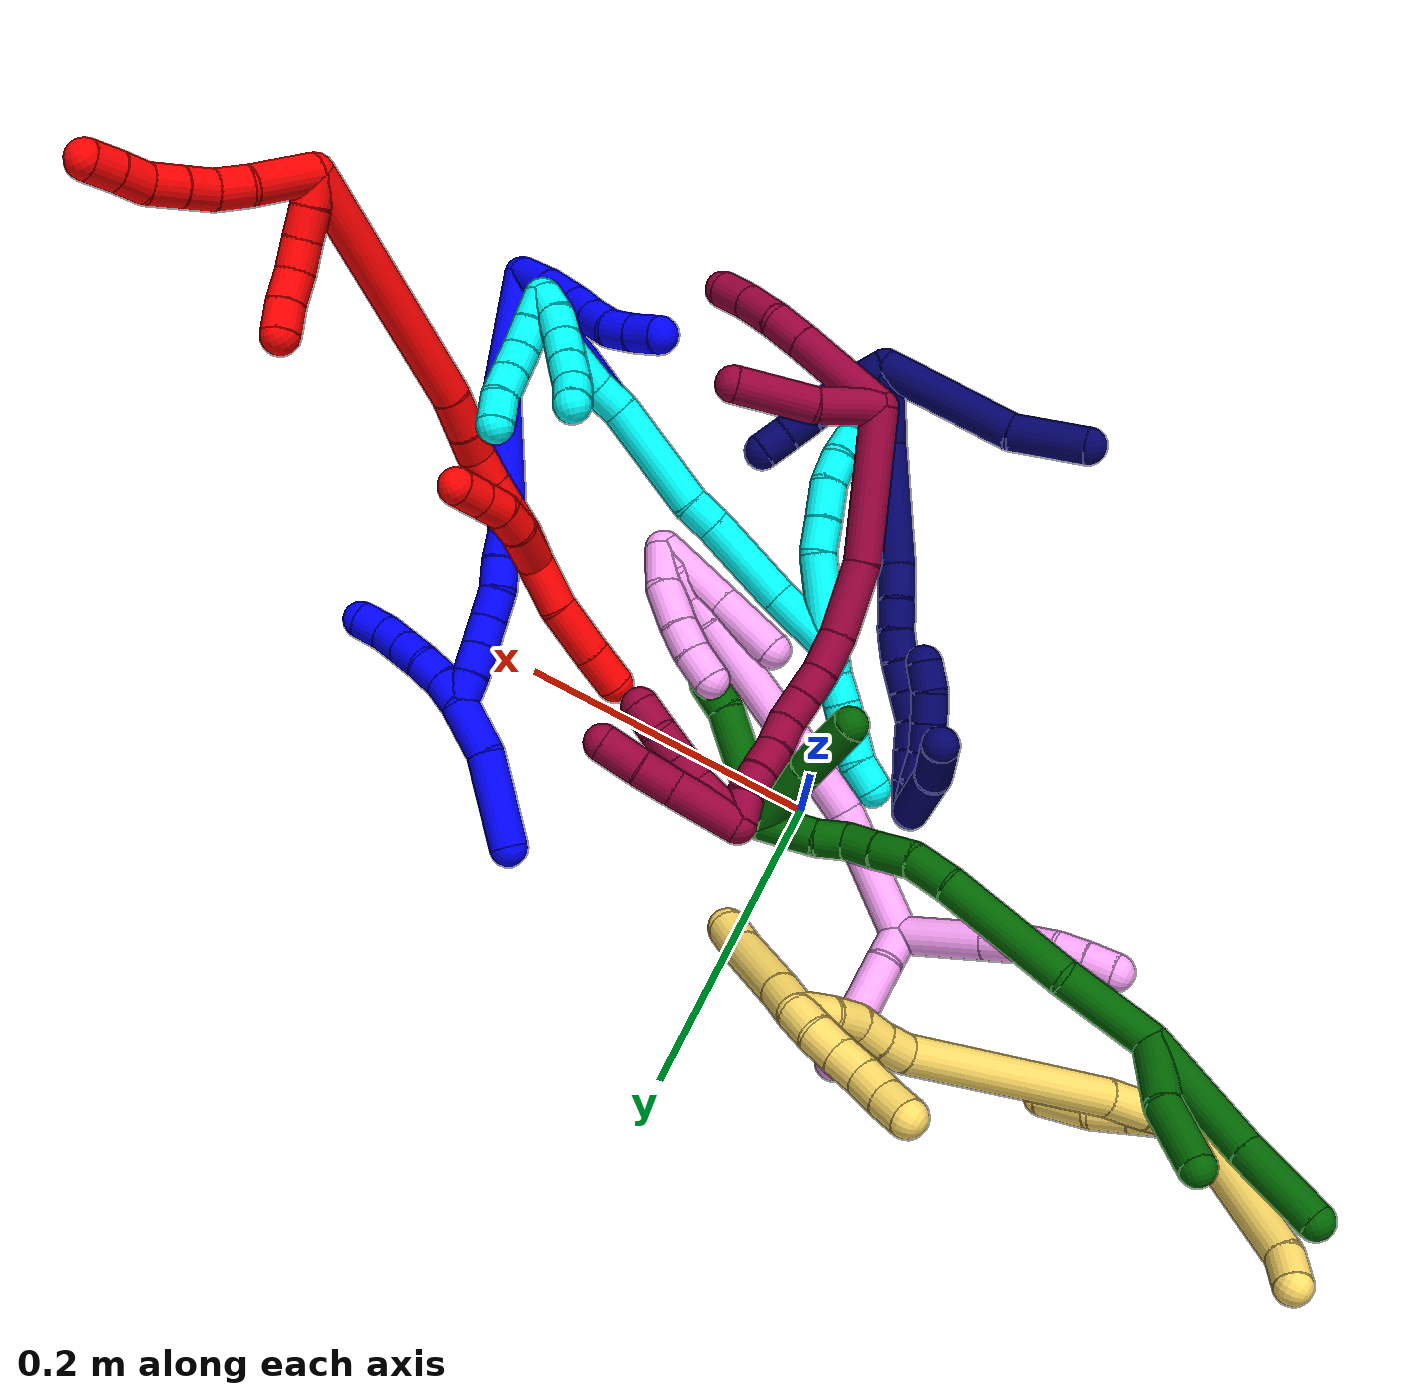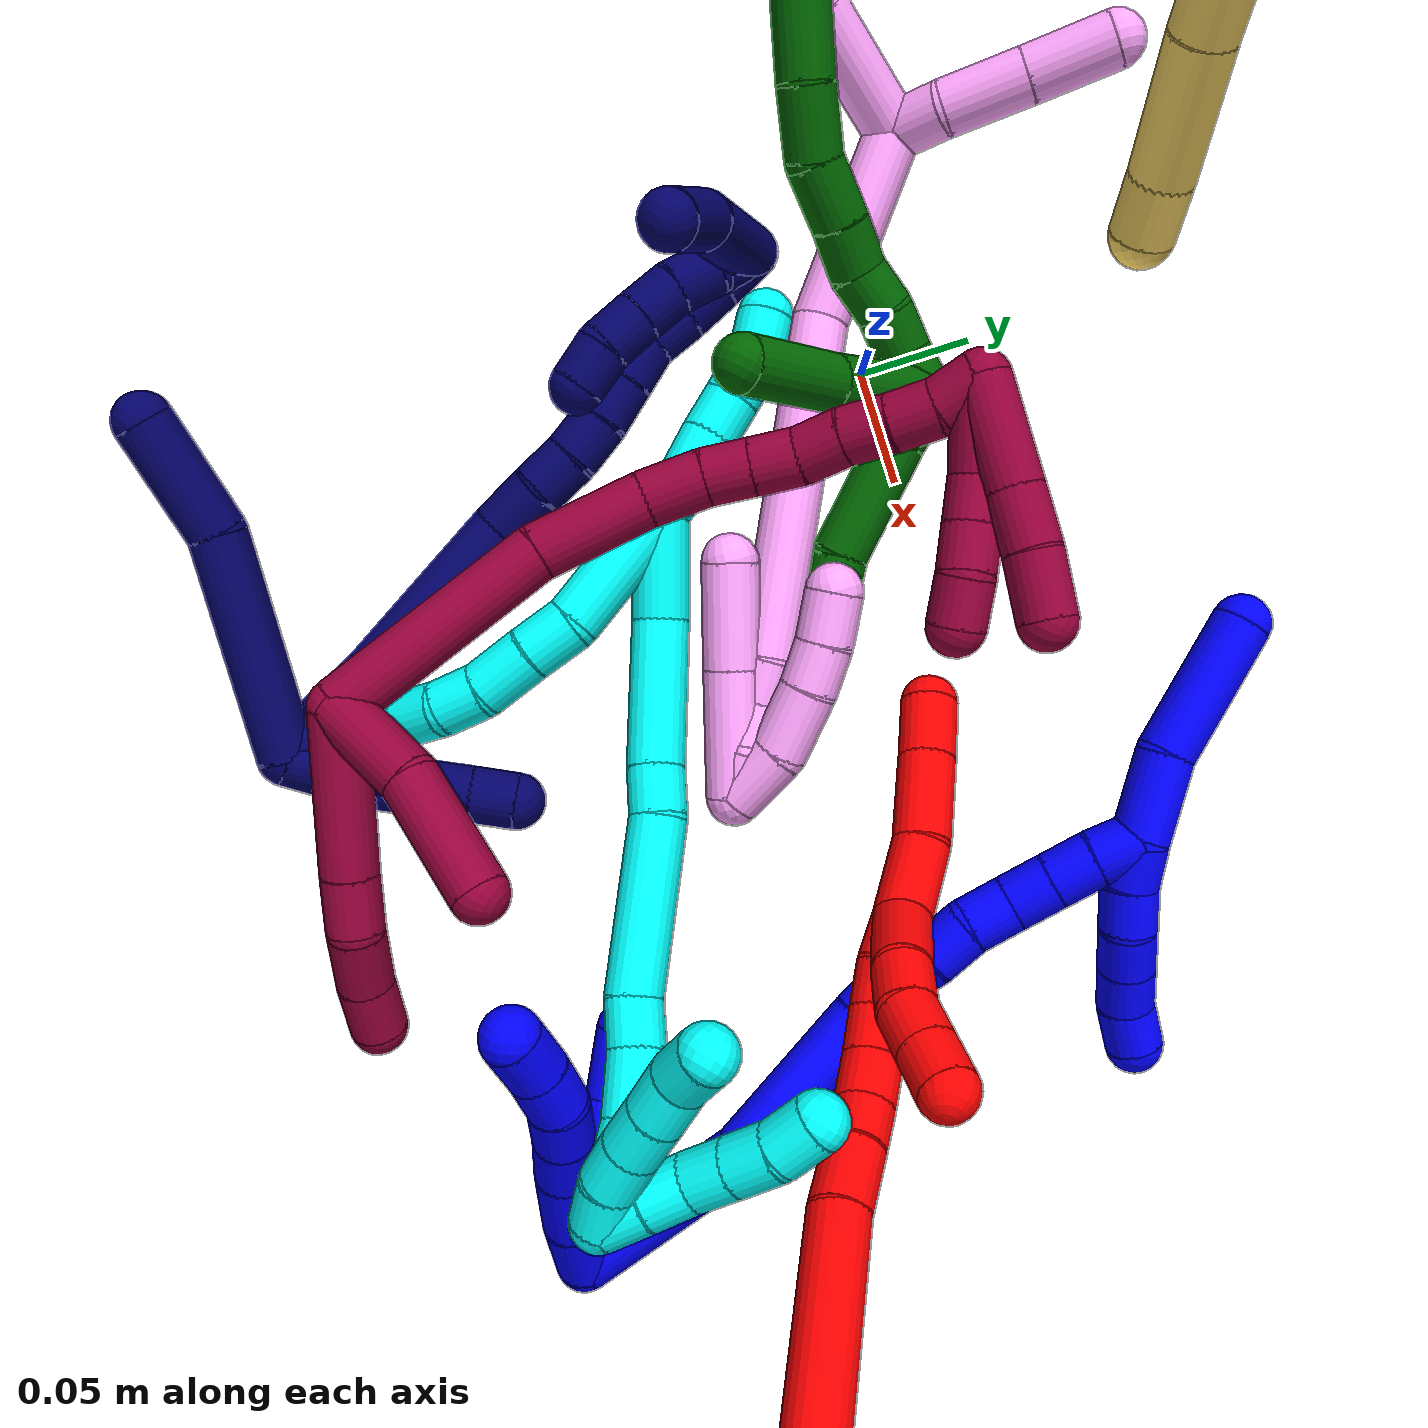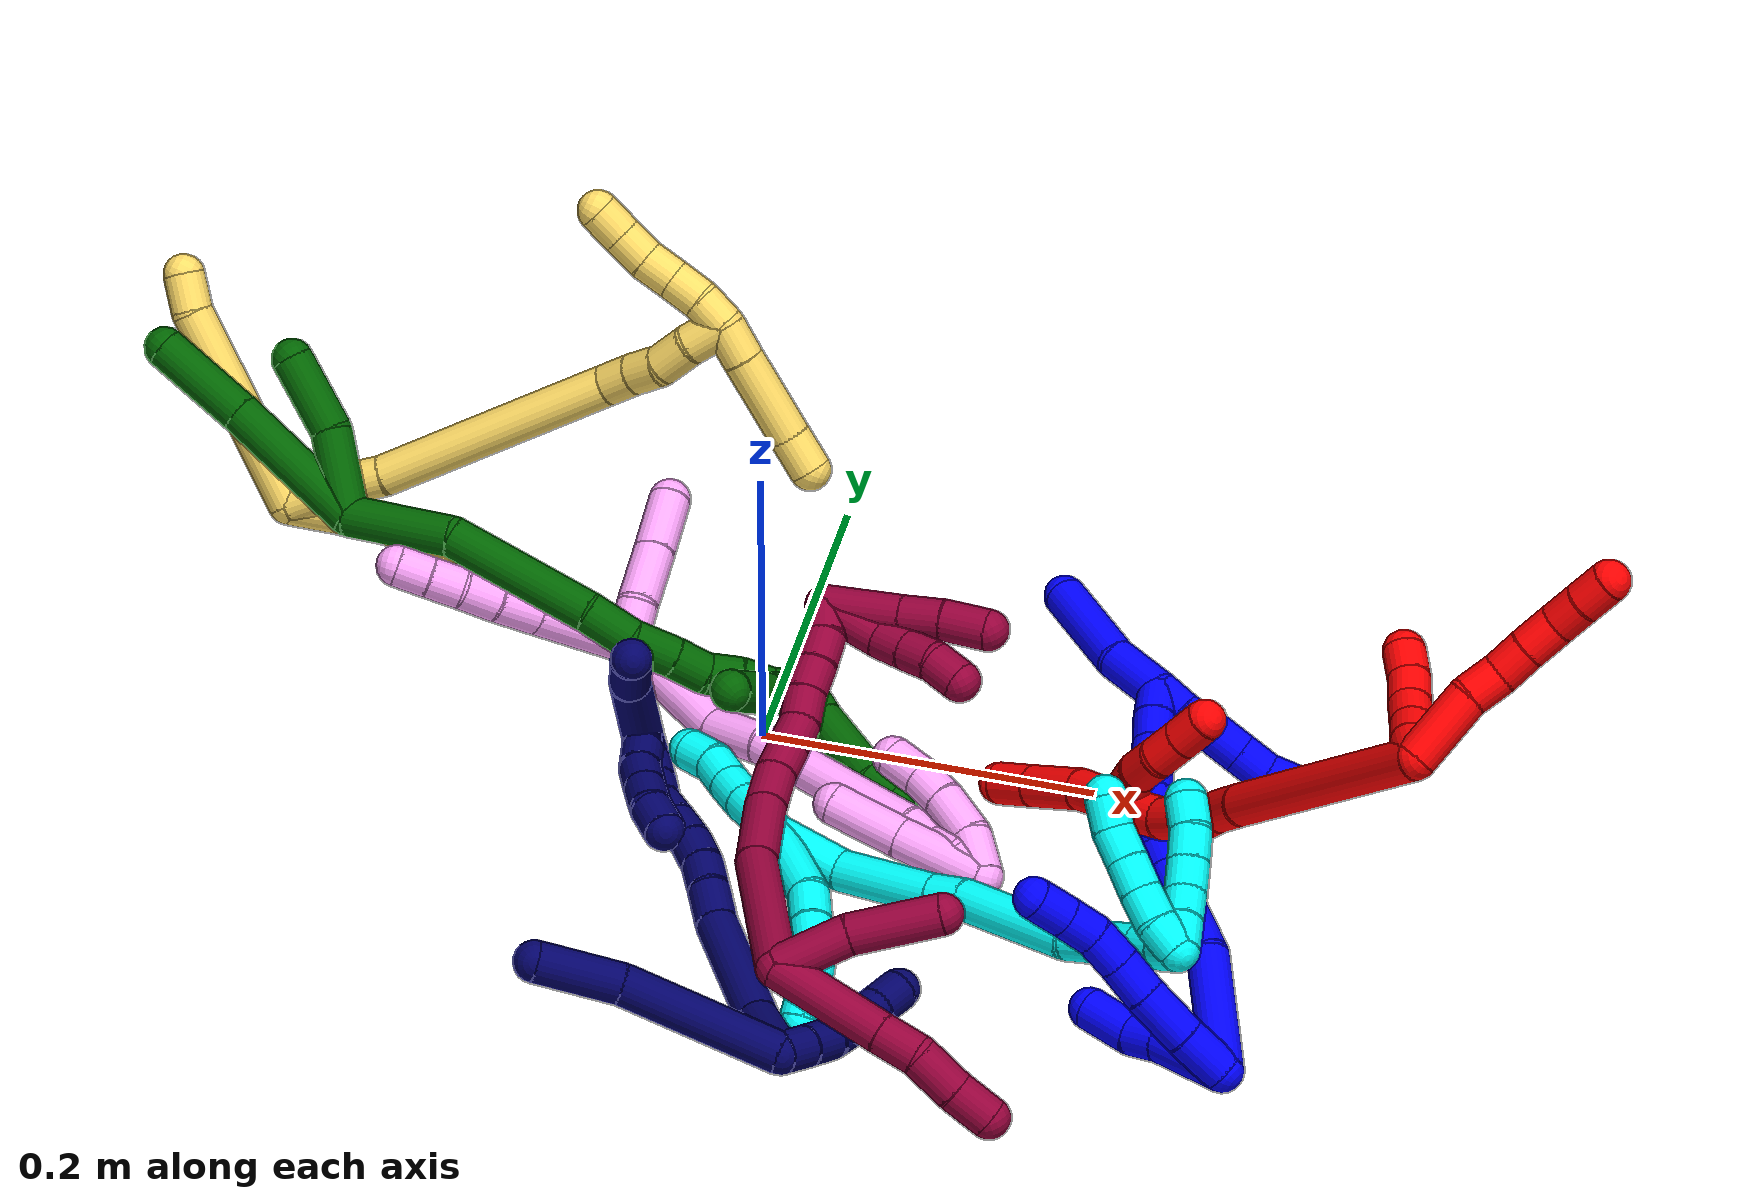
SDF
<sdf version="1.7">
 <world name="default">
  <plugin name="TubeGeneratorPlugin" filename="libtube_generator_plugin.so"/>
  <model name="photoneo_s_sensor">
   <static>1</static>
   <pose>0 0 2 1.57079 1.57079 3.14159</pose>
   <link name="link">
    <inertial><mass>0.1</mass></inertial>
    <sensor name="sensor" type="depth">
     <update_rate>30</update_rate>
     <camera>
      <horizontal_fov>1.22</horizontal_fov>
      <image><width>1920</width><height>1200</height><format>B8G8R8</format></image>
      <clip><near>0.1</near><far>4</far></clip>
      <depth_camera><output>points</output></depth_camera>
     </camera>
     <plugin name="camera_plugin" filename="libgazebo_ros_depth_camera.so">
      <baseline>0.2</baseline>
      <alwaysOn>1</alwaysOn>
      <updateRate>0.0</updateRate>
      <cameraName>camera_ir</cameraName>
      <imageTopicName>/camera/color/image_raw</imageTopicName>
      <cameraInfoTopicName>/camera/color/camera_info</cameraInfoTopicName>
      <depthImageTopicName>/camera/depth/image_raw</depthImageTopicName>
      <depthImageCameraInfoTopicName>/camera/depth/camera_info</depthImageCameraInfoTopicName>
      <pointCloudTopicName>/camera/depth/points</pointCloudTopicName>
      <frameName>fr_optical</frameName>
      <pointCloudCutoff>0.1</pointCloudCutoff>
      <pointCloudCutoffMax>2.0</pointCloudCutoffMax>
      <distortionK1>0</distortionK1>
      <distortionK2>0</distortionK2>
      <distortionK3>0</distortionK3>
      <distortionT1>0</distortionT1>
      <distortionT2>0</distortionT2>
      <CxPrime>0</CxPrime>
      <Cx>0</Cx>
      <Cy>0</Cy>
      <focalLength>0</focalLength>
      <hackBaseline>0</hackBaseline>
     </plugin>
    </sensor>
   </link>
  </model>
  <gravity>0 0 -9.8</gravity>
  <magnetic_field>6e-06 2.3e-05 -4.2e-05</magnetic_field>
  <atmosphere type="adiabatic"/>
  <physics name="default_physics" default="0" type="ode">
   <max_step_size>0.003</max_step_size>
   <real_time_factor>1</real_time_factor>
   <real_time_update_rate>1000</real_time_update_rate>
   <max_contacts>10000</max_contacts>
   <ode>
    <solver>
     <type>quick</type>
     <iters>100</iters>
     <sor>1.3</sor>
     <use_dynamic_moi_rescaling>0</use_dynamic_moi_rescaling>
    </solver>
    <constraints>
     <contact_max_correcting_vel>0</contact_max_correcting_vel>
     <contact_surface_layer>0.001</contact_surface_layer>
     <cfm>0</cfm>
     <erp>0.2</erp>
    </constraints>
   </ode>
  </physics>
  <scene><ambient>0.4 0.4 0.4 1</ambient><background>0.7 0.7 0.7 1</background><shadows>0</shadows></scene>
  <audio><device>default</device></audio>
  <spherical_coordinates>
   <surface_model>EARTH_WGS84</surface_model>
   <latitude_deg>0</latitude_deg>
   <longitude_deg>0</longitude_deg>
   <elevation>0</elevation>
   <heading_deg>0</heading_deg>
  </spherical_coordinates>
  <model name="bin">
   <static>1</static>
   <link name="bottom">
    <collision name="collision-bottom">
     <pose>0 0 -0.01 0 -0 0</pose>
     <geometry><box><size>0.8 0.6 0.02</size></box></geometry>
     <surface>
      <friction><ode><mu>100</mu><mu2>100</mu2></ode></friction>
      <contact><collide_bitmask>65535</collide_bitmask></contact>
     </surface>
    </collision>
   </link>
   <link name="west_wall">
    <collision name="collision-west_wall">
     <pose>-0.41 0 0.1 0 -0 0</pose>
     <geometry><box><size>0.02 0.6 0.2</size></box></geometry>
     <surface>
      <friction><ode><mu>100</mu><mu2>100</mu2></ode></friction>
      <contact><collide_bitmask>65535</collide_bitmask></contact>
     </surface>
    </collision>
   </link>
   <link name="east_wall">
    <collision name="collision-east_wall">
     <pose>0.41 0 0.1 0 -0 0</pose>
     <geometry><box><size>0.02 0.6 0.2</size></box></geometry>
     <surface>
      <friction><ode><mu>100</mu><mu2>100</mu2></ode></friction>
      <contact><collide_bitmask>65535</collide_bitmask></contact>
     </surface>
    </collision>
   </link>
   <link name="south_wall">
    <collision name="collision-south_wall">
     <pose>0 -0.31 0.1 0 -0 0</pose>
     <geometry><box><size>0.8 0.02 0.2</size></box></geometry>
     <surface>
      <friction><ode><mu>100</mu><mu2>100</mu2></ode></friction>
      <contact><collide_bitmask>65535</collide_bitmask></contact>
     </surface>
    </collision>
   </link>
   <link name="north_wall">
    <collision name="collision-north_wall">
     <pose>0 0.31 0.1 0 -0 0</pose>
     <geometry><box><size>0.8 0.02 0.2</size></box></geometry>
     <surface>
      <friction><ode><mu>100</mu><mu2>100</mu2></ode></friction>
      <contact><collide_bitmask>65535</collide_bitmask></contact>
     </surface>
    </collision>
   </link>
  </model>
  <model name="1">
   <static>0</static>
   <link name="1">
    <collision name="collision-cylinder-e_1_2_8">
     <pose>-0.003583 -0.004819 -0.0138 2.8056 -0.240364 -1.23756</pose>
     <geometry><cylinder><radius>0.0125</radius><length>0.0301</length></cylinder></geometry>
     <surface>
      <friction><ode><mu>1.16</mu><mu2>1.16</mu2><slip1>0</slip1><slip2>0</slip2></ode></friction>
      <contact><ode><kp>1e+06</kp><kd>1</kd><max_vel>0</max_vel><min_depth>0.001</min_depth></ode></contact>
     </surface>
    </collision>
    <visual name="visual-cylinder-e_1_2_8">
     <pose>-0.003583 -0.004819 -0.0138 2.8056 -0.240364 -1.23756</pose>
     <geometry><cylinder><radius>0.0125</radius><length>0.0301</length></cylinder></geometry>
     <material><ambient>0 0 1 1</ambient></material>
    </visual>
    <collision name="collision-cylinder-e_2_8_9">
     <pose>-0.011387 -0.013422 -0.043083 2.90197 -0.258942 -1.64907</pose>
     <geometry><cylinder><radius>0.0125</radius><length>0.032975</length></cylinder></geometry>
     <surface>
      <friction><ode><mu>1.16</mu><mu2>1.16</mu2><slip1>0</slip1><slip2>0</slip2></ode></friction>
      <contact><ode><kp>1e+06</kp><kd>1</kd><max_vel>0</max_vel><min_depth>0.001</min_depth></ode></contact>
     </surface>
    </collision>
    <visual name="visual-cylinder-e_2_8_9">
     <pose>-0.011387 -0.013422 -0.043083 2.90197 -0.258942 -1.64907</pose>
     <geometry><cylinder><radius>0.0125</radius><length>0.032975</length></cylinder></geometry>
     <material><ambient>0 0 1 1</ambient></material>
    </visual>
    <collision name="collision-cylinder-e_3_9_10">
     <pose>-0.01925 -0.019206 -0.069372 2.95849 -0.319868 -2.10675</pose>
     <geometry><cylinder><radius>0.0125</radius><length>0.023157</length></cylinder></geometry>
     <surface>
      <friction><ode><mu>1.16</mu><mu2>1.16</mu2><slip1>0</slip1><slip2>0</slip2></ode></friction>
      <contact><ode><kp>1e+06</kp><kd>1</kd><max_vel>0</max_vel><min_depth>0.001</min_depth></ode></contact>
     </surface>
    </collision>
    <visual name="visual-cylinder-e_3_9_10">
     <pose>-0.01925 -0.019206 -0.069372 2.95849 -0.319868 -2.10675</pose>
     <geometry><cylinder><radius>0.0125</radius><length>0.023157</length></cylinder></geometry>
     <material><ambient>0 0 1 1</ambient></material>
    </visual>
    <collision name="collision-cylinder-e_4_10_11">
     <pose>-0.025966 -0.023775 -0.090021 2.88638 -0.293655 -1.71238</pose>
     <geometry><cylinder><radius>0.0125</radius><length>0.021251</length></cylinder></geometry>
     <surface>
      <friction><ode><mu>1.16</mu><mu2>1.16</mu2><slip1>0</slip1><slip2>0</slip2></ode></friction>
      <contact><ode><kp>1e+06</kp><kd>1</kd><max_vel>0</max_vel><min_depth>0.001</min_depth></ode></contact>
     </surface>
    </collision>
    <visual name="visual-cylinder-e_4_10_11">
     <pose>-0.025966 -0.023775 -0.090021 2.88638 -0.293655 -1.71238</pose>
     <geometry><cylinder><radius>0.0125</radius><length>0.021251</length></cylinder></geometry>
     <material><ambient>0 0 1 1</ambient></material>
    </visual>
    <collision name="collision-cylinder-e_5_11_12">
     <pose>-0.0305 -0.031369 -0.108844 2.63133 -0.140719 -0.527826</pose>
     <geometry><cylinder><radius>0.0125</radius><length>0.02079</length></cylinder></geometry>
     <surface>
      <friction><ode><mu>1.16</mu><mu2>1.16</mu2><slip1>0</slip1><slip2>0</slip2></ode></friction>
      <contact><ode><kp>1e+06</kp><kd>1</kd><max_vel>0</max_vel><min_depth>0.001</min_depth></ode></contact>
     </surface>
    </collision>
    <visual name="visual-cylinder-e_5_11_12">
     <pose>-0.0305 -0.031369 -0.108844 2.63133 -0.140719 -0.527826</pose>
     <geometry><cylinder><radius>0.0125</radius><length>0.02079</length></cylinder></geometry>
     <material><ambient>0 0 1 1</ambient></material>
    </visual>
    <collision name="collision-cylinder-e_6_12_6">
     <pose>-0.033733 -0.042397 -0.126704 2.54721 -0.164187 -0.524917</pose>
     <geometry><cylinder><radius>0.0125</radius><length>0.021726</length></cylinder></geometry>
     <surface>
      <friction><ode><mu>1.16</mu><mu2>1.16</mu2><slip1>0</slip1><slip2>0</slip2></ode></friction>
      <contact><ode><kp>1e+06</kp><kd>1</kd><max_vel>0</max_vel><min_depth>0.001</min_depth></ode></contact>
     </surface>
    </collision>
    <visual name="visual-cylinder-e_6_12_6">
     <pose>-0.033733 -0.042397 -0.126704 2.54721 -0.164187 -0.524917</pose>
     <geometry><cylinder><radius>0.0125</radius><length>0.021726</length></cylinder></geometry>
     <material><ambient>0 0 1 1</ambient></material>
    </visual>
    <collision name="collision-cylinder-e_1_2_13">
     <pose>0.009976 0.006897 -0.020728 -2.82036 0.428388 -1.8613</pose>
     <geometry><cylinder><radius>0.0125</radius><length>0.048032</length></cylinder></geometry>
     <surface>
      <friction><ode><mu>1.16</mu><mu2>1.16</mu2><slip1>0</slip1><slip2>0</slip2></ode></friction>
      <contact><ode><kp>1e+06</kp><kd>1</kd><max_vel>0</max_vel><min_depth>0.001</min_depth></ode></contact>
     </surface>
    </collision>
    <visual name="visual-cylinder-e_1_2_13">
     <pose>0.009976 0.006897 -0.020728 -2.82036 0.428388 -1.8613</pose>
     <geometry><cylinder><radius>0.0125</radius><length>0.048032</length></cylinder></geometry>
     <material><ambient>0 0 1 1</ambient></material>
    </visual>
    <collision name="collision-cylinder-e_2_13_14">
     <pose>0.025456 0.015484 -0.050087 -2.94827 0.559146 -2.49016</pose>
     <geometry><cylinder><radius>0.0125</radius><length>0.020749</length></cylinder></geometry>
     <surface>
      <friction><ode><mu>1.16</mu><mu2>1.16</mu2><slip1>0</slip1><slip2>0</slip2></ode></friction>
      <contact><ode><kp>1e+06</kp><kd>1</kd><max_vel>0</max_vel><min_depth>0.001</min_depth></ode></contact>
     </surface>
    </collision>
    <visual name="visual-cylinder-e_2_13_14">
     <pose>0.025456 0.015484 -0.050087 -2.94827 0.559146 -2.49016</pose>
     <geometry><cylinder><radius>0.0125</radius><length>0.020749</length></cylinder></geometry>
     <material><ambient>0 0 1 1</ambient></material>
    </visual>
    <collision name="collision-cylinder-e_3_14_5">
     <pose>0.035246 0.019913 -0.073475 -2.95806 0.278187 -1.97857</pose>
     <geometry><cylinder><radius>0.0125</radius><length>0.031219</length></cylinder></geometry>
     <surface>
      <friction><ode><mu>1.16</mu><mu2>1.16</mu2><slip1>0</slip1><slip2>0</slip2></ode></friction>
      <contact><ode><kp>1e+06</kp><kd>1</kd><max_vel>0</max_vel><min_depth>0.001</min_depth></ode></contact>
     </surface>
    </collision>
    <visual name="visual-cylinder-e_3_14_5">
     <pose>0.035246 0.019913 -0.073475 -2.95806 0.278187 -1.97857</pose>
     <geometry><cylinder><radius>0.0125</radius><length>0.031219</length></cylinder></geometry>
     <material><ambient>0 0 1 1</ambient></material>
    </visual>
    <collision name="collision-cylinder-e_1_2_15">
     <pose>-0.008202 0.029589 -0.028339 -2.33461 -0.197569 0.456215</pose>
     <geometry><cylinder><radius>0.0125</radius><length>0.083567</length></cylinder></geometry>
     <surface>
      <friction><ode><mu>1.16</mu><mu2>1.16</mu2><slip1>0</slip1><slip2>0</slip2></ode></friction>
      <contact><ode><kp>1e+06</kp><kd>1</kd><max_vel>0</max_vel><min_depth>0.001</min_depth></ode></contact>
     </surface>
    </collision>
    <visual name="visual-cylinder-e_1_2_15">
     <pose>-0.008202 0.029589 -0.028339 -2.33461 -0.197569 0.456215</pose>
     <geometry><cylinder><radius>0.0125</radius><length>0.083567</length></cylinder></geometry>
     <material><ambient>0 0 1 1</ambient></material>
    </visual>
    <collision name="collision-cylinder-e_2_15_16">
     <pose>-0.01384 0.084177 -0.085011 -2.41864 0.067739 -0.178753</pose>
     <geometry><cylinder><radius>0.0125</radius><length>0.075744</length></cylinder></geometry>
     <surface>
      <friction><ode><mu>1.16</mu><mu2>1.16</mu2><slip1>0</slip1><slip2>0</slip2></ode></friction>
      <contact><ode><kp>1e+06</kp><kd>1</kd><max_vel>0</max_vel><min_depth>0.001</min_depth></ode></contact>
     </surface>
    </collision>
    <visual name="visual-cylinder-e_2_15_16">
     <pose>-0.01384 0.084177 -0.085011 -2.41864 0.067739 -0.178753</pose>
     <geometry><cylinder><radius>0.0125</radius><length>0.075744</length></cylinder></geometry>
     <material><ambient>0 0 1 1</ambient></material>
    </visual>
    <collision name="collision-cylinder-e_3_16_17">
     <pose>-0.011128 0.116044 -0.120724 -2.39205 0.014653 -0.037247</pose>
     <geometry><cylinder><radius>0.0125</radius><length>0.020165</length></cylinder></geometry>
     <surface>
      <friction><ode><mu>1.16</mu><mu2>1.16</mu2><slip1>0</slip1><slip2>0</slip2></ode></friction>
      <contact><ode><kp>1e+06</kp><kd>1</kd><max_vel>0</max_vel><min_depth>0.001</min_depth></ode></contact>
     </surface>
    </collision>
    <visual name="visual-cylinder-e_3_16_17">
     <pose>-0.011128 0.116044 -0.120724 -2.39205 0.014653 -0.037247</pose>
     <geometry><cylinder><radius>0.0125</radius><length>0.020165</length></cylinder></geometry>
     <material><ambient>0 0 1 1</ambient></material>
    </visual>
    <collision name="collision-cylinder-e_4_17_18">
     <pose>-0.01343 0.129975 -0.134813 -2.33055 -0.246314 0.561423</pose>
     <geometry><cylinder><radius>0.0125</radius><length>0.020089</length></cylinder></geometry>
     <surface>
      <friction><ode><mu>1.16</mu><mu2>1.16</mu2><slip1>0</slip1><slip2>0</slip2></ode></friction>
      <contact><ode><kp>1e+06</kp><kd>1</kd><max_vel>0</max_vel><min_depth>0.001</min_depth></ode></contact>
     </surface>
    </collision>
    <visual name="visual-cylinder-e_4_17_18">
     <pose>-0.01343 0.129975 -0.134813 -2.33055 -0.246314 0.561423</pose>
     <geometry><cylinder><radius>0.0125</radius><length>0.020089</length></cylinder></geometry>
     <material><ambient>0 0 1 1</ambient></material>
    </visual>
    <collision name="collision-cylinder-e_5_18_19">
     <pose>-0.017456 0.143716 -0.149038 -2.41512 -0.155598 0.404575</pose>
     <geometry><cylinder><radius>0.0125</radius><length>0.020354</length></cylinder></geometry>
     <surface>
      <friction><ode><mu>1.16</mu><mu2>1.16</mu2><slip1>0</slip1><slip2>0</slip2></ode></friction>
      <contact><ode><kp>1e+06</kp><kd>1</kd><max_vel>0</max_vel><min_depth>0.001</min_depth></ode></contact>
     </surface>
    </collision>
    <visual name="visual-cylinder-e_5_18_19">
     <pose>-0.017456 0.143716 -0.149038 -2.41512 -0.155598 0.404575</pose>
     <geometry><cylinder><radius>0.0125</radius><length>0.020354</length></cylinder></geometry>
     <material><ambient>0 0 1 1</ambient></material>
    </visual>
    <collision name="collision-cylinder-e_6_19_20">
     <pose>-0.020557 0.158672 -0.161974 -2.15061 -0.152788 0.281377</pose>
     <geometry><cylinder><radius>0.0125</radius><length>0.020021</length></cylinder></geometry>
     <surface>
      <friction><ode><mu>1.16</mu><mu2>1.16</mu2><slip1>0</slip1><slip2>0</slip2></ode></friction>
      <contact><ode><kp>1e+06</kp><kd>1</kd><max_vel>0</max_vel><min_depth>0.001</min_depth></ode></contact>
     </surface>
    </collision>
    <visual name="visual-cylinder-e_6_19_20">
     <pose>-0.020557 0.158672 -0.161974 -2.15061 -0.152788 0.281377</pose>
     <geometry><cylinder><radius>0.0125</radius><length>0.020021</length></cylinder></geometry>
     <material><ambient>0 0 1 1</ambient></material>
    </visual>
    <collision name="collision-cylinder-e_7_20_21">
     <pose>-0.024772 0.174543 -0.173363 -2.23685 -0.271774 0.548511</pose>
     <geometry><cylinder><radius>0.0125</radius><length>0.020054</length></cylinder></geometry>
     <surface>
      <friction><ode><mu>1.16</mu><mu2>1.16</mu2><slip1>0</slip1><slip2>0</slip2></ode></friction>
      <contact><ode><kp>1e+06</kp><kd>1</kd><max_vel>0</max_vel><min_depth>0.001</min_depth></ode></contact>
     </surface>
    </collision>
    <visual name="visual-cylinder-e_7_20_21">
     <pose>-0.024772 0.174543 -0.173363 -2.23685 -0.271774 0.548511</pose>
     <geometry><cylinder><radius>0.0125</radius><length>0.020054</length></cylinder></geometry>
     <material><ambient>0 0 1 1</ambient></material>
    </visual>
    <collision name="collision-cylinder-e_8_21_22">
     <pose>-0.030122 0.189755 -0.185241 -2.23064 -0.269002 0.539069</pose>
     <geometry><cylinder><radius>0.0125</radius><length>0.02</length></cylinder></geometry>
     <surface>
      <friction><ode><mu>1.16</mu><mu2>1.16</mu2><slip1>0</slip1><slip2>0</slip2></ode></friction>
      <contact><ode><kp>1e+06</kp><kd>1</kd><max_vel>0</max_vel><min_depth>0.001</min_depth></ode></contact>
     </surface>
    </collision>
    <visual name="visual-cylinder-e_8_21_22">
     <pose>-0.030122 0.189755 -0.185241 -2.23064 -0.269002 0.539069</pose>
     <geometry><cylinder><radius>0.0125</radius><length>0.02</length></cylinder></geometry>
     <material><ambient>0 0 1 1</ambient></material>
    </visual>
    <collision name="collision-cylinder-e_9_22_1">
     <pose>-0.035837 0.205382 -0.196301 -2.1422 -0.310631 0.558642</pose>
     <geometry><cylinder><radius>0.0125</radius><length>0.020004</length></cylinder></geometry>
     <surface>
      <friction><ode><mu>1.16</mu><mu2>1.16</mu2><slip1>0</slip1><slip2>0</slip2></ode></friction>
      <contact><ode><kp>1e+06</kp><kd>1</kd><max_vel>0</max_vel><min_depth>0.001</min_depth></ode></contact>
     </surface>
    </collision>
    <visual name="visual-cylinder-e_9_22_1">
     <pose>-0.035837 0.205382 -0.196301 -2.1422 -0.310631 0.558642</pose>
     <geometry><cylinder><radius>0.0125</radius><length>0.020004</length></cylinder></geometry>
     <material><ambient>0 0 1 1</ambient></material>
    </visual>
    <collision name="collision-cylinder-e_1_1_23">
     <pose>-0.039031 0.212821 -0.191469 0.057209 -0.013742 -0.000393</pose>
     <geometry><cylinder><radius>0.0125</radius><length>0.02</length></cylinder></geometry>
     <surface>
      <friction><ode><mu>1.16</mu><mu2>1.16</mu2><slip1>0</slip1><slip2>0</slip2></ode></friction>
      <contact><ode><kp>1e+06</kp><kd>1</kd><max_vel>0</max_vel><min_depth>0.001</min_depth></ode></contact>
     </surface>
    </collision>
    <visual name="visual-cylinder-e_1_1_23">
     <pose>-0.039031 0.212821 -0.191469 0.057209 -0.013742 -0.000393</pose>
     <geometry><cylinder><radius>0.0125</radius><length>0.02</length></cylinder></geometry>
     <material><ambient>0 0 1 1</ambient></material>
    </visual>
    <collision name="collision-cylinder-e_2_23_24">
     <pose>-0.040047 0.213252 -0.171575 -0.100837 -0.087941 0.00444</pose>
     <geometry><cylinder><radius>0.0125</radius><length>0.02</length></cylinder></geometry>
     <surface>
      <friction><ode><mu>1.16</mu><mu2>1.16</mu2><slip1>0</slip1><slip2>0</slip2></ode></friction>
      <contact><ode><kp>1e+06</kp><kd>1</kd><max_vel>0</max_vel><min_depth>0.001</min_depth></ode></contact>
     </surface>
    </collision>
    <visual name="visual-cylinder-e_2_23_24">
     <pose>-0.040047 0.213252 -0.171575 -0.100837 -0.087941 0.00444</pose>
     <geometry><cylinder><radius>0.0125</radius><length>0.02</length></cylinder></geometry>
     <material><ambient>0 0 1 1</ambient></material>
    </visual>
    <collision name="collision-cylinder-e_3_24_25">
     <pose>-0.040141 0.216462 -0.151943 -0.223235 0.078488 -0.008802</pose>
     <geometry><cylinder><radius>0.0125</radius><length>0.02</length></cylinder></geometry>
     <surface>
      <friction><ode><mu>1.16</mu><mu2>1.16</mu2><slip1>0</slip1><slip2>0</slip2></ode></friction>
      <contact><ode><kp>1e+06</kp><kd>1</kd><max_vel>0</max_vel><min_depth>0.001</min_depth></ode></contact>
     </surface>
    </collision>
    <visual name="visual-cylinder-e_3_24_25">
     <pose>-0.040141 0.216462 -0.151943 -0.223235 0.078488 -0.008802</pose>
     <geometry><cylinder><radius>0.0125</radius><length>0.02</length></cylinder></geometry>
     <material><ambient>0 0 1 1</ambient></material>
    </visual>
    <collision name="collision-cylinder-e_4_25_26">
     <pose>-0.038575 0.220853 -0.132494 -0.220811 0.078294 -0.008684</pose>
     <geometry><cylinder><radius>0.0125</radius><length>0.02</length></cylinder></geometry>
     <surface>
      <friction><ode><mu>1.16</mu><mu2>1.16</mu2><slip1>0</slip1><slip2>0</slip2></ode></friction>
      <contact><ode><kp>1e+06</kp><kd>1</kd><max_vel>0</max_vel><min_depth>0.001</min_depth></ode></contact>
     </surface>
    </collision>
    <visual name="visual-cylinder-e_4_25_26">
     <pose>-0.038575 0.220853 -0.132494 -0.220811 0.078294 -0.008684</pose>
     <geometry><cylinder><radius>0.0125</radius><length>0.02</length></cylinder></geometry>
     <material><ambient>0 0 1 1</ambient></material>
    </visual>
    <collision name="collision-cylinder-e_5_26_4">
     <pose>-0.039512 0.226094 -0.113402 -0.315666 -0.172776 0.027565</pose>
     <geometry><cylinder><radius>0.0125</radius><length>0.02</length></cylinder></geometry>
     <surface>
      <friction><ode><mu>1.16</mu><mu2>1.16</mu2><slip1>0</slip1><slip2>0</slip2></ode></friction>
      <contact><ode><kp>1e+06</kp><kd>1</kd><max_vel>0</max_vel><min_depth>0.001</min_depth></ode></contact>
     </surface>
    </collision>
    <visual name="visual-cylinder-e_5_26_4">
     <pose>-0.039512 0.226094 -0.113402 -0.315666 -0.172776 0.027565</pose>
     <geometry><cylinder><radius>0.0125</radius><length>0.02</length></cylinder></geometry>
     <material><ambient>0 0 1 1</ambient></material>
    </visual>
    <collision name="collision-cylinder-e_1_1_27">
     <pose>-0.034978 0.218607 -0.218745 -2.84876 0.213467 -1.25659</pose>
     <geometry><cylinder><radius>0.0125</radius><length>0.036964</length></cylinder></geometry>
     <surface>
      <friction><ode><mu>1.16</mu><mu2>1.16</mu2><slip1>0</slip1><slip2>0</slip2></ode></friction>
      <contact><ode><kp>1e+06</kp><kd>1</kd><max_vel>0</max_vel><min_depth>0.001</min_depth></ode></contact>
     </surface>
    </collision>
    <visual name="visual-cylinder-e_1_1_27">
     <pose>-0.034978 0.218607 -0.218745 -2.84876 0.213467 -1.25659</pose>
     <geometry><cylinder><radius>0.0125</radius><length>0.036964</length></cylinder></geometry>
     <material><ambient>0 0 1 1</ambient></material>
    </visual>
    <collision name="collision-cylinder-e_2_27_3">
     <pose>-0.026845 0.23971 -0.26293 -2.60791 0.134217 -0.482168</pose>
     <geometry><cylinder><radius>0.0125</radius><length>0.063036</length></cylinder></geometry>
     <surface>
      <friction><ode><mu>1.16</mu><mu2>1.16</mu2><slip1>0</slip1><slip2>0</slip2></ode></friction>
      <contact><ode><kp>1e+06</kp><kd>1</kd><max_vel>0</max_vel><min_depth>0.001</min_depth></ode></contact>
     </surface>
    </collision>
    <visual name="visual-cylinder-e_2_27_3">
     <pose>-0.026845 0.23971 -0.26293 -2.60791 0.134217 -0.482168</pose>
     <geometry><cylinder><radius>0.0125</radius><length>0.063036</length></cylinder></geometry>
     <material><ambient>0 0 1 1</ambient></material>
    </visual>
    <collision name="collision-sphere-3">
     <pose>-0.022628 0.255599 -0.289821 0 -0 0</pose>
     <geometry><sphere><radius>0.0125</radius></sphere></geometry>
     <surface>
      <friction><ode><mu>1.16</mu><mu2>1.16</mu2><slip1>0</slip1><slip2>0</slip2></ode></friction>
      <contact><ode><kp>1e+06</kp><kd>1</kd><max_vel>0</max_vel><min_depth>0.001</min_depth></ode></contact>
     </surface>
    </collision>
    <visual name="visual-sphere-3">
     <pose>-0.022628 0.255599 -0.289821 0 -0 0</pose>
     <geometry><sphere><radius>0.0125</radius></sphere></geometry>
     <material><ambient>0 0 1 1</ambient></material>
    </visual>
    <collision name="collision-sphere-27">
     <pose>-0.031063 0.223821 -0.236039 0 -0 0</pose>
     <geometry><sphere><radius>0.0125</radius></sphere></geometry>
     <surface>
      <friction><ode><mu>1.16</mu><mu2>1.16</mu2><slip1>0</slip1><slip2>0</slip2></ode></friction>
      <contact><ode><kp>1e+06</kp><kd>1</kd><max_vel>0</max_vel><min_depth>0.001</min_depth></ode></contact>
     </surface>
    </collision>
    <visual name="visual-sphere-27">
     <pose>-0.031063 0.223821 -0.236039 0 -0 0</pose>
     <geometry><sphere><radius>0.0125</radius></sphere></geometry>
     <material><ambient>0 0 1 1</ambient></material>
    </visual>
    <collision name="collision-sphere-4">
     <pose>-0.041231 0.229153 -0.104037 0 -0 0</pose>
     <geometry><sphere><radius>0.0125</radius></sphere></geometry>
     <surface>
      <friction><ode><mu>1.16</mu><mu2>1.16</mu2><slip1>0</slip1><slip2>0</slip2></ode></friction>
      <contact><ode><kp>1e+06</kp><kd>1</kd><max_vel>0</max_vel><min_depth>0.001</min_depth></ode></contact>
     </surface>
    </collision>
    <visual name="visual-sphere-4">
     <pose>-0.041231 0.229153 -0.104037 0 -0 0</pose>
     <geometry><sphere><radius>0.0125</radius></sphere></geometry>
     <material><ambient>0 0 1 1</ambient></material>
    </visual>
    <collision name="collision-sphere-26">
     <pose>-0.037793 0.223036 -0.122766 0 -0 0</pose>
     <geometry><sphere><radius>0.0125</radius></sphere></geometry>
     <surface>
      <friction><ode><mu>1.16</mu><mu2>1.16</mu2><slip1>0</slip1><slip2>0</slip2></ode></friction>
      <contact><ode><kp>1e+06</kp><kd>1</kd><max_vel>0</max_vel><min_depth>0.001</min_depth></ode></contact>
     </surface>
    </collision>
    <visual name="visual-sphere-26">
     <pose>-0.037793 0.223036 -0.122766 0 -0 0</pose>
     <geometry><sphere><radius>0.0125</radius></sphere></geometry>
     <material><ambient>0 0 1 1</ambient></material>
    </visual>
    <collision name="collision-sphere-25">
     <pose>-0.039357 0.218669 -0.142221 0 -0 0</pose>
     <geometry><sphere><radius>0.0125</radius></sphere></geometry>
     <surface>
      <friction><ode><mu>1.16</mu><mu2>1.16</mu2><slip1>0</slip1><slip2>0</slip2></ode></friction>
      <contact><ode><kp>1e+06</kp><kd>1</kd><max_vel>0</max_vel><min_depth>0.001</min_depth></ode></contact>
     </surface>
    </collision>
    <visual name="visual-sphere-25">
     <pose>-0.039357 0.218669 -0.142221 0 -0 0</pose>
     <geometry><sphere><radius>0.0125</radius></sphere></geometry>
     <material><ambient>0 0 1 1</ambient></material>
    </visual>
    <collision name="collision-sphere-24">
     <pose>-0.040925 0.214255 -0.161665 0 -0 0</pose>
     <geometry><sphere><radius>0.0125</radius></sphere></geometry>
     <surface>
      <friction><ode><mu>1.16</mu><mu2>1.16</mu2><slip1>0</slip1><slip2>0</slip2></ode></friction>
      <contact><ode><kp>1e+06</kp><kd>1</kd><max_vel>0</max_vel><min_depth>0.001</min_depth></ode></contact>
     </surface>
    </collision>
    <visual name="visual-sphere-24">
     <pose>-0.040925 0.214255 -0.161665 0 -0 0</pose>
     <geometry><sphere><radius>0.0125</radius></sphere></geometry>
     <material><ambient>0 0 1 1</ambient></material>
    </visual>
    <collision name="collision-sphere-23">
     <pose>-0.039169 0.212249 -0.181486 0 -0 0</pose>
     <geometry><sphere><radius>0.0125</radius></sphere></geometry>
     <surface>
      <friction><ode><mu>1.16</mu><mu2>1.16</mu2><slip1>0</slip1><slip2>0</slip2></ode></friction>
      <contact><ode><kp>1e+06</kp><kd>1</kd><max_vel>0</max_vel><min_depth>0.001</min_depth></ode></contact>
     </surface>
    </collision>
    <visual name="visual-sphere-23">
     <pose>-0.039169 0.212249 -0.181486 0 -0 0</pose>
     <geometry><sphere><radius>0.0125</radius></sphere></geometry>
     <material><ambient>0 0 1 1</ambient></material>
    </visual>
    <collision name="collision-sphere-1">
     <pose>-0.038894 0.213393 -0.201451 0 -0 0</pose>
     <geometry><sphere><radius>0.0125</radius></sphere></geometry>
     <surface>
      <friction><ode><mu>1.16</mu><mu2>1.16</mu2><slip1>0</slip1><slip2>0</slip2></ode></friction>
      <contact><ode><kp>1e+06</kp><kd>1</kd><max_vel>0</max_vel><min_depth>0.001</min_depth></ode></contact>
     </surface>
    </collision>
    <visual name="visual-sphere-1">
     <pose>-0.038894 0.213393 -0.201451 0 -0 0</pose>
     <geometry><sphere><radius>0.0125</radius></sphere></geometry>
     <material><ambient>0 0 1 1</ambient></material>
    </visual>
    <collision name="collision-sphere-22">
     <pose>-0.032779 0.197372 -0.191151 0 -0 0</pose>
     <geometry><sphere><radius>0.0125</radius></sphere></geometry>
     <surface>
      <friction><ode><mu>1.16</mu><mu2>1.16</mu2><slip1>0</slip1><slip2>0</slip2></ode></friction>
      <contact><ode><kp>1e+06</kp><kd>1</kd><max_vel>0</max_vel><min_depth>0.001</min_depth></ode></contact>
     </surface>
    </collision>
    <visual name="visual-sphere-22">
     <pose>-0.032779 0.197372 -0.191151 0 -0 0</pose>
     <geometry><sphere><radius>0.0125</radius></sphere></geometry>
     <material><ambient>0 0 1 1</ambient></material>
    </visual>
    <collision name="collision-sphere-21">
     <pose>-0.027464 0.182138 -0.179331 0 -0 0</pose>
     <geometry><sphere><radius>0.0125</radius></sphere></geometry>
     <surface>
      <friction><ode><mu>1.16</mu><mu2>1.16</mu2><slip1>0</slip1><slip2>0</slip2></ode></friction>
      <contact><ode><kp>1e+06</kp><kd>1</kd><max_vel>0</max_vel><min_depth>0.001</min_depth></ode></contact>
     </surface>
    </collision>
    <visual name="visual-sphere-21">
     <pose>-0.027464 0.182138 -0.179331 0 -0 0</pose>
     <geometry><sphere><radius>0.0125</radius></sphere></geometry>
     <material><ambient>0 0 1 1</ambient></material>
    </visual>
    <collision name="collision-sphere-12">
     <pose>-0.031958 -0.036396 -0.117825 0 -0 0</pose>
     <geometry><sphere><radius>0.0125</radius></sphere></geometry>
     <surface>
      <friction><ode><mu>1.16</mu><mu2>1.16</mu2><slip1>0</slip1><slip2>0</slip2></ode></friction>
      <contact><ode><kp>1e+06</kp><kd>1</kd><max_vel>0</max_vel><min_depth>0.001</min_depth></ode></contact>
     </surface>
    </collision>
    <visual name="visual-sphere-12">
     <pose>-0.031958 -0.036396 -0.117825 0 -0 0</pose>
     <geometry><sphere><radius>0.0125</radius></sphere></geometry>
     <material><ambient>0 0 1 1</ambient></material>
    </visual>
    <collision name="collision-sphere-11">
     <pose>-0.029042 -0.026342 -0.099863 0 -0 0</pose>
     <geometry><sphere><radius>0.0125</radius></sphere></geometry>
     <surface>
      <friction><ode><mu>1.16</mu><mu2>1.16</mu2><slip1>0</slip1><slip2>0</slip2></ode></friction>
      <contact><ode><kp>1e+06</kp><kd>1</kd><max_vel>0</max_vel><min_depth>0.001</min_depth></ode></contact>
     </surface>
    </collision>
    <visual name="visual-sphere-11">
     <pose>-0.029042 -0.026342 -0.099863 0 -0 0</pose>
     <geometry><sphere><radius>0.0125</radius></sphere></geometry>
     <material><ambient>0 0 1 1</ambient></material>
    </visual>
    <collision name="collision-sphere-10">
     <pose>-0.022891 -0.021207 -0.08018 0 -0 0</pose>
     <geometry><sphere><radius>0.0125</radius></sphere></geometry>
     <surface>
      <friction><ode><mu>1.16</mu><mu2>1.16</mu2><slip1>0</slip1><slip2>0</slip2></ode></friction>
      <contact><ode><kp>1e+06</kp><kd>1</kd><max_vel>0</max_vel><min_depth>0.001</min_depth></ode></contact>
     </surface>
    </collision>
    <visual name="visual-sphere-10">
     <pose>-0.022891 -0.021207 -0.08018 0 -0 0</pose>
     <geometry><sphere><radius>0.0125</radius></sphere></geometry>
     <material><ambient>0 0 1 1</ambient></material>
    </visual>
    <collision name="collision-sphere-9">
     <pose>-0.015609 -0.017204 -0.058565 0 -0 0</pose>
     <geometry><sphere><radius>0.0125</radius></sphere></geometry>
     <surface>
      <friction><ode><mu>1.16</mu><mu2>1.16</mu2><slip1>0</slip1><slip2>0</slip2></ode></friction>
      <contact><ode><kp>1e+06</kp><kd>1</kd><max_vel>0</max_vel><min_depth>0.001</min_depth></ode></contact>
     </surface>
    </collision>
    <visual name="visual-sphere-9">
     <pose>-0.015609 -0.017204 -0.058565 0 -0 0</pose>
     <geometry><sphere><radius>0.0125</radius></sphere></geometry>
     <material><ambient>0 0 1 1</ambient></material>
    </visual>
    <collision name="collision-sphere-2">
     <geometry><sphere><radius>0.0125</radius></sphere></geometry>
     <surface>
      <friction><ode><mu>1.16</mu><mu2>1.16</mu2><slip1>0</slip1><slip2>0</slip2></ode></friction>
      <contact><ode><kp>1e+06</kp><kd>1</kd><max_vel>0</max_vel><min_depth>0.001</min_depth></ode></contact>
     </surface>
    </collision>
    <visual name="visual-sphere-2">
     <geometry><sphere><radius>0.0125</radius></sphere></geometry>
     <material><ambient>0 0 1 1</ambient></material>
    </visual>
    <collision name="collision-sphere-19">
     <pose>-0.019033 0.150395 -0.156554 0 -0 0</pose>
     <geometry><sphere><radius>0.0125</radius></sphere></geometry>
     <surface>
      <friction><ode><mu>1.16</mu><mu2>1.16</mu2><slip1>0</slip1><slip2>0</slip2></ode></friction>
      <contact><ode><kp>1e+06</kp><kd>1</kd><max_vel>0</max_vel><min_depth>0.001</min_depth></ode></contact>
     </surface>
    </collision>
    <visual name="visual-sphere-19">
     <pose>-0.019033 0.150395 -0.156554 0 -0 0</pose>
     <geometry><sphere><radius>0.0125</radius></sphere></geometry>
     <material><ambient>0 0 1 1</ambient></material>
    </visual>
    <collision name="collision-sphere-8">
     <pose>-0.007166 -0.009639 -0.0276 0 -0 0</pose>
     <geometry><sphere><radius>0.0125</radius></sphere></geometry>
     <surface>
      <friction><ode><mu>1.16</mu><mu2>1.16</mu2><slip1>0</slip1><slip2>0</slip2></ode></friction>
      <contact><ode><kp>1e+06</kp><kd>1</kd><max_vel>0</max_vel><min_depth>0.001</min_depth></ode></contact>
     </surface>
    </collision>
    <visual name="visual-sphere-8">
     <pose>-0.007166 -0.009639 -0.0276 0 -0 0</pose>
     <geometry><sphere><radius>0.0125</radius></sphere></geometry>
     <material><ambient>0 0 1 1</ambient></material>
    </visual>
    <collision name="collision-sphere-6">
     <pose>-0.035509 -0.048399 -0.135583 0 -0 0</pose>
     <geometry><sphere><radius>0.0125</radius></sphere></geometry>
     <surface>
      <friction><ode><mu>1.16</mu><mu2>1.16</mu2><slip1>0</slip1><slip2>0</slip2></ode></friction>
      <contact><ode><kp>1e+06</kp><kd>1</kd><max_vel>0</max_vel><min_depth>0.001</min_depth></ode></contact>
     </surface>
    </collision>
    <visual name="visual-sphere-6">
     <pose>-0.035509 -0.048399 -0.135583 0 -0 0</pose>
     <geometry><sphere><radius>0.0125</radius></sphere></geometry>
     <material><ambient>0 0 1 1</ambient></material>
    </visual>
    <collision name="collision-sphere-13">
     <pose>0.019953 0.013795 -0.041457 0 -0 0</pose>
     <geometry><sphere><radius>0.0125</radius></sphere></geometry>
     <surface>
      <friction><ode><mu>1.16</mu><mu2>1.16</mu2><slip1>0</slip1><slip2>0</slip2></ode></friction>
      <contact><ode><kp>1e+06</kp><kd>1</kd><max_vel>0</max_vel><min_depth>0.001</min_depth></ode></contact>
     </surface>
    </collision>
    <visual name="visual-sphere-13">
     <pose>0.019953 0.013795 -0.041457 0 -0 0</pose>
     <geometry><sphere><radius>0.0125</radius></sphere></geometry>
     <material><ambient>0 0 1 1</ambient></material>
    </visual>
    <collision name="collision-sphere-14">
     <pose>0.030959 0.017174 -0.058718 0 -0 0</pose>
     <geometry><sphere><radius>0.0125</radius></sphere></geometry>
     <surface>
      <friction><ode><mu>1.16</mu><mu2>1.16</mu2><slip1>0</slip1><slip2>0</slip2></ode></friction>
      <contact><ode><kp>1e+06</kp><kd>1</kd><max_vel>0</max_vel><min_depth>0.001</min_depth></ode></contact>
     </surface>
    </collision>
    <visual name="visual-sphere-14">
     <pose>0.030959 0.017174 -0.058718 0 -0 0</pose>
     <geometry><sphere><radius>0.0125</radius></sphere></geometry>
     <material><ambient>0 0 1 1</ambient></material>
    </visual>
    <collision name="collision-sphere-5">
     <pose>0.039532 0.022653 -0.088233 0 -0 0</pose>
     <geometry><sphere><radius>0.0125</radius></sphere></geometry>
     <surface>
      <friction><ode><mu>1.16</mu><mu2>1.16</mu2><slip1>0</slip1><slip2>0</slip2></ode></friction>
      <contact><ode><kp>1e+06</kp><kd>1</kd><max_vel>0</max_vel><min_depth>0.001</min_depth></ode></contact>
     </surface>
    </collision>
    <visual name="visual-sphere-5">
     <pose>0.039532 0.022653 -0.088233 0 -0 0</pose>
     <geometry><sphere><radius>0.0125</radius></sphere></geometry>
     <material><ambient>0 0 1 1</ambient></material>
    </visual>
    <collision name="collision-sphere-15">
     <pose>-0.016403 0.059178 -0.056677 0 -0 0</pose>
     <geometry><sphere><radius>0.0125</radius></sphere></geometry>
     <surface>
      <friction><ode><mu>1.16</mu><mu2>1.16</mu2><slip1>0</slip1><slip2>0</slip2></ode></friction>
      <contact><ode><kp>1e+06</kp><kd>1</kd><max_vel>0</max_vel><min_depth>0.001</min_depth></ode></contact>
     </surface>
    </collision>
    <visual name="visual-sphere-15">
     <pose>-0.016403 0.059178 -0.056677 0 -0 0</pose>
     <geometry><sphere><radius>0.0125</radius></sphere></geometry>
     <material><ambient>0 0 1 1</ambient></material>
    </visual>
    <collision name="collision-sphere-16">
     <pose>-0.011276 0.109175 -0.113344 0 -0 0</pose>
     <geometry><sphere><radius>0.0125</radius></sphere></geometry>
     <surface>
      <friction><ode><mu>1.16</mu><mu2>1.16</mu2><slip1>0</slip1><slip2>0</slip2></ode></friction>
      <contact><ode><kp>1e+06</kp><kd>1</kd><max_vel>0</max_vel><min_depth>0.001</min_depth></ode></contact>
     </surface>
    </collision>
    <visual name="visual-sphere-16">
     <pose>-0.011276 0.109175 -0.113344 0 -0 0</pose>
     <geometry><sphere><radius>0.0125</radius></sphere></geometry>
     <material><ambient>0 0 1 1</ambient></material>
    </visual>
    <collision name="collision-sphere-17">
     <pose>-0.010981 0.122913 -0.128104 0 -0 0</pose>
     <geometry><sphere><radius>0.0125</radius></sphere></geometry>
     <surface>
      <friction><ode><mu>1.16</mu><mu2>1.16</mu2><slip1>0</slip1><slip2>0</slip2></ode></friction>
      <contact><ode><kp>1e+06</kp><kd>1</kd><max_vel>0</max_vel><min_depth>0.001</min_depth></ode></contact>
     </surface>
    </collision>
    <visual name="visual-sphere-17">
     <pose>-0.010981 0.122913 -0.128104 0 -0 0</pose>
     <geometry><sphere><radius>0.0125</radius></sphere></geometry>
     <material><ambient>0 0 1 1</ambient></material>
    </visual>
    <collision name="collision-sphere-18">
     <pose>-0.015879 0.137038 -0.141522 0 -0 0</pose>
     <geometry><sphere><radius>0.0125</radius></sphere></geometry>
     <surface>
      <friction><ode><mu>1.16</mu><mu2>1.16</mu2><slip1>0</slip1><slip2>0</slip2></ode></friction>
      <contact><ode><kp>1e+06</kp><kd>1</kd><max_vel>0</max_vel><min_depth>0.001</min_depth></ode></contact>
     </surface>
    </collision>
    <visual name="visual-sphere-18">
     <pose>-0.015879 0.137038 -0.141522 0 -0 0</pose>
     <geometry><sphere><radius>0.0125</radius></sphere></geometry>
     <material><ambient>0 0 1 1</ambient></material>
    </visual>
    <collision name="collision-sphere-20">
     <pose>-0.02208 0.166949 -0.167395 0 -0 0</pose>
     <geometry><sphere><radius>0.0125</radius></sphere></geometry>
     <surface>
      <friction><ode><mu>1.16</mu><mu2>1.16</mu2><slip1>0</slip1><slip2>0</slip2></ode></friction>
      <contact><ode><kp>1e+06</kp><kd>1</kd><max_vel>0</max_vel><min_depth>0.001</min_depth></ode></contact>
     </surface>
    </collision>
    <visual name="visual-sphere-20">
     <pose>-0.02208 0.166949 -0.167395 0 -0 0</pose>
     <geometry><sphere><radius>0.0125</radius></sphere></geometry>
     <material><ambient>0 0 1 1</ambient></material>
    </visual>
    <inertial>
     <pose>-0.016643 0.099266 -0.11455 0 -0 0</pose>
     <mass>0.75</mass>
     <inertia>
      <ixx>9.5e-05</ixx>
      <ixy>0</ixy>
      <ixz>0</ixz>
      <iyy>-7.1e-05</iyy>
      <iyz>0</iyz>
      <izz>-0.000114</izz>
     </inertia>
    </inertial>
   </link>
   <pose>0.330352 -0.230556 0.025725 -2.29586 1.05929 -2.64199</pose>
  </model>
  <model name="2">
   <static>0</static>
   <link name="2">
    <collision name="collision-cylinder-e_1_2_8">
     <pose>-0.019497 0.004752 0.0102 -0.435967 -1.04737 0.254439</pose>
     <geometry><cylinder><radius>0.0125</radius><length>0.045023</length></cylinder></geometry>
     <surface>
      <friction><ode><mu>1.16</mu><mu2>1.16</mu2><slip1>0</slip1><slip2>0</slip2></ode></friction>
      <contact><ode><kp>1e+06</kp><kd>1</kd><max_vel>0</max_vel><min_depth>0.001</min_depth></ode></contact>
     </surface>
    </collision>
    <visual name="visual-cylinder-e_1_2_8">
     <pose>-0.019497 0.004752 0.0102 -0.435967 -1.04737 0.254439</pose>
     <geometry><cylinder><radius>0.0125</radius><length>0.045023</length></cylinder></geometry>
     <material><ambient>1 0 0 1</ambient></material>
    </visual>
    <collision name="collision-cylinder-e_2_8_9">
     <pose>-0.047315 0.014202 0.025452 -0.749161 -0.87847 0.365315</pose>
     <geometry><cylinder><radius>0.0125</radius><length>0.021617</length></cylinder></geometry>
     <surface>
      <friction><ode><mu>1.16</mu><mu2>1.16</mu2><slip1>0</slip1><slip2>0</slip2></ode></friction>
      <contact><ode><kp>1e+06</kp><kd>1</kd><max_vel>0</max_vel><min_depth>0.001</min_depth></ode></contact>
     </surface>
    </collision>
    <visual name="visual-cylinder-e_2_8_9">
     <pose>-0.047315 0.014202 0.025452 -0.749161 -0.87847 0.365315</pose>
     <geometry><cylinder><radius>0.0125</radius><length>0.021617</length></cylinder></geometry>
     <material><ambient>1 0 0 1</ambient></material>
    </visual>
    <collision name="collision-cylinder-e_3_9_10">
     <pose>-0.063128 0.021079 0.037345 -0.308197 -0.806735 0.132386</pose>
     <geometry><cylinder><radius>0.0125</radius><length>0.020754</length></cylinder></geometry>
     <surface>
      <friction><ode><mu>1.16</mu><mu2>1.16</mu2><slip1>0</slip1><slip2>0</slip2></ode></friction>
      <contact><ode><kp>1e+06</kp><kd>1</kd><max_vel>0</max_vel><min_depth>0.001</min_depth></ode></contact>
     </surface>
    </collision>
    <visual name="visual-cylinder-e_3_9_10">
     <pose>-0.063128 0.021079 0.037345 -0.308197 -0.806735 0.132386</pose>
     <geometry><cylinder><radius>0.0125</radius><length>0.020754</length></cylinder></geometry>
     <material><ambient>1 0 0 1</ambient></material>
    </visual>
    <collision name="collision-cylinder-e_4_10_11">
     <pose>-0.078618 0.026083 0.051556 -0.366194 -0.792013 0.154529</pose>
     <geometry><cylinder><radius>0.0125</radius><length>0.022474</length></cylinder></geometry>
     <surface>
      <friction><ode><mu>1.16</mu><mu2>1.16</mu2><slip1>0</slip1><slip2>0</slip2></ode></friction>
      <contact><ode><kp>1e+06</kp><kd>1</kd><max_vel>0</max_vel><min_depth>0.001</min_depth></ode></contact>
     </surface>
    </collision>
    <visual name="visual-cylinder-e_4_10_11">
     <pose>-0.078618 0.026083 0.051556 -0.366194 -0.792013 0.154529</pose>
     <geometry><cylinder><radius>0.0125</radius><length>0.022474</length></cylinder></geometry>
     <material><ambient>1 0 0 1</ambient></material>
    </visual>
    <collision name="collision-cylinder-e_5_11_12">
     <pose>-0.092059 0.029851 0.067312 -0.111808 -0.572841 0.032961</pose>
     <geometry><cylinder><radius>0.0125</radius><length>0.020083</length></cylinder></geometry>
     <surface>
      <friction><ode><mu>1.16</mu><mu2>1.16</mu2><slip1>0</slip1><slip2>0</slip2></ode></friction>
      <contact><ode><kp>1e+06</kp><kd>1</kd><max_vel>0</max_vel><min_depth>0.001</min_depth></ode></contact>
     </surface>
    </collision>
    <visual name="visual-cylinder-e_5_11_12">
     <pose>-0.092059 0.029851 0.067312 -0.111808 -0.572841 0.032961</pose>
     <geometry><cylinder><radius>0.0125</radius><length>0.020083</length></cylinder></geometry>
     <material><ambient>1 0 0 1</ambient></material>
    </visual>
    <collision name="collision-cylinder-e_6_12_6">
     <pose>-0.103217 0.032058 0.083835 -0.15429 -0.606695 0.048381</pose>
     <geometry><cylinder><radius>0.0125</radius><length>0.020048</length></cylinder></geometry>
     <surface>
      <friction><ode><mu>1.16</mu><mu2>1.16</mu2><slip1>0</slip1><slip2>0</slip2></ode></friction>
      <contact><ode><kp>1e+06</kp><kd>1</kd><max_vel>0</max_vel><min_depth>0.001</min_depth></ode></contact>
     </surface>
    </collision>
    <visual name="visual-cylinder-e_6_12_6">
     <pose>-0.103217 0.032058 0.083835 -0.15429 -0.606695 0.048381</pose>
     <geometry><cylinder><radius>0.0125</radius><length>0.020048</length></cylinder></geometry>
     <material><ambient>1 0 0 1</ambient></material>
    </visual>
    <collision name="collision-cylinder-e_1_2_13">
     <pose>-0.006938 0.001442 -0.007056 -2.93996 -0.766731 2.6501</pose>
     <geometry><cylinder><radius>0.0125</radius><length>0.02</length></cylinder></geometry>
     <surface>
      <friction><ode><mu>1.16</mu><mu2>1.16</mu2><slip1>0</slip1><slip2>0</slip2></ode></friction>
      <contact><ode><kp>1e+06</kp><kd>1</kd><max_vel>0</max_vel><min_depth>0.001</min_depth></ode></contact>
     </surface>
    </collision>
    <visual name="visual-cylinder-e_1_2_13">
     <pose>-0.006938 0.001442 -0.007056 -2.93996 -0.766731 2.6501</pose>
     <geometry><cylinder><radius>0.0125</radius><length>0.02</length></cylinder></geometry>
     <material><ambient>1 0 0 1</ambient></material>
    </visual>
    <collision name="collision-cylinder-e_2_13_14">
     <pose>-0.021174 0.005262 -0.020522 -2.78648 -0.818018 2.35657</pose>
     <geometry><cylinder><radius>0.0125</radius><length>0.02</length></cylinder></geometry>
     <surface>
      <friction><ode><mu>1.16</mu><mu2>1.16</mu2><slip1>0</slip1><slip2>0</slip2></ode></friction>
      <contact><ode><kp>1e+06</kp><kd>1</kd><max_vel>0</max_vel><min_depth>0.001</min_depth></ode></contact>
     </surface>
    </collision>
    <visual name="visual-cylinder-e_2_13_14">
     <pose>-0.021174 0.005262 -0.020522 -2.78648 -0.818018 2.35657</pose>
     <geometry><cylinder><radius>0.0125</radius><length>0.02</length></cylinder></geometry>
     <material><ambient>1 0 0 1</ambient></material>
    </visual>
    <collision name="collision-cylinder-e_3_14_15">
     <pose>-0.036289 0.008981 -0.033023 -2.92469 -0.897384 2.69677</pose>
     <geometry><cylinder><radius>0.0125</radius><length>0.02</length></cylinder></geometry>
     <surface>
      <friction><ode><mu>1.16</mu><mu2>1.16</mu2><slip1>0</slip1><slip2>0</slip2></ode></friction>
      <contact><ode><kp>1e+06</kp><kd>1</kd><max_vel>0</max_vel><min_depth>0.001</min_depth></ode></contact>
     </surface>
    </collision>
    <visual name="visual-cylinder-e_3_14_15">
     <pose>-0.036289 0.008981 -0.033023 -2.92469 -0.897384 2.69677</pose>
     <geometry><cylinder><radius>0.0125</radius><length>0.02</length></cylinder></geometry>
     <material><ambient>1 0 0 1</ambient></material>
    </visual>
    <collision name="collision-cylinder-e_4_15_16">
     <pose>-0.052994 0.010651 -0.043683 -3.06993 -1.09486 3.02411</pose>
     <geometry><cylinder><radius>0.0125</radius><length>0.02</length></cylinder></geometry>
     <surface>
      <friction><ode><mu>1.16</mu><mu2>1.16</mu2><slip1>0</slip1><slip2>0</slip2></ode></friction>
      <contact><ode><kp>1e+06</kp><kd>1</kd><max_vel>0</max_vel><min_depth>0.001</min_depth></ode></contact>
     </surface>
    </collision>
    <visual name="visual-cylinder-e_4_15_16">
     <pose>-0.052994 0.010651 -0.043683 -3.06993 -1.09486 3.02411</pose>
     <geometry><cylinder><radius>0.0125</radius><length>0.02</length></cylinder></geometry>
     <material><ambient>1 0 0 1</ambient></material>
    </visual>
    <collision name="collision-cylinder-e_5_16_5">
     <pose>-0.070644 0.009741 -0.052913 2.88197 -1.06765 -2.70684</pose>
     <geometry><cylinder><radius>0.0125</radius><length>0.02</length></cylinder></geometry>
     <surface>
      <friction><ode><mu>1.16</mu><mu2>1.16</mu2><slip1>0</slip1><slip2>0</slip2></ode></friction>
      <contact><ode><kp>1e+06</kp><kd>1</kd><max_vel>0</max_vel><min_depth>0.001</min_depth></ode></contact>
     </surface>
    </collision>
    <visual name="visual-cylinder-e_5_16_5">
     <pose>-0.070644 0.009741 -0.052913 2.88197 -1.06765 -2.70684</pose>
     <geometry><cylinder><radius>0.0125</radius><length>0.02</length></cylinder></geometry>
     <material><ambient>1 0 0 1</ambient></material>
    </visual>
    <collision name="collision-cylinder-e_1_2_17">
     <pose>0.000902 0.000461 -0.085694 -3.13621 0.010521 -2.1957</pose>
     <geometry><cylinder><radius>0.0125</radius><length>0.171401</length></cylinder></geometry>
     <surface>
      <friction><ode><mu>1.16</mu><mu2>1.16</mu2><slip1>0</slip1><slip2>0</slip2></ode></friction>
      <contact><ode><kp>1e+06</kp><kd>1</kd><max_vel>0</max_vel><min_depth>0.001</min_depth></ode></contact>
     </surface>
    </collision>
    <visual name="visual-cylinder-e_1_2_17">
     <pose>0.000902 0.000461 -0.085694 -3.13621 0.010521 -2.1957</pose>
     <geometry><cylinder><radius>0.0125</radius><length>0.171401</length></cylinder></geometry>
     <material><ambient>1 0 0 1</ambient></material>
    </visual>
    <collision name="collision-cylinder-e_2_17_18">
     <pose>0.001028 0.002625 -0.184997 -3.01716 -0.056455 0.851087</pose>
     <geometry><cylinder><radius>0.0125</radius><length>0.027471</length></cylinder></geometry>
     <surface>
      <friction><ode><mu>1.16</mu><mu2>1.16</mu2><slip1>0</slip1><slip2>0</slip2></ode></friction>
      <contact><ode><kp>1e+06</kp><kd>1</kd><max_vel>0</max_vel><min_depth>0.001</min_depth></ode></contact>
     </surface>
    </collision>
    <visual name="visual-cylinder-e_2_17_18">
     <pose>0.001028 0.002625 -0.184997 -3.01716 -0.056455 0.851087</pose>
     <geometry><cylinder><radius>0.0125</radius><length>0.027471</length></cylinder></geometry>
     <material><ambient>1 0 0 1</ambient></material>
    </visual>
    <collision name="collision-cylinder-e_3_18_19">
     <pose>0.000168 0.006226 -0.208521 -2.9524 -0.008411 0.088597</pose>
     <geometry><cylinder><radius>0.0125</radius><length>0.020194</length></cylinder></geometry>
     <surface>
      <friction><ode><mu>1.16</mu><mu2>1.16</mu2><slip1>0</slip1><slip2>0</slip2></ode></friction>
      <contact><ode><kp>1e+06</kp><kd>1</kd><max_vel>0</max_vel><min_depth>0.001</min_depth></ode></contact>
     </surface>
    </collision>
    <visual name="visual-cylinder-e_3_18_19">
     <pose>0.000168 0.006226 -0.208521 -2.9524 -0.008411 0.088597</pose>
     <geometry><cylinder><radius>0.0125</radius><length>0.020194</length></cylinder></geometry>
     <material><ambient>1 0 0 1</ambient></material>
    </visual>
    <collision name="collision-cylinder-e_4_19_20">
     <pose>-0.001135 0.007289 -0.228571 3.05939 -0.119287 -1.9354</pose>
     <geometry><cylinder><radius>0.0125</radius><length>0.020482</length></cylinder></geometry>
     <surface>
      <friction><ode><mu>1.16</mu><mu2>1.16</mu2><slip1>0</slip1><slip2>0</slip2></ode></friction>
      <contact><ode><kp>1e+06</kp><kd>1</kd><max_vel>0</max_vel><min_depth>0.001</min_depth></ode></contact>
     </surface>
    </collision>
    <visual name="visual-cylinder-e_4_19_20">
     <pose>-0.001135 0.007289 -0.228571 3.05939 -0.119287 -1.9354</pose>
     <geometry><cylinder><radius>0.0125</radius><length>0.020482</length></cylinder></geometry>
     <material><ambient>1 0 0 1</ambient></material>
    </visual>
    <collision name="collision-cylinder-e_5_20_21">
     <pose>-0.00326 0.005404 -0.248827 3.03814 -0.088753 -1.4179</pose>
     <geometry><cylinder><radius>0.0125</radius><length>0.020432</length></cylinder></geometry>
     <surface>
      <friction><ode><mu>1.16</mu><mu2>1.16</mu2><slip1>0</slip1><slip2>0</slip2></ode></friction>
      <contact><ode><kp>1e+06</kp><kd>1</kd><max_vel>0</max_vel><min_depth>0.001</min_depth></ode></contact>
     </surface>
    </collision>
    <visual name="visual-cylinder-e_5_20_21">
     <pose>-0.00326 0.005404 -0.248827 3.03814 -0.088753 -1.4179</pose>
     <geometry><cylinder><radius>0.0125</radius><length>0.020432</length></cylinder></geometry>
     <material><ambient>1 0 0 1</ambient></material>
    </visual>
    <collision name="collision-cylinder-e_6_21_22">
     <pose>-0.006465 0.001224 -0.268166 2.81436 -0.231972 -1.2291</pose>
     <geometry><cylinder><radius>0.0125</radius><length>0.020005</length></cylinder></geometry>
     <surface>
      <friction><ode><mu>1.16</mu><mu2>1.16</mu2><slip1>0</slip1><slip2>0</slip2></ode></friction>
      <contact><ode><kp>1e+06</kp><kd>1</kd><max_vel>0</max_vel><min_depth>0.001</min_depth></ode></contact>
     </surface>
    </collision>
    <visual name="visual-cylinder-e_6_21_22">
     <pose>-0.006465 0.001224 -0.268166 2.81436 -0.231972 -1.2291</pose>
     <geometry><cylinder><radius>0.0125</radius><length>0.020005</length></cylinder></geometry>
     <material><ambient>1 0 0 1</ambient></material>
    </visual>
    <collision name="collision-cylinder-e_7_22_1">
     <pose>-0.012184 -0.003948 -0.286564 2.92258 -0.348753 -2.02569</pose>
     <geometry><cylinder><radius>0.0125</radius><length>0.020015</length></cylinder></geometry>
     <surface>
      <friction><ode><mu>1.16</mu><mu2>1.16</mu2><slip1>0</slip1><slip2>0</slip2></ode></friction>
      <contact><ode><kp>1e+06</kp><kd>1</kd><max_vel>0</max_vel><min_depth>0.001</min_depth></ode></contact>
     </surface>
    </collision>
    <visual name="visual-cylinder-e_7_22_1">
     <pose>-0.012184 -0.003948 -0.286564 2.92258 -0.348753 -2.02569</pose>
     <geometry><cylinder><radius>0.0125</radius><length>0.020015</length></cylinder></geometry>
     <material><ambient>1 0 0 1</ambient></material>
    </visual>
    <collision name="collision-cylinder-e_1_1_23">
     <pose>-0.019854 -0.012069 -0.278344 0.33602 -0.226648 -0.038602</pose>
     <geometry><cylinder><radius>0.0125</radius><length>0.037831</length></cylinder></geometry>
     <surface>
      <friction><ode><mu>1.16</mu><mu2>1.16</mu2><slip1>0</slip1><slip2>0</slip2></ode></friction>
      <contact><ode><kp>1e+06</kp><kd>1</kd><max_vel>0</max_vel><min_depth>0.001</min_depth></ode></contact>
     </surface>
    </collision>
    <visual name="visual-cylinder-e_1_1_23">
     <pose>-0.019854 -0.012069 -0.278344 0.33602 -0.226648 -0.038602</pose>
     <geometry><cylinder><radius>0.0125</radius><length>0.037831</length></cylinder></geometry>
     <material><ambient>1 0 0 1</ambient></material>
    </visual>
    <collision name="collision-cylinder-e_2_23_24">
     <pose>-0.026591 -0.019281 -0.25054 0.108566 -0.233203 -0.012729</pose>
     <geometry><cylinder><radius>0.0125</radius><length>0.021512</length></cylinder></geometry>
     <surface>
      <friction><ode><mu>1.16</mu><mu2>1.16</mu2><slip1>0</slip1><slip2>0</slip2></ode></friction>
      <contact><ode><kp>1e+06</kp><kd>1</kd><max_vel>0</max_vel><min_depth>0.001</min_depth></ode></contact>
     </surface>
    </collision>
    <visual name="visual-cylinder-e_2_23_24">
     <pose>-0.026591 -0.019281 -0.25054 0.108566 -0.233203 -0.012729</pose>
     <geometry><cylinder><radius>0.0125</radius><length>0.021512</length></cylinder></geometry>
     <material><ambient>1 0 0 1</ambient></material>
    </visual>
    <collision name="collision-cylinder-e_3_24_25">
     <pose>-0.033684 -0.019832 -0.231075 -0.064187 -0.469588 0.015359</pose>
     <geometry><cylinder><radius>0.0125</radius><length>0.020365</length></cylinder></geometry>
     <surface>
      <friction><ode><mu>1.16</mu><mu2>1.16</mu2><slip1>0</slip1><slip2>0</slip2></ode></friction>
      <contact><ode><kp>1e+06</kp><kd>1</kd><max_vel>0</max_vel><min_depth>0.001</min_depth></ode></contact>
     </surface>
    </collision>
    <visual name="visual-cylinder-e_3_24_25">
     <pose>-0.033684 -0.019832 -0.231075 -0.064187 -0.469588 0.015359</pose>
     <geometry><cylinder><radius>0.0125</radius><length>0.020365</length></cylinder></geometry>
     <material><ambient>1 0 0 1</ambient></material>
    </visual>
    <collision name="collision-cylinder-e_4_25_4">
     <pose>-0.04292 -0.01883 -0.212994 -0.046514 -0.473636 0.011228</pose>
     <geometry><cylinder><radius>0.0125</radius><length>0.020292</length></cylinder></geometry>
     <surface>
      <friction><ode><mu>1.16</mu><mu2>1.16</mu2><slip1>0</slip1><slip2>0</slip2></ode></friction>
      <contact><ode><kp>1e+06</kp><kd>1</kd><max_vel>0</max_vel><min_depth>0.001</min_depth></ode></contact>
     </surface>
    </collision>
    <visual name="visual-cylinder-e_4_25_4">
     <pose>-0.04292 -0.01883 -0.212994 -0.046514 -0.473636 0.011228</pose>
     <geometry><cylinder><radius>0.0125</radius><length>0.020292</length></cylinder></geometry>
     <material><ambient>1 0 0 1</ambient></material>
    </visual>
    <collision name="collision-cylinder-e_1_1_26">
     <pose>-0.020438 -0.009804 -0.311573 2.90525 -0.288626 -1.77161</pose>
     <geometry><cylinder><radius>0.0125</radius><length>0.033966</length></cylinder></geometry>
     <surface>
      <friction><ode><mu>1.16</mu><mu2>1.16</mu2><slip1>0</slip1><slip2>0</slip2></ode></friction>
      <contact><ode><kp>1e+06</kp><kd>1</kd><max_vel>0</max_vel><min_depth>0.001</min_depth></ode></contact>
     </surface>
    </collision>
    <visual name="visual-cylinder-e_1_1_26">
     <pose>-0.020438 -0.009804 -0.311573 2.90525 -0.288626 -1.77161</pose>
     <geometry><cylinder><radius>0.0125</radius><length>0.033966</length></cylinder></geometry>
     <material><ambient>1 0 0 1</ambient></material>
    </visual>
    <collision name="collision-cylinder-e_2_26_27">
     <pose>-0.027106 -0.018329 -0.34612 2.89493 -0.094754 -0.730617</pose>
     <geometry><cylinder><radius>0.0125</radius><length>0.038781</length></cylinder></geometry>
     <surface>
      <friction><ode><mu>1.16</mu><mu2>1.16</mu2><slip1>0</slip1><slip2>0</slip2></ode></friction>
      <contact><ode><kp>1e+06</kp><kd>1</kd><max_vel>0</max_vel><min_depth>0.001</min_depth></ode></contact>
     </surface>
    </collision>
    <visual name="visual-cylinder-e_2_26_27">
     <pose>-0.027106 -0.018329 -0.34612 2.89493 -0.094754 -0.730617</pose>
     <geometry><cylinder><radius>0.0125</radius><length>0.038781</length></cylinder></geometry>
     <material><ambient>1 0 0 1</ambient></material>
    </visual>
    <collision name="collision-cylinder-e_3_27_3">
     <pose>-0.030154 -0.026836 -0.377871 2.85834 -0.089119 -0.606186</pose>
     <geometry><cylinder><radius>0.0125</radius><length>0.027253</length></cylinder></geometry>
     <surface>
      <friction><ode><mu>1.16</mu><mu2>1.16</mu2><slip1>0</slip1><slip2>0</slip2></ode></friction>
      <contact><ode><kp>1e+06</kp><kd>1</kd><max_vel>0</max_vel><min_depth>0.001</min_depth></ode></contact>
     </surface>
    </collision>
    <visual name="visual-cylinder-e_3_27_3">
     <pose>-0.030154 -0.026836 -0.377871 2.85834 -0.089119 -0.606186</pose>
     <geometry><cylinder><radius>0.0125</radius><length>0.027253</length></cylinder></geometry>
     <material><ambient>1 0 0 1</ambient></material>
    </visual>
    <collision name="collision-sphere-3">
     <pose>-0.031367 -0.030629 -0.390902 0 -0 0</pose>
     <geometry><sphere><radius>0.0125</radius></sphere></geometry>
     <surface>
      <friction><ode><mu>1.16</mu><mu2>1.16</mu2><slip1>0</slip1><slip2>0</slip2></ode></friction>
      <contact><ode><kp>1e+06</kp><kd>1</kd><max_vel>0</max_vel><min_depth>0.001</min_depth></ode></contact>
     </surface>
    </collision>
    <visual name="visual-sphere-3">
     <pose>-0.031367 -0.030629 -0.390902 0 -0 0</pose>
     <geometry><sphere><radius>0.0125</radius></sphere></geometry>
     <material><ambient>1 0 0 1</ambient></material>
    </visual>
    <collision name="collision-sphere-27">
     <pose>-0.028941 -0.023043 -0.364839 0 -0 0</pose>
     <geometry><sphere><radius>0.0125</radius></sphere></geometry>
     <surface>
      <friction><ode><mu>1.16</mu><mu2>1.16</mu2><slip1>0</slip1><slip2>0</slip2></ode></friction>
      <contact><ode><kp>1e+06</kp><kd>1</kd><max_vel>0</max_vel><min_depth>0.001</min_depth></ode></contact>
     </surface>
    </collision>
    <visual name="visual-sphere-27">
     <pose>-0.028941 -0.023043 -0.364839 0 -0 0</pose>
     <geometry><sphere><radius>0.0125</radius></sphere></geometry>
     <material><ambient>1 0 0 1</ambient></material>
    </visual>
    <collision name="collision-sphere-26">
     <pose>-0.025272 -0.013616 -0.327401 0 -0 0</pose>
     <geometry><sphere><radius>0.0125</radius></sphere></geometry>
     <surface>
      <friction><ode><mu>1.16</mu><mu2>1.16</mu2><slip1>0</slip1><slip2>0</slip2></ode></friction>
      <contact><ode><kp>1e+06</kp><kd>1</kd><max_vel>0</max_vel><min_depth>0.001</min_depth></ode></contact>
     </surface>
    </collision>
    <visual name="visual-sphere-26">
     <pose>-0.025272 -0.013616 -0.327401 0 -0 0</pose>
     <geometry><sphere><radius>0.0125</radius></sphere></geometry>
     <material><ambient>1 0 0 1</ambient></material>
    </visual>
    <collision name="collision-sphere-4">
     <pose>-0.047548 -0.01841 -0.203974 0 -0 0</pose>
     <geometry><sphere><radius>0.0125</radius></sphere></geometry>
     <surface>
      <friction><ode><mu>1.16</mu><mu2>1.16</mu2><slip1>0</slip1><slip2>0</slip2></ode></friction>
      <contact><ode><kp>1e+06</kp><kd>1</kd><max_vel>0</max_vel><min_depth>0.001</min_depth></ode></contact>
     </surface>
    </collision>
    <visual name="visual-sphere-4">
     <pose>-0.047548 -0.01841 -0.203974 0 -0 0</pose>
     <geometry><sphere><radius>0.0125</radius></sphere></geometry>
     <material><ambient>1 0 0 1</ambient></material>
    </visual>
    <collision name="collision-sphere-25">
     <pose>-0.038292 -0.01925 -0.222013 0 -0 0</pose>
     <geometry><sphere><radius>0.0125</radius></sphere></geometry>
     <surface>
      <friction><ode><mu>1.16</mu><mu2>1.16</mu2><slip1>0</slip1><slip2>0</slip2></ode></friction>
      <contact><ode><kp>1e+06</kp><kd>1</kd><max_vel>0</max_vel><min_depth>0.001</min_depth></ode></contact>
     </surface>
    </collision>
    <visual name="visual-sphere-25">
     <pose>-0.038292 -0.01925 -0.222013 0 -0 0</pose>
     <geometry><sphere><radius>0.0125</radius></sphere></geometry>
     <material><ambient>1 0 0 1</ambient></material>
    </visual>
    <collision name="collision-sphere-24">
     <pose>-0.029076 -0.020415 -0.240136 0 -0 0</pose>
     <geometry><sphere><radius>0.0125</radius></sphere></geometry>
     <surface>
      <friction><ode><mu>1.16</mu><mu2>1.16</mu2><slip1>0</slip1><slip2>0</slip2></ode></friction>
      <contact><ode><kp>1e+06</kp><kd>1</kd><max_vel>0</max_vel><min_depth>0.001</min_depth></ode></contact>
     </surface>
    </collision>
    <visual name="visual-sphere-24">
     <pose>-0.029076 -0.020415 -0.240136 0 -0 0</pose>
     <geometry><sphere><radius>0.0125</radius></sphere></geometry>
     <material><ambient>1 0 0 1</ambient></material>
    </visual>
    <collision name="collision-sphere-23">
     <pose>-0.024105 -0.018147 -0.260943 0 -0 0</pose>
     <geometry><sphere><radius>0.0125</radius></sphere></geometry>
     <surface>
      <friction><ode><mu>1.16</mu><mu2>1.16</mu2><slip1>0</slip1><slip2>0</slip2></ode></friction>
      <contact><ode><kp>1e+06</kp><kd>1</kd><max_vel>0</max_vel><min_depth>0.001</min_depth></ode></contact>
     </surface>
    </collision>
    <visual name="visual-sphere-23">
     <pose>-0.024105 -0.018147 -0.260943 0 -0 0</pose>
     <geometry><sphere><radius>0.0125</radius></sphere></geometry>
     <material><ambient>1 0 0 1</ambient></material>
    </visual>
    <collision name="collision-sphere-1">
     <pose>-0.015604 -0.005992 -0.295745 0 -0 0</pose>
     <geometry><sphere><radius>0.0125</radius></sphere></geometry>
     <surface>
      <friction><ode><mu>1.16</mu><mu2>1.16</mu2><slip1>0</slip1><slip2>0</slip2></ode></friction>
      <contact><ode><kp>1e+06</kp><kd>1</kd><max_vel>0</max_vel><min_depth>0.001</min_depth></ode></contact>
     </surface>
    </collision>
    <visual name="visual-sphere-1">
     <pose>-0.015604 -0.005992 -0.295745 0 -0 0</pose>
     <geometry><sphere><radius>0.0125</radius></sphere></geometry>
     <material><ambient>1 0 0 1</ambient></material>
    </visual>
    <collision name="collision-sphere-22">
     <pose>-0.008764 -0.001905 -0.277384 0 -0 0</pose>
     <geometry><sphere><radius>0.0125</radius></sphere></geometry>
     <surface>
      <friction><ode><mu>1.16</mu><mu2>1.16</mu2><slip1>0</slip1><slip2>0</slip2></ode></friction>
      <contact><ode><kp>1e+06</kp><kd>1</kd><max_vel>0</max_vel><min_depth>0.001</min_depth></ode></contact>
     </surface>
    </collision>
    <visual name="visual-sphere-22">
     <pose>-0.008764 -0.001905 -0.277384 0 -0 0</pose>
     <geometry><sphere><radius>0.0125</radius></sphere></geometry>
     <material><ambient>1 0 0 1</ambient></material>
    </visual>
    <collision name="collision-sphere-21">
     <pose>-0.004165 0.004353 -0.258948 0 -0 0</pose>
     <geometry><sphere><radius>0.0125</radius></sphere></geometry>
     <surface>
      <friction><ode><mu>1.16</mu><mu2>1.16</mu2><slip1>0</slip1><slip2>0</slip2></ode></friction>
      <contact><ode><kp>1e+06</kp><kd>1</kd><max_vel>0</max_vel><min_depth>0.001</min_depth></ode></contact>
     </surface>
    </collision>
    <visual name="visual-sphere-21">
     <pose>-0.004165 0.004353 -0.258948 0 -0 0</pose>
     <geometry><sphere><radius>0.0125</radius></sphere></geometry>
     <material><ambient>1 0 0 1</ambient></material>
    </visual>
    <collision name="collision-sphere-12">
     <pose>-0.097502 0.030792 0.075698 0 -0 0</pose>
     <geometry><sphere><radius>0.0125</radius></sphere></geometry>
     <surface>
      <friction><ode><mu>1.16</mu><mu2>1.16</mu2><slip1>0</slip1><slip2>0</slip2></ode></friction>
      <contact><ode><kp>1e+06</kp><kd>1</kd><max_vel>0</max_vel><min_depth>0.001</min_depth></ode></contact>
     </surface>
    </collision>
    <visual name="visual-sphere-12">
     <pose>-0.097502 0.030792 0.075698 0 -0 0</pose>
     <geometry><sphere><radius>0.0125</radius></sphere></geometry>
     <material><ambient>1 0 0 1</ambient></material>
    </visual>
    <collision name="collision-sphere-11">
     <pose>-0.086617 0.028909 0.058926 0 -0 0</pose>
     <geometry><sphere><radius>0.0125</radius></sphere></geometry>
     <surface>
      <friction><ode><mu>1.16</mu><mu2>1.16</mu2><slip1>0</slip1><slip2>0</slip2></ode></friction>
      <contact><ode><kp>1e+06</kp><kd>1</kd><max_vel>0</max_vel><min_depth>0.001</min_depth></ode></contact>
     </surface>
    </collision>
    <visual name="visual-sphere-11">
     <pose>-0.086617 0.028909 0.058926 0 -0 0</pose>
     <geometry><sphere><radius>0.0125</radius></sphere></geometry>
     <material><ambient>1 0 0 1</ambient></material>
    </visual>
    <collision name="collision-sphere-10">
     <pose>-0.07062 0.023257 0.044186 0 -0 0</pose>
     <geometry><sphere><radius>0.0125</radius></sphere></geometry>
     <surface>
      <friction><ode><mu>1.16</mu><mu2>1.16</mu2><slip1>0</slip1><slip2>0</slip2></ode></friction>
      <contact><ode><kp>1e+06</kp><kd>1</kd><max_vel>0</max_vel><min_depth>0.001</min_depth></ode></contact>
     </surface>
    </collision>
    <visual name="visual-sphere-10">
     <pose>-0.07062 0.023257 0.044186 0 -0 0</pose>
     <geometry><sphere><radius>0.0125</radius></sphere></geometry>
     <material><ambient>1 0 0 1</ambient></material>
    </visual>
    <collision name="collision-sphere-9">
     <pose>-0.055635 0.018901 0.030504 0 -0 0</pose>
     <geometry><sphere><radius>0.0125</radius></sphere></geometry>
     <surface>
      <friction><ode><mu>1.16</mu><mu2>1.16</mu2><slip1>0</slip1><slip2>0</slip2></ode></friction>
      <contact><ode><kp>1e+06</kp><kd>1</kd><max_vel>0</max_vel><min_depth>0.001</min_depth></ode></contact>
     </surface>
    </collision>
    <visual name="visual-sphere-9">
     <pose>-0.055635 0.018901 0.030504 0 -0 0</pose>
     <geometry><sphere><radius>0.0125</radius></sphere></geometry>
     <material><ambient>1 0 0 1</ambient></material>
    </visual>
    <collision name="collision-sphere-2">
     <geometry><sphere><radius>0.0125</radius></sphere></geometry>
     <surface>
      <friction><ode><mu>1.16</mu><mu2>1.16</mu2><slip1>0</slip1><slip2>0</slip2></ode></friction>
      <contact><ode><kp>1e+06</kp><kd>1</kd><max_vel>0</max_vel><min_depth>0.001</min_depth></ode></contact>
     </surface>
    </collision>
    <visual name="visual-sphere-2">
     <geometry><sphere><radius>0.0125</radius></sphere></geometry>
     <material><ambient>1 0 0 1</ambient></material>
    </visual>
    <collision name="collision-sphere-19">
     <pose>8.3e-05 0.008124 -0.218437 0 -0 0</pose>
     <geometry><sphere><radius>0.0125</radius></sphere></geometry>
     <surface>
      <friction><ode><mu>1.16</mu><mu2>1.16</mu2><slip1>0</slip1><slip2>0</slip2></ode></friction>
      <contact><ode><kp>1e+06</kp><kd>1</kd><max_vel>0</max_vel><min_depth>0.001</min_depth></ode></contact>
     </surface>
    </collision>
    <visual name="visual-sphere-19">
     <pose>8.3e-05 0.008124 -0.218437 0 -0 0</pose>
     <geometry><sphere><radius>0.0125</radius></sphere></geometry>
     <material><ambient>1 0 0 1</ambient></material>
    </visual>
    <collision name="collision-sphere-8">
     <pose>-0.038995 0.009503 0.0204 0 -0 0</pose>
     <geometry><sphere><radius>0.0125</radius></sphere></geometry>
     <surface>
      <friction><ode><mu>1.16</mu><mu2>1.16</mu2><slip1>0</slip1><slip2>0</slip2></ode></friction>
      <contact><ode><kp>1e+06</kp><kd>1</kd><max_vel>0</max_vel><min_depth>0.001</min_depth></ode></contact>
     </surface>
    </collision>
    <visual name="visual-sphere-8">
     <pose>-0.038995 0.009503 0.0204 0 -0 0</pose>
     <geometry><sphere><radius>0.0125</radius></sphere></geometry>
     <material><ambient>1 0 0 1</ambient></material>
    </visual>
    <collision name="collision-sphere-6">
     <pose>-0.108933 0.033323 0.091973 0 -0 0</pose>
     <geometry><sphere><radius>0.0125</radius></sphere></geometry>
     <surface>
      <friction><ode><mu>1.16</mu><mu2>1.16</mu2><slip1>0</slip1><slip2>0</slip2></ode></friction>
      <contact><ode><kp>1e+06</kp><kd>1</kd><max_vel>0</max_vel><min_depth>0.001</min_depth></ode></contact>
     </surface>
    </collision>
    <visual name="visual-sphere-6">
     <pose>-0.108933 0.033323 0.091973 0 -0 0</pose>
     <geometry><sphere><radius>0.0125</radius></sphere></geometry>
     <material><ambient>1 0 0 1</ambient></material>
    </visual>
    <collision name="collision-sphere-13">
     <pose>-0.013876 0.002885 -0.014112 0 -0 0</pose>
     <geometry><sphere><radius>0.0125</radius></sphere></geometry>
     <surface>
      <friction><ode><mu>1.16</mu><mu2>1.16</mu2><slip1>0</slip1><slip2>0</slip2></ode></friction>
      <contact><ode><kp>1e+06</kp><kd>1</kd><max_vel>0</max_vel><min_depth>0.001</min_depth></ode></contact>
     </surface>
    </collision>
    <visual name="visual-sphere-13">
     <pose>-0.013876 0.002885 -0.014112 0 -0 0</pose>
     <geometry><sphere><radius>0.0125</radius></sphere></geometry>
     <material><ambient>1 0 0 1</ambient></material>
    </visual>
    <collision name="collision-sphere-14">
     <pose>-0.028472 0.007639 -0.026932 0 -0 0</pose>
     <geometry><sphere><radius>0.0125</radius></sphere></geometry>
     <surface>
      <friction><ode><mu>1.16</mu><mu2>1.16</mu2><slip1>0</slip1><slip2>0</slip2></ode></friction>
      <contact><ode><kp>1e+06</kp><kd>1</kd><max_vel>0</max_vel><min_depth>0.001</min_depth></ode></contact>
     </surface>
    </collision>
    <visual name="visual-sphere-14">
     <pose>-0.028472 0.007639 -0.026932 0 -0 0</pose>
     <geometry><sphere><radius>0.0125</radius></sphere></geometry>
     <material><ambient>1 0 0 1</ambient></material>
    </visual>
    <collision name="collision-sphere-15">
     <pose>-0.044106 0.010323 -0.039113 0 -0 0</pose>
     <geometry><sphere><radius>0.0125</radius></sphere></geometry>
     <surface>
      <friction><ode><mu>1.16</mu><mu2>1.16</mu2><slip1>0</slip1><slip2>0</slip2></ode></friction>
      <contact><ode><kp>1e+06</kp><kd>1</kd><max_vel>0</max_vel><min_depth>0.001</min_depth></ode></contact>
     </surface>
    </collision>
    <visual name="visual-sphere-15">
     <pose>-0.044106 0.010323 -0.039113 0 -0 0</pose>
     <geometry><sphere><radius>0.0125</radius></sphere></geometry>
     <material><ambient>1 0 0 1</ambient></material>
    </visual>
    <collision name="collision-sphere-16">
     <pose>-0.061883 0.010979 -0.048253 0 -0 0</pose>
     <geometry><sphere><radius>0.0125</radius></sphere></geometry>
     <surface>
      <friction><ode><mu>1.16</mu><mu2>1.16</mu2><slip1>0</slip1><slip2>0</slip2></ode></friction>
      <contact><ode><kp>1e+06</kp><kd>1</kd><max_vel>0</max_vel><min_depth>0.001</min_depth></ode></contact>
     </surface>
    </collision>
    <visual name="visual-sphere-16">
     <pose>-0.061883 0.010979 -0.048253 0 -0 0</pose>
     <geometry><sphere><radius>0.0125</radius></sphere></geometry>
     <material><ambient>1 0 0 1</ambient></material>
    </visual>
    <collision name="collision-sphere-5">
     <pose>-0.079404 0.008504 -0.057573 0 -0 0</pose>
     <geometry><sphere><radius>0.0125</radius></sphere></geometry>
     <surface>
      <friction><ode><mu>1.16</mu><mu2>1.16</mu2><slip1>0</slip1><slip2>0</slip2></ode></friction>
      <contact><ode><kp>1e+06</kp><kd>1</kd><max_vel>0</max_vel><min_depth>0.001</min_depth></ode></contact>
     </surface>
    </collision>
    <visual name="visual-sphere-5">
     <pose>-0.079404 0.008504 -0.057573 0 -0 0</pose>
     <geometry><sphere><radius>0.0125</radius></sphere></geometry>
     <material><ambient>1 0 0 1</ambient></material>
    </visual>
    <collision name="collision-sphere-17">
     <pose>0.001803 0.000923 -0.171389 0 -0 0</pose>
     <geometry><sphere><radius>0.0125</radius></sphere></geometry>
     <surface>
      <friction><ode><mu>1.16</mu><mu2>1.16</mu2><slip1>0</slip1><slip2>0</slip2></ode></friction>
      <contact><ode><kp>1e+06</kp><kd>1</kd><max_vel>0</max_vel><min_depth>0.001</min_depth></ode></contact>
     </surface>
    </collision>
    <visual name="visual-sphere-17">
     <pose>0.001803 0.000923 -0.171389 0 -0 0</pose>
     <geometry><sphere><radius>0.0125</radius></sphere></geometry>
     <material><ambient>1 0 0 1</ambient></material>
    </visual>
    <collision name="collision-sphere-18">
     <pose>0.000253 0.004327 -0.198605 0 -0 0</pose>
     <geometry><sphere><radius>0.0125</radius></sphere></geometry>
     <surface>
      <friction><ode><mu>1.16</mu><mu2>1.16</mu2><slip1>0</slip1><slip2>0</slip2></ode></friction>
      <contact><ode><kp>1e+06</kp><kd>1</kd><max_vel>0</max_vel><min_depth>0.001</min_depth></ode></contact>
     </surface>
    </collision>
    <visual name="visual-sphere-18">
     <pose>0.000253 0.004327 -0.198605 0 -0 0</pose>
     <geometry><sphere><radius>0.0125</radius></sphere></geometry>
     <material><ambient>1 0 0 1</ambient></material>
    </visual>
    <collision name="collision-sphere-20">
     <pose>-0.002354 0.006455 -0.238705 0 -0 0</pose>
     <geometry><sphere><radius>0.0125</radius></sphere></geometry>
     <surface>
      <friction><ode><mu>1.16</mu><mu2>1.16</mu2><slip1>0</slip1><slip2>0</slip2></ode></friction>
      <contact><ode><kp>1e+06</kp><kd>1</kd><max_vel>0</max_vel><min_depth>0.001</min_depth></ode></contact>
     </surface>
    </collision>
    <visual name="visual-sphere-20">
     <pose>-0.002354 0.006455 -0.238705 0 -0 0</pose>
     <geometry><sphere><radius>0.0125</radius></sphere></geometry>
     <material><ambient>1 0 0 1</ambient></material>
    </visual>
    <inertial>
     <pose>-0.024508 0.000744 -0.135022 0 -0 0</pose>
     <mass>0.75</mass>
     <inertia><ixx>-0.000599</ixx><ixy>0</ixy><ixz>0</ixz><iyy>-8.1e-05</iyy><iyz>0</iyz><izz>-0</izz></inertia>
    </inertial>
   </link>
   <pose>0.423532 -0.176832 0.241291 -0.732672 0.448446 -1.62438</pose>
  </model>
  <model name="3">
   <static>0</static>
   <link name="3">
    <collision name="collision-cylinder-e_1_2_8">
     <pose>-0.003443 0.002339 0.029912 -0.078039 -0.114247 0.004465</pose>
     <geometry><cylinder><radius>0.0125</radius><length>0.0604</length></cylinder></geometry>
     <surface>
      <friction><ode><mu>1.16</mu><mu2>1.16</mu2><slip1>0</slip1><slip2>0</slip2></ode></friction>
      <contact><ode><kp>1e+06</kp><kd>1</kd><max_vel>0</max_vel><min_depth>0.001</min_depth></ode></contact>
     </surface>
    </collision>
    <visual name="visual-cylinder-e_1_2_8">
     <pose>-0.003443 0.002339 0.029912 -0.078039 -0.114247 0.004465</pose>
     <geometry><cylinder><radius>0.0125</radius><length>0.0604</length></cylinder></geometry>
     <material><ambient>0.003922 1 0.996078 1</ambient></material>
    </visual>
    <collision name="collision-cylinder-e_2_8_9">
     <pose>-0.011161 0.007368 0.070007 -0.258234 -0.385615 0.050687</pose>
     <geometry><cylinder><radius>0.0125</radius><length>0.022735</length></cylinder></geometry>
     <surface>
      <friction><ode><mu>1.16</mu><mu2>1.16</mu2><slip1>0</slip1><slip2>0</slip2></ode></friction>
      <contact><ode><kp>1e+06</kp><kd>1</kd><max_vel>0</max_vel><min_depth>0.001</min_depth></ode></contact>
     </surface>
    </collision>
    <visual name="visual-cylinder-e_2_8_9">
     <pose>-0.011161 0.007368 0.070007 -0.258234 -0.385615 0.050687</pose>
     <geometry><cylinder><radius>0.0125</radius><length>0.022735</length></cylinder></geometry>
     <material><ambient>0.003922 1 0.996078 1</ambient></material>
    </visual>
    <collision name="collision-cylinder-e_3_9_10">
     <pose>-0.02101 0.012439 0.091811 -0.202158 -0.439237 0.045272</pose>
     <geometry><cylinder><radius>0.0125</radius><length>0.026212</length></cylinder></geometry>
     <surface>
      <friction><ode><mu>1.16</mu><mu2>1.16</mu2><slip1>0</slip1><slip2>0</slip2></ode></friction>
      <contact><ode><kp>1e+06</kp><kd>1</kd><max_vel>0</max_vel><min_depth>0.001</min_depth></ode></contact>
     </surface>
    </collision>
    <visual name="visual-cylinder-e_3_9_10">
     <pose>-0.02101 0.012439 0.091811 -0.202158 -0.439237 0.045272</pose>
     <geometry><cylinder><radius>0.0125</radius><length>0.026212</length></cylinder></geometry>
     <material><ambient>0.003922 1 0.996078 1</ambient></material>
    </visual>
    <collision name="collision-cylinder-e_4_10_11">
     <pose>-0.032347 0.018132 0.111107 -0.407322 -0.603642 0.128419</pose>
     <geometry><cylinder><radius>0.0125</radius><length>0.020307</length></cylinder></geometry>
     <surface>
      <friction><ode><mu>1.16</mu><mu2>1.16</mu2><slip1>0</slip1><slip2>0</slip2></ode></friction>
      <contact><ode><kp>1e+06</kp><kd>1</kd><max_vel>0</max_vel><min_depth>0.001</min_depth></ode></contact>
     </surface>
    </collision>
    <visual name="visual-cylinder-e_4_10_11">
     <pose>-0.032347 0.018132 0.111107 -0.407322 -0.603642 0.128419</pose>
     <geometry><cylinder><radius>0.0125</radius><length>0.020307</length></cylinder></geometry>
     <material><ambient>0.003922 1 0.996078 1</ambient></material>
    </visual>
    <collision name="collision-cylinder-e_5_11_6">
     <pose>-0.046181 0.023942 0.12445 -0.415079 -0.916191 0.206915</pose>
     <geometry><cylinder><radius>0.0125</radius><length>0.020346</length></cylinder></geometry>
     <surface>
      <friction><ode><mu>1.16</mu><mu2>1.16</mu2><slip1>0</slip1><slip2>0</slip2></ode></friction>
      <contact><ode><kp>1e+06</kp><kd>1</kd><max_vel>0</max_vel><min_depth>0.001</min_depth></ode></contact>
     </surface>
    </collision>
    <visual name="visual-cylinder-e_5_11_6">
     <pose>-0.046181 0.023942 0.12445 -0.415079 -0.916191 0.206915</pose>
     <geometry><cylinder><radius>0.0125</radius><length>0.020346</length></cylinder></geometry>
     <material><ambient>0.003922 1 0.996078 1</ambient></material>
    </visual>
    <collision name="collision-cylinder-e_1_2_12">
     <pose>-8e-06 -0.001006 -0.009949 3.04078 -0.00081 -0.016058</pose>
     <geometry><cylinder><radius>0.0125</radius><length>0.02</length></cylinder></geometry>
     <surface>
      <friction><ode><mu>1.16</mu><mu2>1.16</mu2><slip1>0</slip1><slip2>0</slip2></ode></friction>
      <contact><ode><kp>1e+06</kp><kd>1</kd><max_vel>0</max_vel><min_depth>0.001</min_depth></ode></contact>
     </surface>
    </collision>
    <visual name="visual-cylinder-e_1_2_12">
     <pose>-8e-06 -0.001006 -0.009949 3.04078 -0.00081 -0.016058</pose>
     <geometry><cylinder><radius>0.0125</radius><length>0.02</length></cylinder></geometry>
     <material><ambient>0.003922 1 0.996078 1</ambient></material>
    </visual>
    <collision name="collision-cylinder-e_2_12_13">
     <pose>-0.000349 -0.001483 -0.029879 -3.08854 -0.033325 1.12153</pose>
     <geometry><cylinder><radius>0.0125</radius><length>0.02</length></cylinder></geometry>
     <surface>
      <friction><ode><mu>1.16</mu><mu2>1.16</mu2><slip1>0</slip1><slip2>0</slip2></ode></friction>
      <contact><ode><kp>1e+06</kp><kd>1</kd><max_vel>0</max_vel><min_depth>0.001</min_depth></ode></contact>
     </surface>
    </collision>
    <visual name="visual-cylinder-e_2_12_13">
     <pose>-0.000349 -0.001483 -0.029879 -3.08854 -0.033325 1.12153</pose>
     <geometry><cylinder><radius>0.0125</radius><length>0.02</length></cylinder></geometry>
     <material><ambient>0.003922 1 0.996078 1</ambient></material>
    </visual>
    <collision name="collision-cylinder-e_3_13_14">
     <pose>-0.000222 -0.0006 -0.049842 -3.10622 0.046048 -1.83159</pose>
     <geometry><cylinder><radius>0.0125</radius><length>0.02</length></cylinder></geometry>
     <surface>
      <friction><ode><mu>1.16</mu><mu2>1.16</mu2><slip1>0</slip1><slip2>0</slip2></ode></friction>
      <contact><ode><kp>1e+06</kp><kd>1</kd><max_vel>0</max_vel><min_depth>0.001</min_depth></ode></contact>
     </surface>
    </collision>
    <visual name="visual-cylinder-e_3_13_14">
     <pose>-0.000222 -0.0006 -0.049842 -3.10622 0.046048 -1.83159</pose>
     <geometry><cylinder><radius>0.0125</radius><length>0.02</length></cylinder></geometry>
     <material><ambient>0.003922 1 0.996078 1</ambient></material>
    </visual>
    <collision name="collision-cylinder-e_4_14_15">
     <pose>0.001387 0.000412 -0.069737 -3.07527 0.115171 -2.09727</pose>
     <geometry><cylinder><radius>0.0125</radius><length>0.02</length></cylinder></geometry>
     <surface>
      <friction><ode><mu>1.16</mu><mu2>1.16</mu2><slip1>0</slip1><slip2>0</slip2></ode></friction>
      <contact><ode><kp>1e+06</kp><kd>1</kd><max_vel>0</max_vel><min_depth>0.001</min_depth></ode></contact>
     </surface>
    </collision>
    <visual name="visual-cylinder-e_4_14_15">
     <pose>0.001387 0.000412 -0.069737 -3.07527 0.115171 -2.09727</pose>
     <geometry><cylinder><radius>0.0125</radius><length>0.02</length></cylinder></geometry>
     <material><ambient>0.003922 1 0.996078 1</ambient></material>
    </visual>
    <collision name="collision-cylinder-e_5_15_5">
     <pose>0.000921 0.003705 -0.08916 -2.87134 -0.162275 1.07806</pose>
     <geometry><cylinder><radius>0.0125</radius><length>0.02</length></cylinder></geometry>
     <surface>
      <friction><ode><mu>1.16</mu><mu2>1.16</mu2><slip1>0</slip1><slip2>0</slip2></ode></friction>
      <contact><ode><kp>1e+06</kp><kd>1</kd><max_vel>0</max_vel><min_depth>0.001</min_depth></ode></contact>
     </surface>
    </collision>
    <visual name="visual-cylinder-e_5_15_5">
     <pose>0.000921 0.003705 -0.08916 -2.87134 -0.162275 1.07806</pose>
     <geometry><cylinder><radius>0.0125</radius><length>0.02</length></cylinder></geometry>
     <material><ambient>0.003922 1 0.996078 1</ambient></material>
    </visual>
    <collision name="collision-cylinder-e_1_2_16">
     <pose>0.001066 -0.01314 0.019235 0.599307 0.045743 0.014135</pose>
     <geometry><cylinder><radius>0.0125</radius><length>0.046639</length></cylinder></geometry>
     <surface>
      <friction><ode><mu>1.16</mu><mu2>1.16</mu2><slip1>0</slip1><slip2>0</slip2></ode></friction>
      <contact><ode><kp>1e+06</kp><kd>1</kd><max_vel>0</max_vel><min_depth>0.001</min_depth></ode></contact>
     </surface>
    </collision>
    <visual name="visual-cylinder-e_1_2_16">
     <pose>0.001066 -0.01314 0.019235 0.599307 0.045743 0.014135</pose>
     <geometry><cylinder><radius>0.0125</radius><length>0.046639</length></cylinder></geometry>
     <material><ambient>0.003922 1 0.996078 1</ambient></material>
    </visual>
    <collision name="collision-cylinder-e_2_16_17">
     <pose>0.012408 -0.038357 0.066639 0.405033 0.323502 0.066986</pose>
     <geometry><cylinder><radius>0.0125</radius><length>0.064649</length></cylinder></geometry>
     <surface>
      <friction><ode><mu>1.16</mu><mu2>1.16</mu2><slip1>0</slip1><slip2>0</slip2></ode></friction>
      <contact><ode><kp>1e+06</kp><kd>1</kd><max_vel>0</max_vel><min_depth>0.001</min_depth></ode></contact>
     </surface>
    </collision>
    <visual name="visual-cylinder-e_2_16_17">
     <pose>0.012408 -0.038357 0.066639 0.405033 0.323502 0.066986</pose>
     <geometry><cylinder><radius>0.0125</radius><length>0.064649</length></cylinder></geometry>
     <material><ambient>0.003922 1 0.996078 1</ambient></material>
    </visual>
    <collision name="collision-cylinder-e_3_17_18">
     <pose>0.026848 -0.054707 0.103495 0.457126 0.406206 0.095743</pose>
     <geometry><cylinder><radius>0.0125</radius><length>0.021079</length></cylinder></geometry>
     <surface>
      <friction><ode><mu>1.16</mu><mu2>1.16</mu2><slip1>0</slip1><slip2>0</slip2></ode></friction>
      <contact><ode><kp>1e+06</kp><kd>1</kd><max_vel>0</max_vel><min_depth>0.001</min_depth></ode></contact>
     </surface>
    </collision>
    <visual name="visual-cylinder-e_3_17_18">
     <pose>0.026848 -0.054707 0.103495 0.457126 0.406206 0.095743</pose>
     <geometry><cylinder><radius>0.0125</radius><length>0.021079</length></cylinder></geometry>
     <material><ambient>0.003922 1 0.996078 1</ambient></material>
    </visual>
    <collision name="collision-cylinder-e_4_18_19">
     <pose>0.040148 -0.07093 0.146974 0.330856 0.243403 0.040833</pose>
     <geometry><cylinder><radius>0.0125</radius><length>0.075807</length></cylinder></geometry>
     <surface>
      <friction><ode><mu>1.16</mu><mu2>1.16</mu2><slip1>0</slip1><slip2>0</slip2></ode></friction>
      <contact><ode><kp>1e+06</kp><kd>1</kd><max_vel>0</max_vel><min_depth>0.001</min_depth></ode></contact>
     </surface>
    </collision>
    <visual name="visual-cylinder-e_4_18_19">
     <pose>0.040148 -0.07093 0.146974 0.330856 0.243403 0.040833</pose>
     <geometry><cylinder><radius>0.0125</radius><length>0.075807</length></cylinder></geometry>
     <material><ambient>0.003922 1 0.996078 1</ambient></material>
    </visual>
    <collision name="collision-cylinder-e_5_19_20">
     <pose>0.054132 -0.086993 0.190648 0.433563 0.459928 0.103028</pose>
     <geometry><cylinder><radius>0.0125</radius><length>0.021847</length></cylinder></geometry>
     <surface>
      <friction><ode><mu>1.16</mu><mu2>1.16</mu2><slip1>0</slip1><slip2>0</slip2></ode></friction>
      <contact><ode><kp>1e+06</kp><kd>1</kd><max_vel>0</max_vel><min_depth>0.001</min_depth></ode></contact>
     </surface>
    </collision>
    <visual name="visual-cylinder-e_5_19_20">
     <pose>0.054132 -0.086993 0.190648 0.433563 0.459928 0.103028</pose>
     <geometry><cylinder><radius>0.0125</radius><length>0.021847</length></cylinder></geometry>
     <material><ambient>0.003922 1 0.996078 1</ambient></material>
    </visual>
    <collision name="collision-cylinder-e_6_20_21">
     <pose>0.066042 -0.0942 0.2123 0.23778 0.493157 0.060115</pose>
     <geometry><cylinder><radius>0.0125</radius><length>0.029832</length></cylinder></geometry>
     <surface>
      <friction><ode><mu>1.16</mu><mu2>1.16</mu2><slip1>0</slip1><slip2>0</slip2></ode></friction>
      <contact><ode><kp>1e+06</kp><kd>1</kd><max_vel>0</max_vel><min_depth>0.001</min_depth></ode></contact>
     </surface>
    </collision>
    <visual name="visual-cylinder-e_6_20_21">
     <pose>0.066042 -0.0942 0.2123 0.23778 0.493157 0.060115</pose>
     <geometry><cylinder><radius>0.0125</radius><length>0.029832</length></cylinder></geometry>
     <material><ambient>0.003922 1 0.996078 1</ambient></material>
    </visual>
    <collision name="collision-cylinder-e_7_21_22">
     <pose>0.077261 -0.097917 0.234169 0.068338 0.42768 0.014846</pose>
     <geometry><cylinder><radius>0.0125</radius><length>0.020049</length></cylinder></geometry>
     <surface>
      <friction><ode><mu>1.16</mu><mu2>1.16</mu2><slip1>0</slip1><slip2>0</slip2></ode></friction>
      <contact><ode><kp>1e+06</kp><kd>1</kd><max_vel>0</max_vel><min_depth>0.001</min_depth></ode></contact>
     </surface>
    </collision>
    <visual name="visual-cylinder-e_7_21_22">
     <pose>0.077261 -0.097917 0.234169 0.068338 0.42768 0.014846</pose>
     <geometry><cylinder><radius>0.0125</radius><length>0.020049</length></cylinder></geometry>
     <material><ambient>0.003922 1 0.996078 1</ambient></material>
    </visual>
    <collision name="collision-cylinder-e_8_22_1">
     <pose>0.08591 -0.097005 0.252127 -0.171584 0.463278 -0.040566</pose>
     <geometry><cylinder><radius>0.0125</radius><length>0.020097</length></cylinder></geometry>
     <surface>
      <friction><ode><mu>1.16</mu><mu2>1.16</mu2><slip1>0</slip1><slip2>0</slip2></ode></friction>
      <contact><ode><kp>1e+06</kp><kd>1</kd><max_vel>0</max_vel><min_depth>0.001</min_depth></ode></contact>
     </surface>
    </collision>
    <visual name="visual-cylinder-e_8_22_1">
     <pose>0.08591 -0.097005 0.252127 -0.171584 0.463278 -0.040566</pose>
     <geometry><cylinder><radius>0.0125</radius><length>0.020097</length></cylinder></geometry>
     <material><ambient>0.003922 1 0.996078 1</ambient></material>
    </visual>
    <collision name="collision-cylinder-e_1_1_23">
     <pose>0.093951 -0.090409 0.253125 -2.56943 0.363013 -1.11564</pose>
     <geometry><cylinder><radius>0.0125</radius><length>0.02</length></cylinder></geometry>
     <surface>
      <friction><ode><mu>1.16</mu><mu2>1.16</mu2><slip1>0</slip1><slip2>0</slip2></ode></friction>
      <contact><ode><kp>1e+06</kp><kd>1</kd><max_vel>0</max_vel><min_depth>0.001</min_depth></ode></contact>
     </surface>
    </collision>
    <visual name="visual-cylinder-e_1_1_23">
     <pose>0.093951 -0.090409 0.253125 -2.56943 0.363013 -1.11564</pose>
     <geometry><cylinder><radius>0.0125</radius><length>0.02</length></cylinder></geometry>
     <material><ambient>0.003922 1 0.996078 1</ambient></material>
    </visual>
    <collision name="collision-cylinder-e_2_23_24">
     <pose>0.102198 -0.082348 0.236961 -2.79502 0.488867 -1.91773</pose>
     <geometry><cylinder><radius>0.0125</radius><length>0.02</length></cylinder></geometry>
     <surface>
      <friction><ode><mu>1.16</mu><mu2>1.16</mu2><slip1>0</slip1><slip2>0</slip2></ode></friction>
      <contact><ode><kp>1e+06</kp><kd>1</kd><max_vel>0</max_vel><min_depth>0.001</min_depth></ode></contact>
     </surface>
    </collision>
    <visual name="visual-cylinder-e_2_23_24">
     <pose>0.102198 -0.082348 0.236961 -2.79502 0.488867 -1.91773</pose>
     <geometry><cylinder><radius>0.0125</radius><length>0.02</length></cylinder></geometry>
     <material><ambient>0.003922 1 0.996078 1</ambient></material>
    </visual>
    <collision name="collision-cylinder-e_3_24_25">
     <pose>0.112031 -0.076631 0.22052 -2.81917 0.539486 -2.07821</pose>
     <geometry><cylinder><radius>0.0125</radius><length>0.02</length></cylinder></geometry>
     <surface>
      <friction><ode><mu>1.16</mu><mu2>1.16</mu2><slip1>0</slip1><slip2>0</slip2></ode></friction>
      <contact><ode><kp>1e+06</kp><kd>1</kd><max_vel>0</max_vel><min_depth>0.001</min_depth></ode></contact>
     </surface>
    </collision>
    <visual name="visual-cylinder-e_3_24_25">
     <pose>0.112031 -0.076631 0.22052 -2.81917 0.539486 -2.07821</pose>
     <geometry><cylinder><radius>0.0125</radius><length>0.02</length></cylinder></geometry>
     <material><ambient>0.003922 1 0.996078 1</ambient></material>
    </visual>
    <collision name="collision-cylinder-e_4_25_26">
     <pose>0.122176 -0.071099 0.204197 -2.81056 0.524487 -2.02827</pose>
     <geometry><cylinder><radius>0.0125</radius><length>0.02</length></cylinder></geometry>
     <surface>
      <friction><ode><mu>1.16</mu><mu2>1.16</mu2><slip1>0</slip1><slip2>0</slip2></ode></friction>
      <contact><ode><kp>1e+06</kp><kd>1</kd><max_vel>0</max_vel><min_depth>0.001</min_depth></ode></contact>
     </surface>
    </collision>
    <visual name="visual-cylinder-e_4_25_26">
     <pose>0.122176 -0.071099 0.204197 -2.81056 0.524487 -2.02827</pose>
     <geometry><cylinder><radius>0.0125</radius><length>0.02</length></cylinder></geometry>
     <material><ambient>0.003922 1 0.996078 1</ambient></material>
    </visual>
    <collision name="collision-cylinder-e_5_26_4">
     <pose>0.134397 -0.065624 0.189617 -2.74712 0.805714 -2.26466</pose>
     <geometry><cylinder><radius>0.0125</radius><length>0.02</length></cylinder></geometry>
     <surface>
      <friction><ode><mu>1.16</mu><mu2>1.16</mu2><slip1>0</slip1><slip2>0</slip2></ode></friction>
      <contact><ode><kp>1e+06</kp><kd>1</kd><max_vel>0</max_vel><min_depth>0.001</min_depth></ode></contact>
     </surface>
    </collision>
    <visual name="visual-cylinder-e_5_26_4">
     <pose>0.134397 -0.065624 0.189617 -2.74712 0.805714 -2.26466</pose>
     <geometry><cylinder><radius>0.0125</radius><length>0.02</length></cylinder></geometry>
     <material><ambient>0.003922 1 0.996078 1</ambient></material>
    </visual>
    <collision name="collision-cylinder-e_1_1_27">
     <pose>0.095722 -0.098662 0.253142 2.75507 0.561154 1.94847</pose>
     <geometry><cylinder><radius>0.0125</radius><length>0.02</length></cylinder></geometry>
     <surface>
      <friction><ode><mu>1.16</mu><mu2>1.16</mu2><slip1>0</slip1><slip2>0</slip2></ode></friction>
      <contact><ode><kp>1e+06</kp><kd>1</kd><max_vel>0</max_vel><min_depth>0.001</min_depth></ode></contact>
     </surface>
    </collision>
    <visual name="visual-cylinder-e_1_1_27">
     <pose>0.095722 -0.098662 0.253142 2.75507 0.561154 1.94847</pose>
     <geometry><cylinder><radius>0.0125</radius><length>0.02</length></cylinder></geometry>
     <material><ambient>0.003922 1 0.996078 1</ambient></material>
    </visual>
    <collision name="collision-cylinder-e_2_27_28">
     <pose>0.105984 -0.105335 0.237334 2.72957 0.516753 1.80347</pose>
     <geometry><cylinder><radius>0.0125</radius><length>0.02</length></cylinder></geometry>
     <surface>
      <friction><ode><mu>1.16</mu><mu2>1.16</mu2><slip1>0</slip1><slip2>0</slip2></ode></friction>
      <contact><ode><kp>1e+06</kp><kd>1</kd><max_vel>0</max_vel><min_depth>0.001</min_depth></ode></contact>
     </surface>
    </collision>
    <visual name="visual-cylinder-e_2_27_28">
     <pose>0.105984 -0.105335 0.237334 2.72957 0.516753 1.80347</pose>
     <geometry><cylinder><radius>0.0125</radius><length>0.02</length></cylinder></geometry>
     <material><ambient>0.003922 1 0.996078 1</ambient></material>
    </visual>
    <collision name="collision-cylinder-e_3_28_29">
     <pose>0.117706 -0.11067 0.222255 2.88667 0.74525 2.50795</pose>
     <geometry><cylinder><radius>0.0125</radius><length>0.02</length></cylinder></geometry>
     <surface>
      <friction><ode><mu>1.16</mu><mu2>1.16</mu2><slip1>0</slip1><slip2>0</slip2></ode></friction>
      <contact><ode><kp>1e+06</kp><kd>1</kd><max_vel>0</max_vel><min_depth>0.001</min_depth></ode></contact>
     </surface>
    </collision>
    <visual name="visual-cylinder-e_3_28_29">
     <pose>0.117706 -0.11067 0.222255 2.88667 0.74525 2.50795</pose>
     <geometry><cylinder><radius>0.0125</radius><length>0.02</length></cylinder></geometry>
     <material><ambient>0.003922 1 0.996078 1</ambient></material>
    </visual>
    <collision name="collision-cylinder-e_4_29_30">
     <pose>0.131371 -0.114103 0.208064 2.92205 0.759213 2.60252</pose>
     <geometry><cylinder><radius>0.0125</radius><length>0.02</length></cylinder></geometry>
     <surface>
      <friction><ode><mu>1.16</mu><mu2>1.16</mu2><slip1>0</slip1><slip2>0</slip2></ode></friction>
      <contact><ode><kp>1e+06</kp><kd>1</kd><max_vel>0</max_vel><min_depth>0.001</min_depth></ode></contact>
     </surface>
    </collision>
    <visual name="visual-cylinder-e_4_29_30">
     <pose>0.131371 -0.114103 0.208064 2.92205 0.759213 2.60252</pose>
     <geometry><cylinder><radius>0.0125</radius><length>0.02</length></cylinder></geometry>
     <material><ambient>0.003922 1 0.996078 1</ambient></material>
    </visual>
    <collision name="collision-cylinder-e_5_30_3">
     <pose>0.143586 -0.116285 0.192545 3.07041 0.562269 2.89623</pose>
     <geometry><cylinder><radius>0.0125</radius><length>0.02</length></cylinder></geometry>
     <surface>
      <friction><ode><mu>1.16</mu><mu2>1.16</mu2><slip1>0</slip1><slip2>0</slip2></ode></friction>
      <contact><ode><kp>1e+06</kp><kd>1</kd><max_vel>0</max_vel><min_depth>0.001</min_depth></ode></contact>
     </surface>
    </collision>
    <visual name="visual-cylinder-e_5_30_3">
     <pose>0.143586 -0.116285 0.192545 3.07041 0.562269 2.89623</pose>
     <geometry><cylinder><radius>0.0125</radius><length>0.02</length></cylinder></geometry>
     <material><ambient>0.003922 1 0.996078 1</ambient></material>
    </visual>
    <collision name="collision-sphere-3">
     <pose>0.148917 -0.116887 0.184106 0 -0 0</pose>
     <geometry><sphere><radius>0.0125</radius></sphere></geometry>
     <surface>
      <friction><ode><mu>1.16</mu><mu2>1.16</mu2><slip1>0</slip1><slip2>0</slip2></ode></friction>
      <contact><ode><kp>1e+06</kp><kd>1</kd><max_vel>0</max_vel><min_depth>0.001</min_depth></ode></contact>
     </surface>
    </collision>
    <visual name="visual-sphere-3">
     <pose>0.148917 -0.116887 0.184106 0 -0 0</pose>
     <geometry><sphere><radius>0.0125</radius></sphere></geometry>
     <material><ambient>0.003922 1 0.996078 1</ambient></material>
    </visual>
    <collision name="collision-sphere-30">
     <pose>0.138255 -0.115683 0.200984 0 -0 0</pose>
     <geometry><sphere><radius>0.0125</radius></sphere></geometry>
     <surface>
      <friction><ode><mu>1.16</mu><mu2>1.16</mu2><slip1>0</slip1><slip2>0</slip2></ode></friction>
      <contact><ode><kp>1e+06</kp><kd>1</kd><max_vel>0</max_vel><min_depth>0.001</min_depth></ode></contact>
     </surface>
    </collision>
    <visual name="visual-sphere-30">
     <pose>0.138255 -0.115683 0.200984 0 -0 0</pose>
     <geometry><sphere><radius>0.0125</radius></sphere></geometry>
     <material><ambient>0.003922 1 0.996078 1</ambient></material>
    </visual>
    <collision name="collision-sphere-29">
     <pose>0.124488 -0.112524 0.215144 0 -0 0</pose>
     <geometry><sphere><radius>0.0125</radius></sphere></geometry>
     <surface>
      <friction><ode><mu>1.16</mu><mu2>1.16</mu2><slip1>0</slip1><slip2>0</slip2></ode></friction>
      <contact><ode><kp>1e+06</kp><kd>1</kd><max_vel>0</max_vel><min_depth>0.001</min_depth></ode></contact>
     </surface>
    </collision>
    <visual name="visual-sphere-29">
     <pose>0.124488 -0.112524 0.215144 0 -0 0</pose>
     <geometry><sphere><radius>0.0125</radius></sphere></geometry>
     <material><ambient>0.003922 1 0.996078 1</ambient></material>
    </visual>
    <collision name="collision-sphere-28">
     <pose>0.110925 -0.108817 0.229367 0 -0 0</pose>
     <geometry><sphere><radius>0.0125</radius></sphere></geometry>
     <surface>
      <friction><ode><mu>1.16</mu><mu2>1.16</mu2><slip1>0</slip1><slip2>0</slip2></ode></friction>
      <contact><ode><kp>1e+06</kp><kd>1</kd><max_vel>0</max_vel><min_depth>0.001</min_depth></ode></contact>
     </surface>
    </collision>
    <visual name="visual-sphere-28">
     <pose>0.110925 -0.108817 0.229367 0 -0 0</pose>
     <geometry><sphere><radius>0.0125</radius></sphere></geometry>
     <material><ambient>0.003922 1 0.996078 1</ambient></material>
    </visual>
    <collision name="collision-sphere-27">
     <pose>0.101043 -0.101854 0.2453 0 -0 0</pose>
     <geometry><sphere><radius>0.0125</radius></sphere></geometry>
     <surface>
      <friction><ode><mu>1.16</mu><mu2>1.16</mu2><slip1>0</slip1><slip2>0</slip2></ode></friction>
      <contact><ode><kp>1e+06</kp><kd>1</kd><max_vel>0</max_vel><min_depth>0.001</min_depth></ode></contact>
     </surface>
    </collision>
    <visual name="visual-sphere-27">
     <pose>0.101043 -0.101854 0.2453 0 -0 0</pose>
     <geometry><sphere><radius>0.0125</radius></sphere></geometry>
     <material><ambient>0.003922 1 0.996078 1</ambient></material>
    </visual>
    <collision name="collision-sphere-4">
     <pose>0.14161 -0.062962 0.183223 0 -0 0</pose>
     <geometry><sphere><radius>0.0125</radius></sphere></geometry>
     <surface>
      <friction><ode><mu>1.16</mu><mu2>1.16</mu2><slip1>0</slip1><slip2>0</slip2></ode></friction>
      <contact><ode><kp>1e+06</kp><kd>1</kd><max_vel>0</max_vel><min_depth>0.001</min_depth></ode></contact>
     </surface>
    </collision>
    <visual name="visual-sphere-4">
     <pose>0.14161 -0.062962 0.183223 0 -0 0</pose>
     <geometry><sphere><radius>0.0125</radius></sphere></geometry>
     <material><ambient>0.003922 1 0.996078 1</ambient></material>
    </visual>
    <collision name="collision-sphere-26">
     <pose>0.127184 -0.068286 0.196011 0 -0 0</pose>
     <geometry><sphere><radius>0.0125</radius></sphere></geometry>
     <surface>
      <friction><ode><mu>1.16</mu><mu2>1.16</mu2><slip1>0</slip1><slip2>0</slip2></ode></friction>
      <contact><ode><kp>1e+06</kp><kd>1</kd><max_vel>0</max_vel><min_depth>0.001</min_depth></ode></contact>
     </surface>
    </collision>
    <visual name="visual-sphere-26">
     <pose>0.127184 -0.068286 0.196011 0 -0 0</pose>
     <geometry><sphere><radius>0.0125</radius></sphere></geometry>
     <material><ambient>0.003922 1 0.996078 1</ambient></material>
    </visual>
    <collision name="collision-sphere-25">
     <pose>0.117168 -0.073912 0.212383 0 -0 0</pose>
     <geometry><sphere><radius>0.0125</radius></sphere></geometry>
     <surface>
      <friction><ode><mu>1.16</mu><mu2>1.16</mu2><slip1>0</slip1><slip2>0</slip2></ode></friction>
      <contact><ode><kp>1e+06</kp><kd>1</kd><max_vel>0</max_vel><min_depth>0.001</min_depth></ode></contact>
     </surface>
    </collision>
    <visual name="visual-sphere-25">
     <pose>0.117168 -0.073912 0.212383 0 -0 0</pose>
     <geometry><sphere><radius>0.0125</radius></sphere></geometry>
     <material><ambient>0.003922 1 0.996078 1</ambient></material>
    </visual>
    <collision name="collision-sphere-24">
     <pose>0.106894 -0.079349 0.228658 0 -0 0</pose>
     <geometry><sphere><radius>0.0125</radius></sphere></geometry>
     <surface>
      <friction><ode><mu>1.16</mu><mu2>1.16</mu2><slip1>0</slip1><slip2>0</slip2></ode></friction>
      <contact><ode><kp>1e+06</kp><kd>1</kd><max_vel>0</max_vel><min_depth>0.001</min_depth></ode></contact>
     </surface>
    </collision>
    <visual name="visual-sphere-24">
     <pose>0.106894 -0.079349 0.228658 0 -0 0</pose>
     <geometry><sphere><radius>0.0125</radius></sphere></geometry>
     <material><ambient>0.003922 1 0.996078 1</ambient></material>
    </visual>
    <collision name="collision-sphere-23">
     <pose>0.097502 -0.085347 0.245265 0 -0 0</pose>
     <geometry><sphere><radius>0.0125</radius></sphere></geometry>
     <surface>
      <friction><ode><mu>1.16</mu><mu2>1.16</mu2><slip1>0</slip1><slip2>0</slip2></ode></friction>
      <contact><ode><kp>1e+06</kp><kd>1</kd><max_vel>0</max_vel><min_depth>0.001</min_depth></ode></contact>
     </surface>
    </collision>
    <visual name="visual-sphere-23">
     <pose>0.097502 -0.085347 0.245265 0 -0 0</pose>
     <geometry><sphere><radius>0.0125</radius></sphere></geometry>
     <material><ambient>0.003922 1 0.996078 1</ambient></material>
    </visual>
    <collision name="collision-sphere-1">
     <pose>0.0904 -0.09547 0.260984 0 -0 0</pose>
     <geometry><sphere><radius>0.0125</radius></sphere></geometry>
     <surface>
      <friction><ode><mu>1.16</mu><mu2>1.16</mu2><slip1>0</slip1><slip2>0</slip2></ode></friction>
      <contact><ode><kp>1e+06</kp><kd>1</kd><max_vel>0</max_vel><min_depth>0.001</min_depth></ode></contact>
     </surface>
    </collision>
    <visual name="visual-sphere-1">
     <pose>0.0904 -0.09547 0.260984 0 -0 0</pose>
     <geometry><sphere><radius>0.0125</radius></sphere></geometry>
     <material><ambient>0.003922 1 0.996078 1</ambient></material>
    </visual>
    <collision name="collision-sphere-22">
     <pose>0.081419 -0.09854 0.243269 0 -0 0</pose>
     <geometry><sphere><radius>0.0125</radius></sphere></geometry>
     <surface>
      <friction><ode><mu>1.16</mu><mu2>1.16</mu2><slip1>0</slip1><slip2>0</slip2></ode></friction>
      <contact><ode><kp>1e+06</kp><kd>1</kd><max_vel>0</max_vel><min_depth>0.001</min_depth></ode></contact>
     </surface>
    </collision>
    <visual name="visual-sphere-22">
     <pose>0.081419 -0.09854 0.243269 0 -0 0</pose>
     <geometry><sphere><radius>0.0125</radius></sphere></geometry>
     <material><ambient>0.003922 1 0.996078 1</ambient></material>
    </visual>
    <collision name="collision-sphere-21">
     <pose>0.073104 -0.097295 0.225069 0 -0 0</pose>
     <geometry><sphere><radius>0.0125</radius></sphere></geometry>
     <surface>
      <friction><ode><mu>1.16</mu><mu2>1.16</mu2><slip1>0</slip1><slip2>0</slip2></ode></friction>
      <contact><ode><kp>1e+06</kp><kd>1</kd><max_vel>0</max_vel><min_depth>0.001</min_depth></ode></contact>
     </surface>
    </collision>
    <visual name="visual-sphere-21">
     <pose>0.073104 -0.097295 0.225069 0 -0 0</pose>
     <geometry><sphere><radius>0.0125</radius></sphere></geometry>
     <material><ambient>0.003922 1 0.996078 1</ambient></material>
    </visual>
    <collision name="collision-sphere-6">
     <pose>-0.054251 0.026439 0.130117 0 -0 0</pose>
     <geometry><sphere><radius>0.0125</radius></sphere></geometry>
     <surface>
      <friction><ode><mu>1.16</mu><mu2>1.16</mu2><slip1>0</slip1><slip2>0</slip2></ode></friction>
      <contact><ode><kp>1e+06</kp><kd>1</kd><max_vel>0</max_vel><min_depth>0.001</min_depth></ode></contact>
     </surface>
    </collision>
    <visual name="visual-sphere-6">
     <pose>-0.054251 0.026439 0.130117 0 -0 0</pose>
     <geometry><sphere><radius>0.0125</radius></sphere></geometry>
     <material><ambient>0.003922 1 0.996078 1</ambient></material>
    </visual>
    <collision name="collision-sphere-11">
     <pose>-0.038111 0.021444 0.118782 0 -0 0</pose>
     <geometry><sphere><radius>0.0125</radius></sphere></geometry>
     <surface>
      <friction><ode><mu>1.16</mu><mu2>1.16</mu2><slip1>0</slip1><slip2>0</slip2></ode></friction>
      <contact><ode><kp>1e+06</kp><kd>1</kd><max_vel>0</max_vel><min_depth>0.001</min_depth></ode></contact>
     </surface>
    </collision>
    <visual name="visual-sphere-11">
     <pose>-0.038111 0.021444 0.118782 0 -0 0</pose>
     <geometry><sphere><radius>0.0125</radius></sphere></geometry>
     <material><ambient>0.003922 1 0.996078 1</ambient></material>
    </visual>
    <collision name="collision-sphere-10">
     <pose>-0.026583 0.014821 0.103431 0 -0 0</pose>
     <geometry><sphere><radius>0.0125</radius></sphere></geometry>
     <surface>
      <friction><ode><mu>1.16</mu><mu2>1.16</mu2><slip1>0</slip1><slip2>0</slip2></ode></friction>
      <contact><ode><kp>1e+06</kp><kd>1</kd><max_vel>0</max_vel><min_depth>0.001</min_depth></ode></contact>
     </surface>
    </collision>
    <visual name="visual-sphere-10">
     <pose>-0.026583 0.014821 0.103431 0 -0 0</pose>
     <geometry><sphere><radius>0.0125</radius></sphere></geometry>
     <material><ambient>0.003922 1 0.996078 1</ambient></material>
    </visual>
    <collision name="collision-sphere-9">
     <pose>-0.015437 0.010058 0.08019 0 -0 0</pose>
     <geometry><sphere><radius>0.0125</radius></sphere></geometry>
     <surface>
      <friction><ode><mu>1.16</mu><mu2>1.16</mu2><slip1>0</slip1><slip2>0</slip2></ode></friction>
      <contact><ode><kp>1e+06</kp><kd>1</kd><max_vel>0</max_vel><min_depth>0.001</min_depth></ode></contact>
     </surface>
    </collision>
    <visual name="visual-sphere-9">
     <pose>-0.015437 0.010058 0.08019 0 -0 0</pose>
     <geometry><sphere><radius>0.0125</radius></sphere></geometry>
     <material><ambient>0.003922 1 0.996078 1</ambient></material>
    </visual>
    <collision name="collision-sphere-2">
     <geometry><sphere><radius>0.0125</radius></sphere></geometry>
     <surface>
      <friction><ode><mu>1.16</mu><mu2>1.16</mu2><slip1>0</slip1><slip2>0</slip2></ode></friction>
      <contact><ode><kp>1e+06</kp><kd>1</kd><max_vel>0</max_vel><min_depth>0.001</min_depth></ode></contact>
     </surface>
    </collision>
    <visual name="visual-sphere-2">
     <geometry><sphere><radius>0.0125</radius></sphere></geometry>
     <material><ambient>0.003922 1 0.996078 1</ambient></material>
    </visual>
    <collision name="collision-sphere-19">
     <pose>0.049283 -0.08288 0.181765 0 -0 0</pose>
     <geometry><sphere><radius>0.0125</radius></sphere></geometry>
     <surface>
      <friction><ode><mu>1.16</mu><mu2>1.16</mu2><slip1>0</slip1><slip2>0</slip2></ode></friction>
      <contact><ode><kp>1e+06</kp><kd>1</kd><max_vel>0</max_vel><min_depth>0.001</min_depth></ode></contact>
     </surface>
    </collision>
    <visual name="visual-sphere-19">
     <pose>0.049283 -0.08288 0.181765 0 -0 0</pose>
     <geometry><sphere><radius>0.0125</radius></sphere></geometry>
     <material><ambient>0.003922 1 0.996078 1</ambient></material>
    </visual>
    <collision name="collision-sphere-8">
     <pose>-0.006886 0.004678 0.059824 0 -0 0</pose>
     <geometry><sphere><radius>0.0125</radius></sphere></geometry>
     <surface>
      <friction><ode><mu>1.16</mu><mu2>1.16</mu2><slip1>0</slip1><slip2>0</slip2></ode></friction>
      <contact><ode><kp>1e+06</kp><kd>1</kd><max_vel>0</max_vel><min_depth>0.001</min_depth></ode></contact>
     </surface>
    </collision>
    <visual name="visual-sphere-8">
     <pose>-0.006886 0.004678 0.059824 0 -0 0</pose>
     <geometry><sphere><radius>0.0125</radius></sphere></geometry>
     <material><ambient>0.003922 1 0.996078 1</ambient></material>
    </visual>
    <collision name="collision-sphere-12">
     <pose>-1.6e-05 -0.002013 -0.019898 0 -0 0</pose>
     <geometry><sphere><radius>0.0125</radius></sphere></geometry>
     <surface>
      <friction><ode><mu>1.16</mu><mu2>1.16</mu2><slip1>0</slip1><slip2>0</slip2></ode></friction>
      <contact><ode><kp>1e+06</kp><kd>1</kd><max_vel>0</max_vel><min_depth>0.001</min_depth></ode></contact>
     </surface>
    </collision>
    <visual name="visual-sphere-12">
     <pose>-1.6e-05 -0.002013 -0.019898 0 -0 0</pose>
     <geometry><sphere><radius>0.0125</radius></sphere></geometry>
     <material><ambient>0.003922 1 0.996078 1</ambient></material>
    </visual>
    <collision name="collision-sphere-13">
     <pose>-0.000683 -0.000953 -0.039859 0 -0 0</pose>
     <geometry><sphere><radius>0.0125</radius></sphere></geometry>
     <surface>
      <friction><ode><mu>1.16</mu><mu2>1.16</mu2><slip1>0</slip1><slip2>0</slip2></ode></friction>
      <contact><ode><kp>1e+06</kp><kd>1</kd><max_vel>0</max_vel><min_depth>0.001</min_depth></ode></contact>
     </surface>
    </collision>
    <visual name="visual-sphere-13">
     <pose>-0.000683 -0.000953 -0.039859 0 -0 0</pose>
     <geometry><sphere><radius>0.0125</radius></sphere></geometry>
     <material><ambient>0.003922 1 0.996078 1</ambient></material>
    </visual>
    <collision name="collision-sphere-14">
     <pose>0.000238 -0.000246 -0.059826 0 -0 0</pose>
     <geometry><sphere><radius>0.0125</radius></sphere></geometry>
     <surface>
      <friction><ode><mu>1.16</mu><mu2>1.16</mu2><slip1>0</slip1><slip2>0</slip2></ode></friction>
      <contact><ode><kp>1e+06</kp><kd>1</kd><max_vel>0</max_vel><min_depth>0.001</min_depth></ode></contact>
     </surface>
    </collision>
    <visual name="visual-sphere-14">
     <pose>0.000238 -0.000246 -0.059826 0 -0 0</pose>
     <geometry><sphere><radius>0.0125</radius></sphere></geometry>
     <material><ambient>0.003922 1 0.996078 1</ambient></material>
    </visual>
    <collision name="collision-sphere-15">
     <pose>0.002536 0.00107 -0.079649 0 -0 0</pose>
     <geometry><sphere><radius>0.0125</radius></sphere></geometry>
     <surface>
      <friction><ode><mu>1.16</mu><mu2>1.16</mu2><slip1>0</slip1><slip2>0</slip2></ode></friction>
      <contact><ode><kp>1e+06</kp><kd>1</kd><max_vel>0</max_vel><min_depth>0.001</min_depth></ode></contact>
     </surface>
    </collision>
    <visual name="visual-sphere-15">
     <pose>0.002536 0.00107 -0.079649 0 -0 0</pose>
     <geometry><sphere><radius>0.0125</radius></sphere></geometry>
     <material><ambient>0.003922 1 0.996078 1</ambient></material>
    </visual>
    <collision name="collision-sphere-5">
     <pose>-0.000695 0.00634 -0.09867 0 -0 0</pose>
     <geometry><sphere><radius>0.0125</radius></sphere></geometry>
     <surface>
      <friction><ode><mu>1.16</mu><mu2>1.16</mu2><slip1>0</slip1><slip2>0</slip2></ode></friction>
      <contact><ode><kp>1e+06</kp><kd>1</kd><max_vel>0</max_vel><min_depth>0.001</min_depth></ode></contact>
     </surface>
    </collision>
    <visual name="visual-sphere-5">
     <pose>-0.000695 0.00634 -0.09867 0 -0 0</pose>
     <geometry><sphere><radius>0.0125</radius></sphere></geometry>
     <material><ambient>0.003922 1 0.996078 1</ambient></material>
    </visual>
    <collision name="collision-sphere-16">
     <pose>0.002133 -0.02628 0.03847 0 -0 0</pose>
     <geometry><sphere><radius>0.0125</radius></sphere></geometry>
     <surface>
      <friction><ode><mu>1.16</mu><mu2>1.16</mu2><slip1>0</slip1><slip2>0</slip2></ode></friction>
      <contact><ode><kp>1e+06</kp><kd>1</kd><max_vel>0</max_vel><min_depth>0.001</min_depth></ode></contact>
     </surface>
    </collision>
    <visual name="visual-sphere-16">
     <pose>0.002133 -0.02628 0.03847 0 -0 0</pose>
     <geometry><sphere><radius>0.0125</radius></sphere></geometry>
     <material><ambient>0.003922 1 0.996078 1</ambient></material>
    </visual>
    <collision name="collision-sphere-17">
     <pose>0.022684 -0.050434 0.094807 0 -0 0</pose>
     <geometry><sphere><radius>0.0125</radius></sphere></geometry>
     <surface>
      <friction><ode><mu>1.16</mu><mu2>1.16</mu2><slip1>0</slip1><slip2>0</slip2></ode></friction>
      <contact><ode><kp>1e+06</kp><kd>1</kd><max_vel>0</max_vel><min_depth>0.001</min_depth></ode></contact>
     </surface>
    </collision>
    <visual name="visual-sphere-17">
     <pose>0.022684 -0.050434 0.094807 0 -0 0</pose>
     <geometry><sphere><radius>0.0125</radius></sphere></geometry>
     <material><ambient>0.003922 1 0.996078 1</ambient></material>
    </visual>
    <collision name="collision-sphere-18">
     <pose>0.031013 -0.05898 0.112183 0 -0 0</pose>
     <geometry><sphere><radius>0.0125</radius></sphere></geometry>
     <surface>
      <friction><ode><mu>1.16</mu><mu2>1.16</mu2><slip1>0</slip1><slip2>0</slip2></ode></friction>
      <contact><ode><kp>1e+06</kp><kd>1</kd><max_vel>0</max_vel><min_depth>0.001</min_depth></ode></contact>
     </surface>
    </collision>
    <visual name="visual-sphere-18">
     <pose>0.031013 -0.05898 0.112183 0 -0 0</pose>
     <geometry><sphere><radius>0.0125</radius></sphere></geometry>
     <material><ambient>0.003922 1 0.996078 1</ambient></material>
    </visual>
    <collision name="collision-sphere-20">
     <pose>0.058981 -0.091105 0.199531 0 -0 0</pose>
     <geometry><sphere><radius>0.0125</radius></sphere></geometry>
     <surface>
      <friction><ode><mu>1.16</mu><mu2>1.16</mu2><slip1>0</slip1><slip2>0</slip2></ode></friction>
      <contact><ode><kp>1e+06</kp><kd>1</kd><max_vel>0</max_vel><min_depth>0.001</min_depth></ode></contact>
     </surface>
    </collision>
    <visual name="visual-sphere-20">
     <pose>0.058981 -0.091105 0.199531 0 -0 0</pose>
     <geometry><sphere><radius>0.0125</radius></sphere></geometry>
     <material><ambient>0.003922 1 0.996078 1</ambient></material>
    </visual>
    <inertial>
     <pose>0.041997 -0.047145 0.118354 0 -0 0</pose>
     <mass>0.75</mass>
     <inertia>
      <ixx>0.000118</ixx>
      <ixy>0</ixy>
      <ixz>0</ixz>
      <iyy>0.000112</iyy>
      <iyz>0</iyz>
      <izz>1.2e-05</izz>
     </inertia>
    </inertial>
   </link>
   <pose>0.034086 -0.103095 0.023528 1.27671 -1.01185 0.975231</pose>
  </model>
  <model name="4">
   <static>0</static>
   <link name="4">
    <collision name="collision-cylinder-e_1_2_8">
     <pose>0.01227 0.010678 0.025622 -0.39486 0.416206 -0.084429</pose>
     <geometry><cylinder><radius>0.0125</radius><length>0.060697</length></cylinder></geometry>
     <surface>
      <friction><ode><mu>1.16</mu><mu2>1.16</mu2><slip1>0</slip1><slip2>0</slip2></ode></friction>
      <contact><ode><kp>1e+06</kp><kd>1</kd><max_vel>0</max_vel><min_depth>0.001</min_depth></ode></contact>
     </surface>
    </collision>
    <visual name="visual-cylinder-e_1_2_8">
     <pose>0.01227 0.010678 0.025622 -0.39486 0.416206 -0.084429</pose>
     <geometry><cylinder><radius>0.0125</radius><length>0.060697</length></cylinder></geometry>
     <material><ambient>1 0.65098 0.996078 1</ambient></material>
    </visual>
    <collision name="collision-cylinder-e_2_8_9">
     <pose>0.029861 0.026027 0.062316 -0.399247 0.41689 -0.085535</pose>
     <geometry><cylinder><radius>0.0125</radius><length>0.026286</length></cylinder></geometry>
     <surface>
      <friction><ode><mu>1.16</mu><mu2>1.16</mu2><slip1>0</slip1><slip2>0</slip2></ode></friction>
      <contact><ode><kp>1e+06</kp><kd>1</kd><max_vel>0</max_vel><min_depth>0.001</min_depth></ode></contact>
     </surface>
    </collision>
    <visual name="visual-cylinder-e_2_8_9">
     <pose>0.029861 0.026027 0.062316 -0.399247 0.41689 -0.085535</pose>
     <geometry><cylinder><radius>0.0125</radius><length>0.026286</length></cylinder></geometry>
     <material><ambient>1 0.65098 0.996078 1</ambient></material>
    </visual>
    <collision name="collision-cylinder-e_3_9_10">
     <pose>0.038668 0.034615 0.083385 -0.373361 0.313869 -0.059757</pose>
     <geometry><cylinder><radius>0.0125</radius><length>0.022577</length></cylinder></geometry>
     <surface>
      <friction><ode><mu>1.16</mu><mu2>1.16</mu2><slip1>0</slip1><slip2>0</slip2></ode></friction>
      <contact><ode><kp>1e+06</kp><kd>1</kd><max_vel>0</max_vel><min_depth>0.001</min_depth></ode></contact>
     </surface>
    </collision>
    <visual name="visual-cylinder-e_3_9_10">
     <pose>0.038668 0.034615 0.083385 -0.373361 0.313869 -0.059757</pose>
     <geometry><cylinder><radius>0.0125</radius><length>0.022577</length></cylinder></geometry>
     <material><ambient>1 0.65098 0.996078 1</ambient></material>
    </visual>
    <collision name="collision-cylinder-e_4_10_11">
     <pose>0.043875 0.040868 0.103076 -0.236529 0.170971 -0.020364</pose>
     <geometry><cylinder><radius>0.0125</radius><length>0.020237</length></cylinder></geometry>
     <surface>
      <friction><ode><mu>1.16</mu><mu2>1.16</mu2><slip1>0</slip1><slip2>0</slip2></ode></friction>
      <contact><ode><kp>1e+06</kp><kd>1</kd><max_vel>0</max_vel><min_depth>0.001</min_depth></ode></contact>
     </surface>
    </collision>
    <visual name="visual-cylinder-e_4_10_11">
     <pose>0.043875 0.040868 0.103076 -0.236529 0.170971 -0.020364</pose>
     <geometry><cylinder><radius>0.0125</radius><length>0.020237</length></cylinder></geometry>
     <material><ambient>1 0.65098 0.996078 1</ambient></material>
    </visual>
    <collision name="collision-cylinder-e_5_11_6">
     <pose>0.046783 0.045295 0.122581 -0.209961 0.117728 -0.012419</pose>
     <geometry><cylinder><radius>0.0125</radius><length>0.020202</length></cylinder></geometry>
     <surface>
      <friction><ode><mu>1.16</mu><mu2>1.16</mu2><slip1>0</slip1><slip2>0</slip2></ode></friction>
      <contact><ode><kp>1e+06</kp><kd>1</kd><max_vel>0</max_vel><min_depth>0.001</min_depth></ode></contact>
     </surface>
    </collision>
    <visual name="visual-cylinder-e_5_11_6">
     <pose>0.046783 0.045295 0.122581 -0.209961 0.117728 -0.012419</pose>
     <geometry><cylinder><radius>0.0125</radius><length>0.020202</length></cylinder></geometry>
     <material><ambient>1 0.65098 0.996078 1</ambient></material>
    </visual>
    <collision name="collision-cylinder-e_1_2_12">
     <pose>-0.009496 0.007903 0.00024 -1.54039 -0.876455 0.853317</pose>
     <geometry><cylinder><radius>0.0125</radius><length>0.024713</length></cylinder></geometry>
     <surface>
      <friction><ode><mu>1.16</mu><mu2>1.16</mu2><slip1>0</slip1><slip2>0</slip2></ode></friction>
      <contact><ode><kp>1e+06</kp><kd>1</kd><max_vel>0</max_vel><min_depth>0.001</min_depth></ode></contact>
     </surface>
    </collision>
    <visual name="visual-cylinder-e_1_2_12">
     <pose>-0.009496 0.007903 0.00024 -1.54039 -0.876455 0.853317</pose>
     <geometry><cylinder><radius>0.0125</radius><length>0.024713</length></cylinder></geometry>
     <material><ambient>1 0.65098 0.996078 1</ambient></material>
    </visual>
    <collision name="collision-cylinder-e_2_12_13">
     <pose>-0.035815 0.023728 0.000991 -1.50648 -1.1299 1.07252</pose>
     <geometry><cylinder><radius>0.0125</radius><length>0.037205</length></cylinder></geometry>
     <surface>
      <friction><ode><mu>1.16</mu><mu2>1.16</mu2><slip1>0</slip1><slip2>0</slip2></ode></friction>
      <contact><ode><kp>1e+06</kp><kd>1</kd><max_vel>0</max_vel><min_depth>0.001</min_depth></ode></contact>
     </surface>
    </collision>
    <visual name="visual-cylinder-e_2_12_13">
     <pose>-0.035815 0.023728 0.000991 -1.50648 -1.1299 1.07252</pose>
     <geometry><cylinder><radius>0.0125</radius><length>0.037205</length></cylinder></geometry>
     <material><ambient>1 0.65098 0.996078 1</ambient></material>
    </visual>
    <collision name="collision-cylinder-e_3_13_5">
     <pose>-0.069877 0.039696 0.002297 -1.4722 -1.13226 1.04481</pose>
     <geometry><cylinder><radius>0.0125</radius><length>0.038083</length></cylinder></geometry>
     <surface>
      <friction><ode><mu>1.16</mu><mu2>1.16</mu2><slip1>0</slip1><slip2>0</slip2></ode></friction>
      <contact><ode><kp>1e+06</kp><kd>1</kd><max_vel>0</max_vel><min_depth>0.001</min_depth></ode></contact>
     </surface>
    </collision>
    <visual name="visual-cylinder-e_3_13_5">
     <pose>-0.069877 0.039696 0.002297 -1.4722 -1.13226 1.04481</pose>
     <geometry><cylinder><radius>0.0125</radius><length>0.038083</length></cylinder></geometry>
     <material><ambient>1 0.65098 0.996078 1</ambient></material>
    </visual>
    <collision name="collision-cylinder-e_1_2_14">
     <pose>0.026822 -0.003454 -0.034937 3.04305 0.652412 2.85209</pose>
     <geometry><cylinder><radius>0.0125</radius><length>0.088361</length></cylinder></geometry>
     <surface>
      <friction><ode><mu>1.16</mu><mu2>1.16</mu2><slip1>0</slip1><slip2>0</slip2></ode></friction>
      <contact><ode><kp>1e+06</kp><kd>1</kd><max_vel>0</max_vel><min_depth>0.001</min_depth></ode></contact>
     </surface>
    </collision>
    <visual name="visual-cylinder-e_1_2_14">
     <pose>0.026822 -0.003454 -0.034937 3.04305 0.652412 2.85209</pose>
     <geometry><cylinder><radius>0.0125</radius><length>0.088361</length></cylinder></geometry>
     <material><ambient>1 0.65098 0.996078 1</ambient></material>
    </visual>
    <collision name="collision-cylinder-e_2_14_15">
     <pose>0.062288 -0.002712 -0.086024 -2.8874 0.477891 -2.17538</pose>
     <geometry><cylinder><radius>0.0125</radius><length>0.037585</length></cylinder></geometry>
     <surface>
      <friction><ode><mu>1.16</mu><mu2>1.16</mu2><slip1>0</slip1><slip2>0</slip2></ode></friction>
      <contact><ode><kp>1e+06</kp><kd>1</kd><max_vel>0</max_vel><min_depth>0.001</min_depth></ode></contact>
     </surface>
    </collision>
    <visual name="visual-cylinder-e_2_14_15">
     <pose>0.062288 -0.002712 -0.086024 -2.8874 0.477891 -2.17538</pose>
     <geometry><cylinder><radius>0.0125</radius><length>0.037585</length></cylinder></geometry>
     <material><ambient>1 0.65098 0.996078 1</ambient></material>
    </visual>
    <collision name="collision-cylinder-e_3_15_16">
     <pose>0.096029 0.003263 -0.152843 -3.1065 0.459678 -2.99185</pose>
     <geometry><cylinder><radius>0.0125</radius><length>0.113141</length></cylinder></geometry>
     <surface>
      <friction><ode><mu>1.16</mu><mu2>1.16</mu2><slip1>0</slip1><slip2>0</slip2></ode></friction>
      <contact><ode><kp>1e+06</kp><kd>1</kd><max_vel>0</max_vel><min_depth>0.001</min_depth></ode></contact>
     </surface>
    </collision>
    <visual name="visual-cylinder-e_3_15_16">
     <pose>0.096029 0.003263 -0.152843 -3.1065 0.459678 -2.99185</pose>
     <geometry><cylinder><radius>0.0125</radius><length>0.113141</length></cylinder></geometry>
     <material><ambient>1 0.65098 0.996078 1</ambient></material>
    </visual>
    <collision name="collision-cylinder-e_4_16_17">
     <pose>0.126361 0.003849 -0.212151 3.00443 0.540409 2.65541</pose>
     <geometry><cylinder><radius>0.0125</radius><length>0.020346</length></cylinder></geometry>
     <surface>
      <friction><ode><mu>1.16</mu><mu2>1.16</mu2><slip1>0</slip1><slip2>0</slip2></ode></friction>
      <contact><ode><kp>1e+06</kp><kd>1</kd><max_vel>0</max_vel><min_depth>0.001</min_depth></ode></contact>
     </surface>
    </collision>
    <visual name="visual-cylinder-e_4_16_17">
     <pose>0.126361 0.003849 -0.212151 3.00443 0.540409 2.65541</pose>
     <geometry><cylinder><radius>0.0125</radius><length>0.020346</length></cylinder></geometry>
     <material><ambient>1 0.65098 0.996078 1</ambient></material>
    </visual>
    <collision name="collision-cylinder-e_5_17_18">
     <pose>0.136284 0.004427 -0.229744 -2.94635 0.474721 -2.37231</pose>
     <geometry><cylinder><radius>0.0125</radius><length>0.020518</length></cylinder></geometry>
     <surface>
      <friction><ode><mu>1.16</mu><mu2>1.16</mu2><slip1>0</slip1><slip2>0</slip2></ode></friction>
      <contact><ode><kp>1e+06</kp><kd>1</kd><max_vel>0</max_vel><min_depth>0.001</min_depth></ode></contact>
     </surface>
    </collision>
    <visual name="visual-cylinder-e_5_17_18">
     <pose>0.136284 0.004427 -0.229744 -2.94635 0.474721 -2.37231</pose>
     <geometry><cylinder><radius>0.0125</radius><length>0.020518</length></cylinder></geometry>
     <material><ambient>1 0.65098 0.996078 1</ambient></material>
    </visual>
    <collision name="collision-cylinder-e_6_18_1">
     <pose>0.145905 0.004727 -0.247297 2.97238 0.51439 2.51777</pose>
     <geometry><cylinder><radius>0.0125</radius><length>0.020048</length></cylinder></geometry>
     <surface>
      <friction><ode><mu>1.16</mu><mu2>1.16</mu2><slip1>0</slip1><slip2>0</slip2></ode></friction>
      <contact><ode><kp>1e+06</kp><kd>1</kd><max_vel>0</max_vel><min_depth>0.001</min_depth></ode></contact>
     </surface>
    </collision>
    <visual name="visual-cylinder-e_6_18_1">
     <pose>0.145905 0.004727 -0.247297 2.97238 0.51439 2.51777</pose>
     <geometry><cylinder><radius>0.0125</radius><length>0.020048</length></cylinder></geometry>
     <material><ambient>1 0.65098 0.996078 1</ambient></material>
    </visual>
    <collision name="collision-cylinder-e_1_1_19">
     <pose>0.14388 0.004716 -0.229612 -0.055412 -0.258342 0.007199</pose>
     <geometry><cylinder><radius>0.0125</radius><length>0.054463</length></cylinder></geometry>
     <surface>
      <friction><ode><mu>1.16</mu><mu2>1.16</mu2><slip1>0</slip1><slip2>0</slip2></ode></friction>
      <contact><ode><kp>1e+06</kp><kd>1</kd><max_vel>0</max_vel><min_depth>0.001</min_depth></ode></contact>
     </surface>
    </collision>
    <visual name="visual-cylinder-e_1_1_19">
     <pose>0.14388 0.004716 -0.229612 -0.055412 -0.258342 0.007199</pose>
     <geometry><cylinder><radius>0.0125</radius><length>0.054463</length></cylinder></geometry>
     <material><ambient>1 0.65098 0.996078 1</ambient></material>
    </visual>
    <collision name="collision-cylinder-e_2_19_4">
     <pose>0.131116 0.008223 -0.181404 -0.093199 -0.257872 0.012092</pose>
     <geometry><cylinder><radius>0.0125</radius><length>0.045537</length></cylinder></geometry>
     <surface>
      <friction><ode><mu>1.16</mu><mu2>1.16</mu2><slip1>0</slip1><slip2>0</slip2></ode></friction>
      <contact><ode><kp>1e+06</kp><kd>1</kd><max_vel>0</max_vel><min_depth>0.001</min_depth></ode></contact>
     </surface>
    </collision>
    <visual name="visual-cylinder-e_2_19_4">
     <pose>0.131116 0.008223 -0.181404 -0.093199 -0.257872 0.012092</pose>
     <geometry><cylinder><radius>0.0125</radius><length>0.045537</length></cylinder></geometry>
     <material><ambient>1 0.65098 0.996078 1</ambient></material>
    </visual>
    <collision name="collision-cylinder-e_1_1_20">
     <pose>0.139949 0.008583 -0.249038 -0.660076 -0.897461 0.326942</pose>
     <geometry><cylinder><radius>0.0125</radius><length>0.027856</length></cylinder></geometry>
     <surface>
      <friction><ode><mu>1.16</mu><mu2>1.16</mu2><slip1>0</slip1><slip2>0</slip2></ode></friction>
      <contact><ode><kp>1e+06</kp><kd>1</kd><max_vel>0</max_vel><min_depth>0.001</min_depth></ode></contact>
     </surface>
    </collision>
    <visual name="visual-cylinder-e_1_1_20">
     <pose>0.139949 0.008583 -0.249038 -0.660076 -0.897461 0.326942</pose>
     <geometry><cylinder><radius>0.0125</radius><length>0.027856</length></cylinder></geometry>
     <material><ambient>1 0.65098 0.996078 1</ambient></material>
    </visual>
    <collision name="collision-cylinder-e_2_20_21">
     <pose>0.11992 0.017715 -0.231149 -0.332335 -0.664609 0.115628</pose>
     <geometry><cylinder><radius>0.0125</radius><length>0.029641</length></cylinder></geometry>
     <surface>
      <friction><ode><mu>1.16</mu><mu2>1.16</mu2><slip1>0</slip1><slip2>0</slip2></ode></friction>
      <contact><ode><kp>1e+06</kp><kd>1</kd><max_vel>0</max_vel><min_depth>0.001</min_depth></ode></contact>
     </surface>
    </collision>
    <visual name="visual-cylinder-e_2_20_21">
     <pose>0.11992 0.017715 -0.231149 -0.332335 -0.664609 0.115628</pose>
     <geometry><cylinder><radius>0.0125</radius><length>0.029641</length></cylinder></geometry>
     <material><ambient>1 0.65098 0.996078 1</ambient></material>
    </visual>
    <collision name="collision-cylinder-e_3_21_22">
     <pose>0.105124 0.023183 -0.2118 -0.197109 -0.587859 0.05984</pose>
     <geometry><cylinder><radius>0.0125</radius><length>0.020394</length></cylinder></geometry>
     <surface>
      <friction><ode><mu>1.16</mu><mu2>1.16</mu2><slip1>0</slip1><slip2>0</slip2></ode></friction>
      <contact><ode><kp>1e+06</kp><kd>1</kd><max_vel>0</max_vel><min_depth>0.001</min_depth></ode></contact>
     </surface>
    </collision>
    <visual name="visual-cylinder-e_3_21_22">
     <pose>0.105124 0.023183 -0.2118 -0.197109 -0.587859 0.05984</pose>
     <geometry><cylinder><radius>0.0125</radius><length>0.020394</length></cylinder></geometry>
     <material><ambient>1 0.65098 0.996078 1</ambient></material>
    </visual>
    <collision name="collision-cylinder-e_4_22_3">
     <pose>0.094624 0.02618 -0.193634 -0.134756 -0.453742 0.031152</pose>
     <geometry><cylinder><radius>0.0125</radius><length>0.022109</length></cylinder></geometry>
     <surface>
      <friction><ode><mu>1.16</mu><mu2>1.16</mu2><slip1>0</slip1><slip2>0</slip2></ode></friction>
      <contact><ode><kp>1e+06</kp><kd>1</kd><max_vel>0</max_vel><min_depth>0.001</min_depth></ode></contact>
     </surface>
    </collision>
    <visual name="visual-cylinder-e_4_22_3">
     <pose>0.094624 0.02618 -0.193634 -0.134756 -0.453742 0.031152</pose>
     <geometry><cylinder><radius>0.0125</radius><length>0.022109</length></cylinder></geometry>
     <material><ambient>1 0.65098 0.996078 1</ambient></material>
    </visual>
    <collision name="collision-sphere-3">
     <pose>0.089778 0.027515 -0.183788 0 -0 0</pose>
     <geometry><sphere><radius>0.0125</radius></sphere></geometry>
     <surface>
      <friction><ode><mu>1.16</mu><mu2>1.16</mu2><slip1>0</slip1><slip2>0</slip2></ode></friction>
      <contact><ode><kp>1e+06</kp><kd>1</kd><max_vel>0</max_vel><min_depth>0.001</min_depth></ode></contact>
     </surface>
    </collision>
    <visual name="visual-sphere-3">
     <pose>0.089778 0.027515 -0.183788 0 -0 0</pose>
     <geometry><sphere><radius>0.0125</radius></sphere></geometry>
     <material><ambient>1 0.65098 0.996078 1</ambient></material>
    </visual>
    <collision name="collision-sphere-22">
     <pose>0.099469 0.024845 -0.20348 0 -0 0</pose>
     <geometry><sphere><radius>0.0125</radius></sphere></geometry>
     <surface>
      <friction><ode><mu>1.16</mu><mu2>1.16</mu2><slip1>0</slip1><slip2>0</slip2></ode></friction>
      <contact><ode><kp>1e+06</kp><kd>1</kd><max_vel>0</max_vel><min_depth>0.001</min_depth></ode></contact>
     </surface>
    </collision>
    <visual name="visual-sphere-22">
     <pose>0.099469 0.024845 -0.20348 0 -0 0</pose>
     <geometry><sphere><radius>0.0125</radius></sphere></geometry>
     <material><ambient>1 0.65098 0.996078 1</ambient></material>
    </visual>
    <collision name="collision-sphere-21">
     <pose>0.110779 0.021521 -0.220121 0 -0 0</pose>
     <geometry><sphere><radius>0.0125</radius></sphere></geometry>
     <surface>
      <friction><ode><mu>1.16</mu><mu2>1.16</mu2><slip1>0</slip1><slip2>0</slip2></ode></friction>
      <contact><ode><kp>1e+06</kp><kd>1</kd><max_vel>0</max_vel><min_depth>0.001</min_depth></ode></contact>
     </surface>
    </collision>
    <visual name="visual-sphere-21">
     <pose>0.110779 0.021521 -0.220121 0 -0 0</pose>
     <geometry><sphere><radius>0.0125</radius></sphere></geometry>
     <material><ambient>1 0.65098 0.996078 1</ambient></material>
    </visual>
    <collision name="collision-sphere-20">
     <pose>0.12906 0.013909 -0.242177 0 -0 0</pose>
     <geometry><sphere><radius>0.0125</radius></sphere></geometry>
     <surface>
      <friction><ode><mu>1.16</mu><mu2>1.16</mu2><slip1>0</slip1><slip2>0</slip2></ode></friction>
      <contact><ode><kp>1e+06</kp><kd>1</kd><max_vel>0</max_vel><min_depth>0.001</min_depth></ode></contact>
     </surface>
    </collision>
    <visual name="visual-sphere-20">
     <pose>0.12906 0.013909 -0.242177 0 -0 0</pose>
     <geometry><sphere><radius>0.0125</radius></sphere></geometry>
     <material><ambient>1 0.65098 0.996078 1</ambient></material>
    </visual>
    <collision name="collision-sphere-4">
     <pose>0.12531 0.010272 -0.159484 0 -0 0</pose>
     <geometry><sphere><radius>0.0125</radius></sphere></geometry>
     <surface>
      <friction><ode><mu>1.16</mu><mu2>1.16</mu2><slip1>0</slip1><slip2>0</slip2></ode></friction>
      <contact><ode><kp>1e+06</kp><kd>1</kd><max_vel>0</max_vel><min_depth>0.001</min_depth></ode></contact>
     </surface>
    </collision>
    <visual name="visual-sphere-4">
     <pose>0.12531 0.010272 -0.159484 0 -0 0</pose>
     <geometry><sphere><radius>0.0125</radius></sphere></geometry>
     <material><ambient>1 0.65098 0.996078 1</ambient></material>
    </visual>
    <collision name="collision-sphere-6">
     <pose>0.04797 0.047386 0.132392 0 -0 0</pose>
     <geometry><sphere><radius>0.0125</radius></sphere></geometry>
     <surface>
      <friction><ode><mu>1.16</mu><mu2>1.16</mu2><slip1>0</slip1><slip2>0</slip2></ode></friction>
      <contact><ode><kp>1e+06</kp><kd>1</kd><max_vel>0</max_vel><min_depth>0.001</min_depth></ode></contact>
     </surface>
    </collision>
    <visual name="visual-sphere-6">
     <pose>0.04797 0.047386 0.132392 0 -0 0</pose>
     <geometry><sphere><radius>0.0125</radius></sphere></geometry>
     <material><ambient>1 0.65098 0.996078 1</ambient></material>
    </visual>
    <collision name="collision-sphere-11">
     <pose>0.045597 0.043204 0.11277 0 -0 0</pose>
     <geometry><sphere><radius>0.0125</radius></sphere></geometry>
     <surface>
      <friction><ode><mu>1.16</mu><mu2>1.16</mu2><slip1>0</slip1><slip2>0</slip2></ode></friction>
      <contact><ode><kp>1e+06</kp><kd>1</kd><max_vel>0</max_vel><min_depth>0.001</min_depth></ode></contact>
     </surface>
    </collision>
    <visual name="visual-sphere-11">
     <pose>0.045597 0.043204 0.11277 0 -0 0</pose>
     <geometry><sphere><radius>0.0125</radius></sphere></geometry>
     <material><ambient>1 0.65098 0.996078 1</ambient></material>
    </visual>
    <collision name="collision-sphere-10">
     <pose>0.042154 0.038531 0.093383 0 -0 0</pose>
     <geometry><sphere><radius>0.0125</radius></sphere></geometry>
     <surface>
      <friction><ode><mu>1.16</mu><mu2>1.16</mu2><slip1>0</slip1><slip2>0</slip2></ode></friction>
      <contact><ode><kp>1e+06</kp><kd>1</kd><max_vel>0</max_vel><min_depth>0.001</min_depth></ode></contact>
     </surface>
    </collision>
    <visual name="visual-sphere-10">
     <pose>0.042154 0.038531 0.093383 0 -0 0</pose>
     <geometry><sphere><radius>0.0125</radius></sphere></geometry>
     <material><ambient>1 0.65098 0.996078 1</ambient></material>
    </visual>
    <collision name="collision-sphere-9">
     <pose>0.035183 0.030698 0.073388 0 -0 0</pose>
     <geometry><sphere><radius>0.0125</radius></sphere></geometry>
     <surface>
      <friction><ode><mu>1.16</mu><mu2>1.16</mu2><slip1>0</slip1><slip2>0</slip2></ode></friction>
      <contact><ode><kp>1e+06</kp><kd>1</kd><max_vel>0</max_vel><min_depth>0.001</min_depth></ode></contact>
     </surface>
    </collision>
    <visual name="visual-sphere-9">
     <pose>0.035183 0.030698 0.073388 0 -0 0</pose>
     <geometry><sphere><radius>0.0125</radius></sphere></geometry>
     <material><ambient>1 0.65098 0.996078 1</ambient></material>
    </visual>
    <collision name="collision-sphere-2">
     <geometry><sphere><radius>0.0125</radius></sphere></geometry>
     <surface>
      <friction><ode><mu>1.16</mu><mu2>1.16</mu2><slip1>0</slip1><slip2>0</slip2></ode></friction>
      <contact><ode><kp>1e+06</kp><kd>1</kd><max_vel>0</max_vel><min_depth>0.001</min_depth></ode></contact>
     </surface>
    </collision>
    <visual name="visual-sphere-2">
     <geometry><sphere><radius>0.0125</radius></sphere></geometry>
     <material><ambient>1 0.65098 0.996078 1</ambient></material>
    </visual>
    <collision name="collision-sphere-19">
     <pose>0.136923 0.006174 -0.203324 0 -0 0</pose>
     <geometry><sphere><radius>0.0125</radius></sphere></geometry>
     <surface>
      <friction><ode><mu>1.16</mu><mu2>1.16</mu2><slip1>0</slip1><slip2>0</slip2></ode></friction>
      <contact><ode><kp>1e+06</kp><kd>1</kd><max_vel>0</max_vel><min_depth>0.001</min_depth></ode></contact>
     </surface>
    </collision>
    <visual name="visual-sphere-19">
     <pose>0.136923 0.006174 -0.203324 0 -0 0</pose>
     <geometry><sphere><radius>0.0125</radius></sphere></geometry>
     <material><ambient>1 0.65098 0.996078 1</ambient></material>
    </visual>
    <collision name="collision-sphere-8">
     <pose>0.024539 0.021355 0.051243 0 -0 0</pose>
     <geometry><sphere><radius>0.0125</radius></sphere></geometry>
     <surface>
      <friction><ode><mu>1.16</mu><mu2>1.16</mu2><slip1>0</slip1><slip2>0</slip2></ode></friction>
      <contact><ode><kp>1e+06</kp><kd>1</kd><max_vel>0</max_vel><min_depth>0.001</min_depth></ode></contact>
     </surface>
    </collision>
    <visual name="visual-sphere-8">
     <pose>0.024539 0.021355 0.051243 0 -0 0</pose>
     <geometry><sphere><radius>0.0125</radius></sphere></geometry>
     <material><ambient>1 0.65098 0.996078 1</ambient></material>
    </visual>
    <collision name="collision-sphere-12">
     <pose>-0.018991 0.015806 0.000481 0 -0 0</pose>
     <geometry><sphere><radius>0.0125</radius></sphere></geometry>
     <surface>
      <friction><ode><mu>1.16</mu><mu2>1.16</mu2><slip1>0</slip1><slip2>0</slip2></ode></friction>
      <contact><ode><kp>1e+06</kp><kd>1</kd><max_vel>0</max_vel><min_depth>0.001</min_depth></ode></contact>
     </surface>
    </collision>
    <visual name="visual-sphere-12">
     <pose>-0.018991 0.015806 0.000481 0 -0 0</pose>
     <geometry><sphere><radius>0.0125</radius></sphere></geometry>
     <material><ambient>1 0.65098 0.996078 1</ambient></material>
    </visual>
    <collision name="collision-sphere-13">
     <pose>-0.052638 0.03165 0.001501 0 -0 0</pose>
     <geometry><sphere><radius>0.0125</radius></sphere></geometry>
     <surface>
      <friction><ode><mu>1.16</mu><mu2>1.16</mu2><slip1>0</slip1><slip2>0</slip2></ode></friction>
      <contact><ode><kp>1e+06</kp><kd>1</kd><max_vel>0</max_vel><min_depth>0.001</min_depth></ode></contact>
     </surface>
    </collision>
    <visual name="visual-sphere-13">
     <pose>-0.052638 0.03165 0.001501 0 -0 0</pose>
     <geometry><sphere><radius>0.0125</radius></sphere></geometry>
     <material><ambient>1 0.65098 0.996078 1</ambient></material>
    </visual>
    <collision name="collision-sphere-5">
     <pose>-0.087117 0.047742 0.003093 0 -0 0</pose>
     <geometry><sphere><radius>0.0125</radius></sphere></geometry>
     <surface>
      <friction><ode><mu>1.16</mu><mu2>1.16</mu2><slip1>0</slip1><slip2>0</slip2></ode></friction>
      <contact><ode><kp>1e+06</kp><kd>1</kd><max_vel>0</max_vel><min_depth>0.001</min_depth></ode></contact>
     </surface>
    </collision>
    <visual name="visual-sphere-5">
     <pose>-0.087117 0.047742 0.003093 0 -0 0</pose>
     <geometry><sphere><radius>0.0125</radius></sphere></geometry>
     <material><ambient>1 0.65098 0.996078 1</ambient></material>
    </visual>
    <collision name="collision-sphere-14">
     <pose>0.053645 -0.006908 -0.069873 0 -0 0</pose>
     <geometry><sphere><radius>0.0125</radius></sphere></geometry>
     <surface>
      <friction><ode><mu>1.16</mu><mu2>1.16</mu2><slip1>0</slip1><slip2>0</slip2></ode></friction>
      <contact><ode><kp>1e+06</kp><kd>1</kd><max_vel>0</max_vel><min_depth>0.001</min_depth></ode></contact>
     </surface>
    </collision>
    <visual name="visual-sphere-14">
     <pose>0.053645 -0.006908 -0.069873 0 -0 0</pose>
     <geometry><sphere><radius>0.0125</radius></sphere></geometry>
     <material><ambient>1 0.65098 0.996078 1</ambient></material>
    </visual>
    <collision name="collision-sphere-15">
     <pose>0.07093 0.001484 -0.102175 0 -0 0</pose>
     <geometry><sphere><radius>0.0125</radius></sphere></geometry>
     <surface>
      <friction><ode><mu>1.16</mu><mu2>1.16</mu2><slip1>0</slip1><slip2>0</slip2></ode></friction>
      <contact><ode><kp>1e+06</kp><kd>1</kd><max_vel>0</max_vel><min_depth>0.001</min_depth></ode></contact>
     </surface>
    </collision>
    <visual name="visual-sphere-15">
     <pose>0.07093 0.001484 -0.102175 0 -0 0</pose>
     <geometry><sphere><radius>0.0125</radius></sphere></geometry>
     <material><ambient>1 0.65098 0.996078 1</ambient></material>
    </visual>
    <collision name="collision-sphere-16">
     <pose>0.121127 0.005042 -0.20351 0 -0 0</pose>
     <geometry><sphere><radius>0.0125</radius></sphere></geometry>
     <surface>
      <friction><ode><mu>1.16</mu><mu2>1.16</mu2><slip1>0</slip1><slip2>0</slip2></ode></friction>
      <contact><ode><kp>1e+06</kp><kd>1</kd><max_vel>0</max_vel><min_depth>0.001</min_depth></ode></contact>
     </surface>
    </collision>
    <visual name="visual-sphere-16">
     <pose>0.121127 0.005042 -0.20351 0 -0 0</pose>
     <geometry><sphere><radius>0.0125</radius></sphere></geometry>
     <material><ambient>1 0.65098 0.996078 1</ambient></material>
    </visual>
    <collision name="collision-sphere-17">
     <pose>0.131595 0.002657 -0.220793 0 -0 0</pose>
     <geometry><sphere><radius>0.0125</radius></sphere></geometry>
     <surface>
      <friction><ode><mu>1.16</mu><mu2>1.16</mu2><slip1>0</slip1><slip2>0</slip2></ode></friction>
      <contact><ode><kp>1e+06</kp><kd>1</kd><max_vel>0</max_vel><min_depth>0.001</min_depth></ode></contact>
     </surface>
    </collision>
    <visual name="visual-sphere-17">
     <pose>0.131595 0.002657 -0.220793 0 -0 0</pose>
     <geometry><sphere><radius>0.0125</radius></sphere></geometry>
     <material><ambient>1 0.65098 0.996078 1</ambient></material>
    </visual>
    <collision name="collision-sphere-18">
     <pose>0.140973 0.006197 -0.238695 0 -0 0</pose>
     <geometry><sphere><radius>0.0125</radius></sphere></geometry>
     <surface>
      <friction><ode><mu>1.16</mu><mu2>1.16</mu2><slip1>0</slip1><slip2>0</slip2></ode></friction>
      <contact><ode><kp>1e+06</kp><kd>1</kd><max_vel>0</max_vel><min_depth>0.001</min_depth></ode></contact>
     </surface>
    </collision>
    <visual name="visual-sphere-18">
     <pose>0.140973 0.006197 -0.238695 0 -0 0</pose>
     <geometry><sphere><radius>0.0125</radius></sphere></geometry>
     <material><ambient>1 0.65098 0.996078 1</ambient></material>
    </visual>
    <collision name="collision-sphere-1">
     <pose>0.150837 0.003258 -0.255899 0 -0 0</pose>
     <geometry><sphere><radius>0.0125</radius></sphere></geometry>
     <surface>
      <friction><ode><mu>1.16</mu><mu2>1.16</mu2><slip1>0</slip1><slip2>0</slip2></ode></friction>
      <contact><ode><kp>1e+06</kp><kd>1</kd><max_vel>0</max_vel><min_depth>0.001</min_depth></ode></contact>
     </surface>
    </collision>
    <visual name="visual-sphere-1">
     <pose>0.150837 0.003258 -0.255899 0 -0 0</pose>
     <geometry><sphere><radius>0.0125</radius></sphere></geometry>
     <material><ambient>1 0.65098 0.996078 1</ambient></material>
    </visual>
    <inertial>
     <pose>0.065828 0.012158 -0.09465 0 -0 0</pose>
     <mass>0.75</mass>
     <inertia>
      <ixx>-0.000102</ixx>
      <ixy>0</ixy>
      <ixz>0</ixz>
      <iyy>0.000271</iyy>
      <iyz>0</iyz>
      <izz>-0.0001</izz>
     </inertia>
    </inertial>
   </link>
   <pose>-0.094421 0.043717 0.01389 1.50028 -0.173084 -1.57865</pose>
  </model>
  <model name="5">
   <static>0</static>
   <link name="5">
    <collision name="collision-cylinder-e_1_2_8">
     <pose>0.029607 0.025002 0.050498 -0.459725 0.483779 -0.115336</pose>
     <geometry><cylinder><radius>0.0125</radius><length>0.127305</length></cylinder></geometry>
     <surface>
      <friction><ode><mu>1.16</mu><mu2>1.16</mu2><slip1>0</slip1><slip2>0</slip2></ode></friction>
      <contact><ode><kp>1e+06</kp><kd>1</kd><max_vel>0</max_vel><min_depth>0.001</min_depth></ode></contact>
     </surface>
    </collision>
    <visual name="visual-cylinder-e_1_2_8">
     <pose>0.029607 0.025002 0.050498 -0.459725 0.483779 -0.115336</pose>
     <geometry><cylinder><radius>0.0125</radius><length>0.127305</length></cylinder></geometry>
     <material><ambient>1 0.858824 0.4 1</ambient></material>
    </visual>
    <collision name="collision-cylinder-e_2_8_6">
     <pose>0.064597 0.056957 0.108167 -0.76997 0.494383 -0.2038</pose>
     <geometry><cylinder><radius>0.0125</radius><length>0.022695</length></cylinder></geometry>
     <surface>
      <friction><ode><mu>1.16</mu><mu2>1.16</mu2><slip1>0</slip1><slip2>0</slip2></ode></friction>
      <contact><ode><kp>1e+06</kp><kd>1</kd><max_vel>0</max_vel><min_depth>0.001</min_depth></ode></contact>
     </surface>
    </collision>
    <visual name="visual-cylinder-e_2_8_6">
     <pose>0.064597 0.056957 0.108167 -0.76997 0.494383 -0.2038</pose>
     <geometry><cylinder><radius>0.0125</radius><length>0.022695</length></cylinder></geometry>
     <material><ambient>1 0.858824 0.4 1</ambient></material>
    </visual>
    <collision name="collision-cylinder-e_1_2_9">
     <pose>-0.001387 0.007662 -0.017389 -2.72657 -0.07289 0.342949</pose>
     <geometry><cylinder><radius>0.0125</radius><length>0.038104</length></cylinder></geometry>
     <surface>
      <friction><ode><mu>1.16</mu><mu2>1.16</mu2><slip1>0</slip1><slip2>0</slip2></ode></friction>
      <contact><ode><kp>1e+06</kp><kd>1</kd><max_vel>0</max_vel><min_depth>0.001</min_depth></ode></contact>
     </surface>
    </collision>
    <visual name="visual-cylinder-e_1_2_9">
     <pose>-0.001387 0.007662 -0.017389 -2.72657 -0.07289 0.342949</pose>
     <geometry><cylinder><radius>0.0125</radius><length>0.038104</length></cylinder></geometry>
     <material><ambient>1 0.858824 0.4 1</ambient></material>
    </visual>
    <collision name="collision-cylinder-e_2_9_10">
     <pose>-0.00412 0.020358 -0.046195 -2.72628 -0.107392 0.499546</pose>
     <geometry><cylinder><radius>0.0125</radius><length>0.025103</length></cylinder></geometry>
     <surface>
      <friction><ode><mu>1.16</mu><mu2>1.16</mu2><slip1>0</slip1><slip2>0</slip2></ode></friction>
      <contact><ode><kp>1e+06</kp><kd>1</kd><max_vel>0</max_vel><min_depth>0.001</min_depth></ode></contact>
     </surface>
    </collision>
    <visual name="visual-cylinder-e_2_9_10">
     <pose>-0.00412 0.020358 -0.046195 -2.72628 -0.107392 0.499546</pose>
     <geometry><cylinder><radius>0.0125</radius><length>0.025103</length></cylinder></geometry>
     <material><ambient>1 0.858824 0.4 1</ambient></material>
    </visual>
    <collision name="collision-cylinder-e_3_10_5">
     <pose>-0.011721 0.028842 -0.074566 -2.9409 -0.346975 2.09866</pose>
     <geometry><cylinder><radius>0.0125</radius><length>0.036793</length></cylinder></geometry>
     <surface>
      <friction><ode><mu>1.16</mu><mu2>1.16</mu2><slip1>0</slip1><slip2>0</slip2></ode></friction>
      <contact><ode><kp>1e+06</kp><kd>1</kd><max_vel>0</max_vel><min_depth>0.001</min_depth></ode></contact>
     </surface>
    </collision>
    <visual name="visual-cylinder-e_3_10_5">
     <pose>-0.011721 0.028842 -0.074566 -2.9409 -0.346975 2.09866</pose>
     <geometry><cylinder><radius>0.0125</radius><length>0.036793</length></cylinder></geometry>
     <material><ambient>1 0.858824 0.4 1</ambient></material>
    </visual>
    <collision name="collision-cylinder-e_1_2_11">
     <pose>0.010355 0.005782 -0.011052 -2.65958 0.692879 -1.9461</pose>
     <geometry><cylinder><radius>0.0125</radius><length>0.032423</length></cylinder></geometry>
     <surface>
      <friction><ode><mu>1.16</mu><mu2>1.16</mu2><slip1>0</slip1><slip2>0</slip2></ode></friction>
      <contact><ode><kp>1e+06</kp><kd>1</kd><max_vel>0</max_vel><min_depth>0.001</min_depth></ode></contact>
     </surface>
    </collision>
    <visual name="visual-cylinder-e_1_2_11">
     <pose>0.010355 0.005782 -0.011052 -2.65958 0.692879 -1.9461</pose>
     <geometry><cylinder><radius>0.0125</radius><length>0.032423</length></cylinder></geometry>
     <material><ambient>1 0.858824 0.4 1</ambient></material>
    </visual>
    <collision name="collision-cylinder-e_2_11_12">
     <pose>0.029992 0.015672 -0.033083 -2.78357 0.66976 -2.18257</pose>
     <geometry><cylinder><radius>0.0125</radius><length>0.029903</length></cylinder></geometry>
     <surface>
      <friction><ode><mu>1.16</mu><mu2>1.16</mu2><slip1>0</slip1><slip2>0</slip2></ode></friction>
      <contact><ode><kp>1e+06</kp><kd>1</kd><max_vel>0</max_vel><min_depth>0.001</min_depth></ode></contact>
     </surface>
    </collision>
    <visual name="visual-cylinder-e_2_11_12">
     <pose>0.029992 0.015672 -0.033083 -2.78357 0.66976 -2.18257</pose>
     <geometry><cylinder><radius>0.0125</radius><length>0.029903</length></cylinder></geometry>
     <material><ambient>1 0.858824 0.4 1</ambient></material>
    </visual>
    <collision name="collision-cylinder-e_3_12_13">
     <pose>0.089371 0.046861 -0.091747 -2.6251 0.740232 -1.94616</pose>
     <geometry><cylinder><radius>0.0125</radius><length>0.148553</length></cylinder></geometry>
     <surface>
      <friction><ode><mu>1.16</mu><mu2>1.16</mu2><slip1>0</slip1><slip2>0</slip2></ode></friction>
      <contact><ode><kp>1e+06</kp><kd>1</kd><max_vel>0</max_vel><min_depth>0.001</min_depth></ode></contact>
     </surface>
    </collision>
    <visual name="visual-cylinder-e_3_12_13">
     <pose>0.089371 0.046861 -0.091747 -2.6251 0.740232 -1.94616</pose>
     <geometry><cylinder><radius>0.0125</radius><length>0.148553</length></cylinder></geometry>
     <material><ambient>1 0.858824 0.4 1</ambient></material>
    </visual>
    <collision name="collision-cylinder-e_4_13_14">
     <pose>0.14777 0.075455 -0.145453 -2.89542 0.928854 -2.65739</pose>
     <geometry><cylinder><radius>0.0125</radius><length>0.020733</length></cylinder></geometry>
     <surface>
      <friction><ode><mu>1.16</mu><mu2>1.16</mu2><slip1>0</slip1><slip2>0</slip2></ode></friction>
      <contact><ode><kp>1e+06</kp><kd>1</kd><max_vel>0</max_vel><min_depth>0.001</min_depth></ode></contact>
     </surface>
    </collision>
    <visual name="visual-cylinder-e_4_13_14">
     <pose>0.14777 0.075455 -0.145453 -2.89542 0.928854 -2.65739</pose>
     <geometry><cylinder><radius>0.0125</radius><length>0.020733</length></cylinder></geometry>
     <material><ambient>1 0.858824 0.4 1</ambient></material>
    </visual>
    <collision name="collision-cylinder-e_5_14_15">
     <pose>0.16451 0.077165 -0.157609 -3.10933 0.941705 -3.07823</pose>
     <geometry><cylinder><radius>0.0125</radius><length>0.020869</length></cylinder></geometry>
     <surface>
      <friction><ode><mu>1.16</mu><mu2>1.16</mu2><slip1>0</slip1><slip2>0</slip2></ode></friction>
      <contact><ode><kp>1e+06</kp><kd>1</kd><max_vel>0</max_vel><min_depth>0.001</min_depth></ode></contact>
     </surface>
    </collision>
    <visual name="visual-cylinder-e_5_14_15">
     <pose>0.16451 0.077165 -0.157609 -3.10933 0.941705 -3.07823</pose>
     <geometry><cylinder><radius>0.0125</radius><length>0.020869</length></cylinder></geometry>
     <material><ambient>1 0.858824 0.4 1</ambient></material>
    </visual>
    <collision name="collision-cylinder-e_6_15_16">
     <pose>0.182904 0.080809 -0.168702 -2.53416 1.02582 -2.12595</pose>
     <geometry><cylinder><radius>0.0125</radius><length>0.023289</length></cylinder></geometry>
     <surface>
      <friction><ode><mu>1.16</mu><mu2>1.16</mu2><slip1>0</slip1><slip2>0</slip2></ode></friction>
      <contact><ode><kp>1e+06</kp><kd>1</kd><max_vel>0</max_vel><min_depth>0.001</min_depth></ode></contact>
     </surface>
    </collision>
    <visual name="visual-cylinder-e_6_15_16">
     <pose>0.182904 0.080809 -0.168702 -2.53416 1.02582 -2.12595</pose>
     <geometry><cylinder><radius>0.0125</radius><length>0.023289</length></cylinder></geometry>
     <material><ambient>1 0.858824 0.4 1</ambient></material>
    </visual>
    <collision name="collision-cylinder-e_7_16_1">
     <pose>0.201793 0.089194 -0.180186 -2.49377 0.828934 -1.8379</pose>
     <geometry><cylinder><radius>0.0125</radius><length>0.024231</length></cylinder></geometry>
     <surface>
      <friction><ode><mu>1.16</mu><mu2>1.16</mu2><slip1>0</slip1><slip2>0</slip2></ode></friction>
      <contact><ode><kp>1e+06</kp><kd>1</kd><max_vel>0</max_vel><min_depth>0.001</min_depth></ode></contact>
     </surface>
    </collision>
    <visual name="visual-cylinder-e_7_16_1">
     <pose>0.201793 0.089194 -0.180186 -2.49377 0.828934 -1.8379</pose>
     <geometry><cylinder><radius>0.0125</radius><length>0.024231</length></cylinder></geometry>
     <material><ambient>1 0.858824 0.4 1</ambient></material>
    </visual>
    <collision name="collision-cylinder-e_1_1_17">
     <pose>0.20501 0.090742 -0.196043 2.79287 -0.52232 -1.97613</pose>
     <geometry><cylinder><radius>0.0125</radius><length>0.022908</length></cylinder></geometry>
     <surface>
      <friction><ode><mu>1.16</mu><mu2>1.16</mu2><slip1>0</slip1><slip2>0</slip2></ode></friction>
      <contact><ode><kp>1e+06</kp><kd>1</kd><max_vel>0</max_vel><min_depth>0.001</min_depth></ode></contact>
     </surface>
    </collision>
    <visual name="visual-cylinder-e_1_1_17">
     <pose>0.20501 0.090742 -0.196043 2.79287 -0.52232 -1.97613</pose>
     <geometry><cylinder><radius>0.0125</radius><length>0.022908</length></cylinder></geometry>
     <material><ambient>1 0.858824 0.4 1</ambient></material>
    </visual>
    <collision name="collision-cylinder-e_2_17_18">
     <pose>0.185523 0.080705 -0.22737 2.84826 -0.53993 -2.16088</pose>
     <geometry><cylinder><radius>0.0125</radius><length>0.053582</length></cylinder></geometry>
     <surface>
      <friction><ode><mu>1.16</mu><mu2>1.16</mu2><slip1>0</slip1><slip2>0</slip2></ode></friction>
      <contact><ode><kp>1e+06</kp><kd>1</kd><max_vel>0</max_vel><min_depth>0.001</min_depth></ode></contact>
     </surface>
    </collision>
    <visual name="visual-cylinder-e_2_17_18">
     <pose>0.185523 0.080705 -0.22737 2.84826 -0.53993 -2.16088</pose>
     <geometry><cylinder><radius>0.0125</radius><length>0.053582</length></cylinder></geometry>
     <material><ambient>1 0.858824 0.4 1</ambient></material>
    </visual>
    <collision name="collision-cylinder-e_3_18_4">
     <pose>0.166577 0.070308 -0.259234 2.77806 -0.45574 -1.80122</pose>
     <geometry><cylinder><radius>0.0125</radius><length>0.023511</length></cylinder></geometry>
     <surface>
      <friction><ode><mu>1.16</mu><mu2>1.16</mu2><slip1>0</slip1><slip2>0</slip2></ode></friction>
      <contact><ode><kp>1e+06</kp><kd>1</kd><max_vel>0</max_vel><min_depth>0.001</min_depth></ode></contact>
     </surface>
    </collision>
    <visual name="visual-cylinder-e_3_18_4">
     <pose>0.166577 0.070308 -0.259234 2.77806 -0.45574 -1.80122</pose>
     <geometry><cylinder><radius>0.0125</radius><length>0.023511</length></cylinder></geometry>
     <material><ambient>1 0.858824 0.4 1</ambient></material>
    </visual>
    <collision name="collision-cylinder-e_1_1_19">
     <pose>0.213095 0.096796 -0.17737 -0.277608 0.239339 -0.033594</pose>
     <geometry><cylinder><radius>0.0125</radius><length>0.02</length></cylinder></geometry>
     <surface>
      <friction><ode><mu>1.16</mu><mu2>1.16</mu2><slip1>0</slip1><slip2>0</slip2></ode></friction>
      <contact><ode><kp>1e+06</kp><kd>1</kd><max_vel>0</max_vel><min_depth>0.001</min_depth></ode></contact>
     </surface>
    </collision>
    <visual name="visual-cylinder-e_1_1_19">
     <pose>0.213095 0.096796 -0.17737 -0.277608 0.239339 -0.033594</pose>
     <geometry><cylinder><radius>0.0125</radius><length>0.02</length></cylinder></geometry>
     <material><ambient>1 0.858824 0.4 1</ambient></material>
    </visual>
    <collision name="collision-cylinder-e_2_19_20">
     <pose>0.215898 0.101495 -0.158247 -0.205257 0.043244 -0.004454</pose>
     <geometry><cylinder><radius>0.0125</radius><length>0.02</length></cylinder></geometry>
     <surface>
      <friction><ode><mu>1.16</mu><mu2>1.16</mu2><slip1>0</slip1><slip2>0</slip2></ode></friction>
      <contact><ode><kp>1e+06</kp><kd>1</kd><max_vel>0</max_vel><min_depth>0.001</min_depth></ode></contact>
     </surface>
    </collision>
    <visual name="visual-cylinder-e_2_19_20">
     <pose>0.215898 0.101495 -0.158247 -0.205257 0.043244 -0.004454</pose>
     <geometry><cylinder><radius>0.0125</radius><length>0.02</length></cylinder></geometry>
     <material><ambient>1 0.858824 0.4 1</ambient></material>
    </visual>
    <collision name="collision-cylinder-e_3_20_21">
     <pose>0.21697 0.105151 -0.138618 -0.163059 0.063992 -0.005231</pose>
     <geometry><cylinder><radius>0.0125</radius><length>0.02</length></cylinder></geometry>
     <surface>
      <friction><ode><mu>1.16</mu><mu2>1.16</mu2><slip1>0</slip1><slip2>0</slip2></ode></friction>
      <contact><ode><kp>1e+06</kp><kd>1</kd><max_vel>0</max_vel><min_depth>0.001</min_depth></ode></contact>
     </surface>
    </collision>
    <visual name="visual-cylinder-e_3_20_21">
     <pose>0.21697 0.105151 -0.138618 -0.163059 0.063992 -0.005231</pose>
     <geometry><cylinder><radius>0.0125</radius><length>0.02</length></cylinder></geometry>
     <material><ambient>1 0.858824 0.4 1</ambient></material>
    </visual>
    <collision name="collision-cylinder-e_4_21_22">
     <pose>0.219915 0.10902 -0.119304 -0.233182 0.232643 -0.02737</pose>
     <geometry><cylinder><radius>0.0125</radius><length>0.02</length></cylinder></geometry>
     <surface>
      <friction><ode><mu>1.16</mu><mu2>1.16</mu2><slip1>0</slip1><slip2>0</slip2></ode></friction>
      <contact><ode><kp>1e+06</kp><kd>1</kd><max_vel>0</max_vel><min_depth>0.001</min_depth></ode></contact>
     </surface>
    </collision>
    <visual name="visual-cylinder-e_4_21_22">
     <pose>0.219915 0.10902 -0.119304 -0.233182 0.232643 -0.02737</pose>
     <geometry><cylinder><radius>0.0125</radius><length>0.02</length></cylinder></geometry>
     <material><ambient>1 0.858824 0.4 1</ambient></material>
    </visual>
    <collision name="collision-cylinder-e_5_22_3">
     <pose>0.22537 0.11298 -0.100502 -0.181335 0.320477 -0.029387</pose>
     <geometry><cylinder><radius>0.0125</radius><length>0.02</length></cylinder></geometry>
     <surface>
      <friction><ode><mu>1.16</mu><mu2>1.16</mu2><slip1>0</slip1><slip2>0</slip2></ode></friction>
      <contact><ode><kp>1e+06</kp><kd>1</kd><max_vel>0</max_vel><min_depth>0.001</min_depth></ode></contact>
     </surface>
    </collision>
    <visual name="visual-cylinder-e_5_22_3">
     <pose>0.22537 0.11298 -0.100502 -0.181335 0.320477 -0.029387</pose>
     <geometry><cylinder><radius>0.0125</radius><length>0.02</length></cylinder></geometry>
     <material><ambient>1 0.858824 0.4 1</ambient></material>
    </visual>
    <collision name="collision-sphere-3">
     <pose>0.228521 0.114691 -0.091166 0 -0 0</pose>
     <geometry><sphere><radius>0.0125</radius></sphere></geometry>
     <surface>
      <friction><ode><mu>1.16</mu><mu2>1.16</mu2><slip1>0</slip1><slip2>0</slip2></ode></friction>
      <contact><ode><kp>1e+06</kp><kd>1</kd><max_vel>0</max_vel><min_depth>0.001</min_depth></ode></contact>
     </surface>
    </collision>
    <visual name="visual-sphere-3">
     <pose>0.228521 0.114691 -0.091166 0 -0 0</pose>
     <geometry><sphere><radius>0.0125</radius></sphere></geometry>
     <material><ambient>1 0.858824 0.4 1</ambient></material>
    </visual>
    <collision name="collision-sphere-22">
     <pose>0.22222 0.111268 -0.109837 0 -0 0</pose>
     <geometry><sphere><radius>0.0125</radius></sphere></geometry>
     <surface>
      <friction><ode><mu>1.16</mu><mu2>1.16</mu2><slip1>0</slip1><slip2>0</slip2></ode></friction>
      <contact><ode><kp>1e+06</kp><kd>1</kd><max_vel>0</max_vel><min_depth>0.001</min_depth></ode></contact>
     </surface>
    </collision>
    <visual name="visual-sphere-22">
     <pose>0.22222 0.111268 -0.109837 0 -0 0</pose>
     <geometry><sphere><radius>0.0125</radius></sphere></geometry>
     <material><ambient>1 0.858824 0.4 1</ambient></material>
    </visual>
    <collision name="collision-sphere-21">
     <pose>0.217609 0.106771 -0.128771 0 -0 0</pose>
     <geometry><sphere><radius>0.0125</radius></sphere></geometry>
     <surface>
      <friction><ode><mu>1.16</mu><mu2>1.16</mu2><slip1>0</slip1><slip2>0</slip2></ode></friction>
      <contact><ode><kp>1e+06</kp><kd>1</kd><max_vel>0</max_vel><min_depth>0.001</min_depth></ode></contact>
     </surface>
    </collision>
    <visual name="visual-sphere-21">
     <pose>0.217609 0.106771 -0.128771 0 -0 0</pose>
     <geometry><sphere><radius>0.0125</radius></sphere></geometry>
     <material><ambient>1 0.858824 0.4 1</ambient></material>
    </visual>
    <collision name="collision-sphere-20">
     <pose>0.21633 0.103531 -0.148466 0 -0 0</pose>
     <geometry><sphere><radius>0.0125</radius></sphere></geometry>
     <surface>
      <friction><ode><mu>1.16</mu><mu2>1.16</mu2><slip1>0</slip1><slip2>0</slip2></ode></friction>
      <contact><ode><kp>1e+06</kp><kd>1</kd><max_vel>0</max_vel><min_depth>0.001</min_depth></ode></contact>
     </surface>
    </collision>
    <visual name="visual-sphere-20">
     <pose>0.21633 0.103531 -0.148466 0 -0 0</pose>
     <geometry><sphere><radius>0.0125</radius></sphere></geometry>
     <material><ambient>1 0.858824 0.4 1</ambient></material>
    </visual>
    <collision name="collision-sphere-19">
     <pose>0.215466 0.099458 -0.168027 0 -0 0</pose>
     <geometry><sphere><radius>0.0125</radius></sphere></geometry>
     <surface>
      <friction><ode><mu>1.16</mu><mu2>1.16</mu2><slip1>0</slip1><slip2>0</slip2></ode></friction>
      <contact><ode><kp>1e+06</kp><kd>1</kd><max_vel>0</max_vel><min_depth>0.001</min_depth></ode></contact>
     </surface>
    </collision>
    <visual name="visual-sphere-19">
     <pose>0.215466 0.099458 -0.168027 0 -0 0</pose>
     <geometry><sphere><radius>0.0125</radius></sphere></geometry>
     <material><ambient>1 0.858824 0.4 1</ambient></material>
    </visual>
    <collision name="collision-sphere-5">
     <pose>-0.017977 0.032291 -0.091519 0 -0 0</pose>
     <geometry><sphere><radius>0.0125</radius></sphere></geometry>
     <surface>
      <friction><ode><mu>1.16</mu><mu2>1.16</mu2><slip1>0</slip1><slip2>0</slip2></ode></friction>
      <contact><ode><kp>1e+06</kp><kd>1</kd><max_vel>0</max_vel><min_depth>0.001</min_depth></ode></contact>
     </surface>
    </collision>
    <visual name="visual-sphere-5">
     <pose>-0.017977 0.032291 -0.091519 0 -0 0</pose>
     <geometry><sphere><radius>0.0125</radius></sphere></geometry>
     <material><ambient>1 0.858824 0.4 1</ambient></material>
    </visual>
    <collision name="collision-sphere-10">
     <pose>-0.005466 0.025394 -0.057614 0 -0 0</pose>
     <geometry><sphere><radius>0.0125</radius></sphere></geometry>
     <surface>
      <friction><ode><mu>1.16</mu><mu2>1.16</mu2><slip1>0</slip1><slip2>0</slip2></ode></friction>
      <contact><ode><kp>1e+06</kp><kd>1</kd><max_vel>0</max_vel><min_depth>0.001</min_depth></ode></contact>
     </surface>
    </collision>
    <visual name="visual-sphere-10">
     <pose>-0.005466 0.025394 -0.057614 0 -0 0</pose>
     <geometry><sphere><radius>0.0125</radius></sphere></geometry>
     <material><ambient>1 0.858824 0.4 1</ambient></material>
    </visual>
    <collision name="collision-sphere-6">
     <pose>0.069982 0.06391 0.115338 0 -0 0</pose>
     <geometry><sphere><radius>0.0125</radius></sphere></geometry>
     <surface>
      <friction><ode><mu>1.16</mu><mu2>1.16</mu2><slip1>0</slip1><slip2>0</slip2></ode></friction>
      <contact><ode><kp>1e+06</kp><kd>1</kd><max_vel>0</max_vel><min_depth>0.001</min_depth></ode></contact>
     </surface>
    </collision>
    <visual name="visual-sphere-6">
     <pose>0.069982 0.06391 0.115338 0 -0 0</pose>
     <geometry><sphere><radius>0.0125</radius></sphere></geometry>
     <material><ambient>1 0.858824 0.4 1</ambient></material>
    </visual>
    <collision name="collision-sphere-9">
     <pose>-0.002775 0.015323 -0.034777 0 -0 0</pose>
     <geometry><sphere><radius>0.0125</radius></sphere></geometry>
     <surface>
      <friction><ode><mu>1.16</mu><mu2>1.16</mu2><slip1>0</slip1><slip2>0</slip2></ode></friction>
      <contact><ode><kp>1e+06</kp><kd>1</kd><max_vel>0</max_vel><min_depth>0.001</min_depth></ode></contact>
     </surface>
    </collision>
    <visual name="visual-sphere-9">
     <pose>-0.002775 0.015323 -0.034777 0 -0 0</pose>
     <geometry><sphere><radius>0.0125</radius></sphere></geometry>
     <material><ambient>1 0.858824 0.4 1</ambient></material>
    </visual>
    <collision name="collision-sphere-2">
     <geometry><sphere><radius>0.0125</radius></sphere></geometry>
     <surface>
      <friction><ode><mu>1.16</mu><mu2>1.16</mu2><slip1>0</slip1><slip2>0</slip2></ode></friction>
      <contact><ode><kp>1e+06</kp><kd>1</kd><max_vel>0</max_vel><min_depth>0.001</min_depth></ode></contact>
     </surface>
    </collision>
    <visual name="visual-sphere-2">
     <geometry><sphere><radius>0.0125</radius></sphere></geometry>
     <material><ambient>1 0.858824 0.4 1</ambient></material>
    </visual>
    <collision name="collision-sphere-8">
     <pose>0.059213 0.050003 0.100995 0 -0 0</pose>
     <geometry><sphere><radius>0.0125</radius></sphere></geometry>
     <surface>
      <friction><ode><mu>1.16</mu><mu2>1.16</mu2><slip1>0</slip1><slip2>0</slip2></ode></friction>
      <contact><ode><kp>1e+06</kp><kd>1</kd><max_vel>0</max_vel><min_depth>0.001</min_depth></ode></contact>
     </surface>
    </collision>
    <visual name="visual-sphere-8">
     <pose>0.059213 0.050003 0.100995 0 -0 0</pose>
     <geometry><sphere><radius>0.0125</radius></sphere></geometry>
     <material><ambient>1 0.858824 0.4 1</ambient></material>
    </visual>
    <collision name="collision-sphere-11">
     <pose>0.02071 0.011564 -0.022104 0 -0 0</pose>
     <geometry><sphere><radius>0.0125</radius></sphere></geometry>
     <surface>
      <friction><ode><mu>1.16</mu><mu2>1.16</mu2><slip1>0</slip1><slip2>0</slip2></ode></friction>
      <contact><ode><kp>1e+06</kp><kd>1</kd><max_vel>0</max_vel><min_depth>0.001</min_depth></ode></contact>
     </surface>
    </collision>
    <visual name="visual-sphere-11">
     <pose>0.02071 0.011564 -0.022104 0 -0 0</pose>
     <geometry><sphere><radius>0.0125</radius></sphere></geometry>
     <material><ambient>1 0.858824 0.4 1</ambient></material>
    </visual>
    <collision name="collision-sphere-12">
     <pose>0.039274 0.019779 -0.044061 0 -0 0</pose>
     <geometry><sphere><radius>0.0125</radius></sphere></geometry>
     <surface>
      <friction><ode><mu>1.16</mu><mu2>1.16</mu2><slip1>0</slip1><slip2>0</slip2></ode></friction>
      <contact><ode><kp>1e+06</kp><kd>1</kd><max_vel>0</max_vel><min_depth>0.001</min_depth></ode></contact>
     </surface>
    </collision>
    <visual name="visual-sphere-12">
     <pose>0.039274 0.019779 -0.044061 0 -0 0</pose>
     <geometry><sphere><radius>0.0125</radius></sphere></geometry>
     <material><ambient>1 0.858824 0.4 1</ambient></material>
    </visual>
    <collision name="collision-sphere-13">
     <pose>0.139467 0.073942 -0.139433 0 -0 0</pose>
     <geometry><sphere><radius>0.0125</radius></sphere></geometry>
     <surface>
      <friction><ode><mu>1.16</mu><mu2>1.16</mu2><slip1>0</slip1><slip2>0</slip2></ode></friction>
      <contact><ode><kp>1e+06</kp><kd>1</kd><max_vel>0</max_vel><min_depth>0.001</min_depth></ode></contact>
     </surface>
    </collision>
    <visual name="visual-sphere-13">
     <pose>0.139467 0.073942 -0.139433 0 -0 0</pose>
     <geometry><sphere><radius>0.0125</radius></sphere></geometry>
     <material><ambient>1 0.858824 0.4 1</ambient></material>
    </visual>
    <collision name="collision-sphere-14">
     <pose>0.156073 0.076967 -0.151472 0 -0 0</pose>
     <geometry><sphere><radius>0.0125</radius></sphere></geometry>
     <surface>
      <friction><ode><mu>1.16</mu><mu2>1.16</mu2><slip1>0</slip1><slip2>0</slip2></ode></friction>
      <contact><ode><kp>1e+06</kp><kd>1</kd><max_vel>0</max_vel><min_depth>0.001</min_depth></ode></contact>
     </surface>
    </collision>
    <visual name="visual-sphere-14">
     <pose>0.156073 0.076967 -0.151472 0 -0 0</pose>
     <geometry><sphere><radius>0.0125</radius></sphere></geometry>
     <material><ambient>1 0.858824 0.4 1</ambient></material>
    </visual>
    <collision name="collision-sphere-15">
     <pose>0.172946 0.077363 -0.163745 0 -0 0</pose>
     <geometry><sphere><radius>0.0125</radius></sphere></geometry>
     <surface>
      <friction><ode><mu>1.16</mu><mu2>1.16</mu2><slip1>0</slip1><slip2>0</slip2></ode></friction>
      <contact><ode><kp>1e+06</kp><kd>1</kd><max_vel>0</max_vel><min_depth>0.001</min_depth></ode></contact>
     </surface>
    </collision>
    <visual name="visual-sphere-15">
     <pose>0.172946 0.077363 -0.163745 0 -0 0</pose>
     <geometry><sphere><radius>0.0125</radius></sphere></geometry>
     <material><ambient>1 0.858824 0.4 1</ambient></material>
    </visual>
    <collision name="collision-sphere-16">
     <pose>0.192861 0.084254 -0.173659 0 -0 0</pose>
     <geometry><sphere><radius>0.0125</radius></sphere></geometry>
     <surface>
      <friction><ode><mu>1.16</mu><mu2>1.16</mu2><slip1>0</slip1><slip2>0</slip2></ode></friction>
      <contact><ode><kp>1e+06</kp><kd>1</kd><max_vel>0</max_vel><min_depth>0.001</min_depth></ode></contact>
     </surface>
    </collision>
    <visual name="visual-sphere-16">
     <pose>0.192861 0.084254 -0.173659 0 -0 0</pose>
     <geometry><sphere><radius>0.0125</radius></sphere></geometry>
     <material><ambient>1 0.858824 0.4 1</ambient></material>
    </visual>
    <collision name="collision-sphere-1">
     <pose>0.210724 0.094134 -0.186713 0 -0 0</pose>
     <geometry><sphere><radius>0.0125</radius></sphere></geometry>
     <surface>
      <friction><ode><mu>1.16</mu><mu2>1.16</mu2><slip1>0</slip1><slip2>0</slip2></ode></friction>
      <contact><ode><kp>1e+06</kp><kd>1</kd><max_vel>0</max_vel><min_depth>0.001</min_depth></ode></contact>
     </surface>
    </collision>
    <visual name="visual-sphere-1">
     <pose>0.210724 0.094134 -0.186713 0 -0 0</pose>
     <geometry><sphere><radius>0.0125</radius></sphere></geometry>
     <material><ambient>1 0.858824 0.4 1</ambient></material>
    </visual>
    <collision name="collision-sphere-18">
     <pose>0.171751 0.074061 -0.249368 0 -0 0</pose>
     <geometry><sphere><radius>0.0125</radius></sphere></geometry>
     <surface>
      <friction><ode><mu>1.16</mu><mu2>1.16</mu2><slip1>0</slip1><slip2>0</slip2></ode></friction>
      <contact><ode><kp>1e+06</kp><kd>1</kd><max_vel>0</max_vel><min_depth>0.001</min_depth></ode></contact>
     </surface>
    </collision>
    <visual name="visual-sphere-18">
     <pose>0.171751 0.074061 -0.249368 0 -0 0</pose>
     <geometry><sphere><radius>0.0125</radius></sphere></geometry>
     <material><ambient>1 0.858824 0.4 1</ambient></material>
    </visual>
    <collision name="collision-sphere-17">
     <pose>0.199296 0.08735 -0.205372 0 -0 0</pose>
     <geometry><sphere><radius>0.0125</radius></sphere></geometry>
     <surface>
      <friction><ode><mu>1.16</mu><mu2>1.16</mu2><slip1>0</slip1><slip2>0</slip2></ode></friction>
      <contact><ode><kp>1e+06</kp><kd>1</kd><max_vel>0</max_vel><min_depth>0.001</min_depth></ode></contact>
     </surface>
    </collision>
    <visual name="visual-sphere-17">
     <pose>0.199296 0.08735 -0.205372 0 -0 0</pose>
     <geometry><sphere><radius>0.0125</radius></sphere></geometry>
     <material><ambient>1 0.858824 0.4 1</ambient></material>
    </visual>
    <collision name="collision-sphere-4">
     <pose>0.161403 0.066555 -0.269099 0 -0 0</pose>
     <geometry><sphere><radius>0.0125</radius></sphere></geometry>
     <surface>
      <friction><ode><mu>1.16</mu><mu2>1.16</mu2><slip1>0</slip1><slip2>0</slip2></ode></friction>
      <contact><ode><kp>1e+06</kp><kd>1</kd><max_vel>0</max_vel><min_depth>0.001</min_depth></ode></contact>
     </surface>
    </collision>
    <visual name="visual-sphere-4">
     <pose>0.161403 0.066555 -0.269099 0 -0 0</pose>
     <geometry><sphere><radius>0.0125</radius></sphere></geometry>
     <material><ambient>1 0.858824 0.4 1</ambient></material>
    </visual>
    <inertial>
     <pose>0.100241 0.052986 -0.082544 0 -0 0</pose>
     <mass>0.75</mass>
     <inertia>
      <ixx>-0.000126</ixx>
      <ixy>0</ixy>
      <ixz>0</ixz>
      <iyy>0.000154</iyy>
      <iyz>0</iyz>
      <izz>-0.00046</izz>
     </inertia>
    </inertial>
   </link>
   <pose>-0.308161 0.066805 0.055991 0.204511 -1.2328 -0.292407</pose>
  </model>
  <model name="6">
   <static>0</static>
   <link name="6">
    <collision name="collision-cylinder-e_1_2_8">
     <pose>-0.022143 -0.003985 0.039017 0.101793 -0.513972 -0.026772</pose>
     <geometry><cylinder><radius>0.0125</radius><length>0.090078</length></cylinder></geometry>
     <surface>
      <friction><ode><mu>1.16</mu><mu2>1.16</mu2><slip1>0</slip1><slip2>0</slip2></ode></friction>
      <contact><ode><kp>1e+06</kp><kd>1</kd><max_vel>0</max_vel><min_depth>0.001</min_depth></ode></contact>
     </surface>
    </collision>
    <visual name="visual-cylinder-e_1_2_8">
     <pose>-0.022143 -0.003985 0.039017 0.101793 -0.513972 -0.026772</pose>
     <geometry><cylinder><radius>0.0125</radius><length>0.090078</length></cylinder></geometry>
     <material><ambient>0 0.392157 0.003922 1</ambient></material>
    </visual>
    <collision name="collision-cylinder-e_2_8_6">
     <pose>-0.060344 -0.009701 0.103269 0.06847 -0.565647 -0.019906</pose>
     <geometry><cylinder><radius>0.0125</radius><length>0.059922</length></cylinder></geometry>
     <surface>
      <friction><ode><mu>1.16</mu><mu2>1.16</mu2><slip1>0</slip1><slip2>0</slip2></ode></friction>
      <contact><ode><kp>1e+06</kp><kd>1</kd><max_vel>0</max_vel><min_depth>0.001</min_depth></ode></contact>
     </surface>
    </collision>
    <visual name="visual-cylinder-e_2_8_6">
     <pose>-0.060344 -0.009701 0.103269 0.06847 -0.565647 -0.019906</pose>
     <geometry><cylinder><radius>0.0125</radius><length>0.059922</length></cylinder></geometry>
     <material><ambient>0 0.392157 0.003922 1</ambient></material>
    </visual>
    <collision name="collision-cylinder-e_1_2_9">
     <pose>-0.00799 -0.016445 0.018205 0.734657 -0.314846 -0.12201</pose>
     <geometry><cylinder><radius>0.0125</radius><length>0.051602</length></cylinder></geometry>
     <surface>
      <friction><ode><mu>1.16</mu><mu2>1.16</mu2><slip1>0</slip1><slip2>0</slip2></ode></friction>
      <contact><ode><kp>1e+06</kp><kd>1</kd><max_vel>0</max_vel><min_depth>0.001</min_depth></ode></contact>
     </surface>
    </collision>
    <visual name="visual-cylinder-e_1_2_9">
     <pose>-0.00799 -0.016445 0.018205 0.734657 -0.314846 -0.12201</pose>
     <geometry><cylinder><radius>0.0125</radius><length>0.051602</length></cylinder></geometry>
     <material><ambient>0 0.392157 0.003922 1</ambient></material>
    </visual>
    <collision name="collision-cylinder-e_2_9_5">
     <pose>-0.026947 -0.042463 0.05574 0.459825 -0.470381 -0.112052</pose>
     <geometry><cylinder><radius>0.0125</radius><length>0.048398</length></cylinder></geometry>
     <surface>
      <friction><ode><mu>1.16</mu><mu2>1.16</mu2><slip1>0</slip1><slip2>0</slip2></ode></friction>
      <contact><ode><kp>1e+06</kp><kd>1</kd><max_vel>0</max_vel><min_depth>0.001</min_depth></ode></contact>
     </surface>
    </collision>
    <visual name="visual-cylinder-e_2_9_5">
     <pose>-0.026947 -0.042463 0.05574 0.459825 -0.470381 -0.112052</pose>
     <geometry><cylinder><radius>0.0125</radius><length>0.048398</length></cylinder></geometry>
     <material><ambient>0 0.392157 0.003922 1</ambient></material>
    </visual>
    <collision name="collision-cylinder-e_1_2_10">
     <pose>0.011794 -0.015164 -0.028047 2.64595 0.354298 1.23155</pose>
     <geometry><cylinder><radius>0.0125</radius><length>0.067991</length></cylinder></geometry>
     <surface>
      <friction><ode><mu>1.16</mu><mu2>1.16</mu2><slip1>0</slip1><slip2>0</slip2></ode></friction>
      <contact><ode><kp>1e+06</kp><kd>1</kd><max_vel>0</max_vel><min_depth>0.001</min_depth></ode></contact>
     </surface>
    </collision>
    <visual name="visual-cylinder-e_1_2_10">
     <pose>0.011794 -0.015164 -0.028047 2.64595 0.354298 1.23155</pose>
     <geometry><cylinder><radius>0.0125</radius><length>0.067991</length></cylinder></geometry>
     <material><ambient>0 0.392157 0.003922 1</ambient></material>
    </visual>
    <collision name="collision-cylinder-e_2_10_11">
     <pose>0.047999 -0.037324 -0.094828 2.96291 0.555139 2.53236</pose>
     <geometry><cylinder><radius>0.0125</radius><length>0.092631</length></cylinder></geometry>
     <surface>
      <friction><ode><mu>1.16</mu><mu2>1.16</mu2><slip1>0</slip1><slip2>0</slip2></ode></friction>
      <contact><ode><kp>1e+06</kp><kd>1</kd><max_vel>0</max_vel><min_depth>0.001</min_depth></ode></contact>
     </surface>
    </collision>
    <visual name="visual-cylinder-e_2_10_11">
     <pose>0.047999 -0.037324 -0.094828 2.96291 0.555139 2.53236</pose>
     <geometry><cylinder><radius>0.0125</radius><length>0.092631</length></cylinder></geometry>
     <material><ambient>0 0.392157 0.003922 1</ambient></material>
    </visual>
    <collision name="collision-cylinder-e_3_11_12">
     <pose>0.082057 -0.045237 -0.144923 3.06101 0.702326 2.9224</pose>
     <geometry><cylinder><radius>0.0125</radius><length>0.029866</length></cylinder></geometry>
     <surface>
      <friction><ode><mu>1.16</mu><mu2>1.16</mu2><slip1>0</slip1><slip2>0</slip2></ode></friction>
      <contact><ode><kp>1e+06</kp><kd>1</kd><max_vel>0</max_vel><min_depth>0.001</min_depth></ode></contact>
     </surface>
    </collision>
    <visual name="visual-cylinder-e_3_11_12">
     <pose>0.082057 -0.045237 -0.144923 3.06101 0.702326 2.9224</pose>
     <geometry><cylinder><radius>0.0125</radius><length>0.029866</length></cylinder></geometry>
     <material><ambient>0 0.392157 0.003922 1</ambient></material>
    </visual>
    <collision name="collision-cylinder-e_4_12_13">
     <pose>0.102994 -0.048529 -0.163469 2.82238 0.980365 2.55562</pose>
     <geometry><cylinder><radius>0.0125</radius><length>0.027182</length></cylinder></geometry>
     <surface>
      <friction><ode><mu>1.16</mu><mu2>1.16</mu2><slip1>0</slip1><slip2>0</slip2></ode></friction>
      <contact><ode><kp>1e+06</kp><kd>1</kd><max_vel>0</max_vel><min_depth>0.001</min_depth></ode></contact>
     </surface>
    </collision>
    <visual name="visual-cylinder-e_4_12_13">
     <pose>0.102994 -0.048529 -0.163469 2.82238 0.980365 2.55562</pose>
     <geometry><cylinder><radius>0.0125</radius><length>0.027182</length></cylinder></geometry>
     <material><ambient>0 0.392157 0.003922 1</ambient></material>
    </visual>
    <collision name="collision-cylinder-e_5_13_14">
     <pose>0.123419 -0.052121 -0.176732 2.94394 0.974569 2.77166</pose>
     <geometry><cylinder><radius>0.0125</radius><length>0.02208</length></cylinder></geometry>
     <surface>
      <friction><ode><mu>1.16</mu><mu2>1.16</mu2><slip1>0</slip1><slip2>0</slip2></ode></friction>
      <contact><ode><kp>1e+06</kp><kd>1</kd><max_vel>0</max_vel><min_depth>0.001</min_depth></ode></contact>
     </surface>
    </collision>
    <visual name="visual-cylinder-e_5_13_14">
     <pose>0.123419 -0.052121 -0.176732 2.94394 0.974569 2.77166</pose>
     <geometry><cylinder><radius>0.0125</radius><length>0.02208</length></cylinder></geometry>
     <material><ambient>0 0.392157 0.003922 1</ambient></material>
    </visual>
    <collision name="collision-cylinder-e_6_14_15">
     <pose>0.140641 -0.057542 -0.187133 2.37005 0.930095 1.78069</pose>
     <geometry><cylinder><radius>0.0125</radius><length>0.020174</length></cylinder></geometry>
     <surface>
      <friction><ode><mu>1.16</mu><mu2>1.16</mu2><slip1>0</slip1><slip2>0</slip2></ode></friction>
      <contact><ode><kp>1e+06</kp><kd>1</kd><max_vel>0</max_vel><min_depth>0.001</min_depth></ode></contact>
     </surface>
    </collision>
    <visual name="visual-cylinder-e_6_14_15">
     <pose>0.140641 -0.057542 -0.187133 2.37005 0.930095 1.78069</pose>
     <geometry><cylinder><radius>0.0125</radius><length>0.020174</length></cylinder></geometry>
     <material><ambient>0 0.392157 0.003922 1</ambient></material>
    </visual>
    <collision name="collision-cylinder-e_7_15_16">
     <pose>0.156562 -0.064402 -0.197135 2.70417 0.895825 2.27505</pose>
     <geometry><cylinder><radius>0.0125</radius><length>0.02007</length></cylinder></geometry>
     <surface>
      <friction><ode><mu>1.16</mu><mu2>1.16</mu2><slip1>0</slip1><slip2>0</slip2></ode></friction>
      <contact><ode><kp>1e+06</kp><kd>1</kd><max_vel>0</max_vel><min_depth>0.001</min_depth></ode></contact>
     </surface>
    </collision>
    <visual name="visual-cylinder-e_7_15_16">
     <pose>0.156562 -0.064402 -0.197135 2.70417 0.895825 2.27505</pose>
     <geometry><cylinder><radius>0.0125</radius><length>0.02007</length></cylinder></geometry>
     <material><ambient>0 0.392157 0.003922 1</ambient></material>
    </visual>
    <collision name="collision-cylinder-e_8_16_1">
     <pose>0.170758 -0.071957 -0.208782 2.45417 0.689216 1.57361</pose>
     <geometry><cylinder><radius>0.0125</radius><length>0.020006</length></cylinder></geometry>
     <surface>
      <friction><ode><mu>1.16</mu><mu2>1.16</mu2><slip1>0</slip1><slip2>0</slip2></ode></friction>
      <contact><ode><kp>1e+06</kp><kd>1</kd><max_vel>0</max_vel><min_depth>0.001</min_depth></ode></contact>
     </surface>
    </collision>
    <visual name="visual-cylinder-e_8_16_1">
     <pose>0.170758 -0.071957 -0.208782 2.45417 0.689216 1.57361</pose>
     <geometry><cylinder><radius>0.0125</radius><length>0.020006</length></cylinder></geometry>
     <material><ambient>0 0.392157 0.003922 1</ambient></material>
    </visual>
    <collision name="collision-cylinder-e_1_1_17">
     <pose>0.15284 -0.07476 -0.224498 -2.92982 -1.18108 2.82711</pose>
     <geometry><cylinder><radius>0.0125</radius><length>0.052494</length></cylinder></geometry>
     <surface>
      <friction><ode><mu>1.16</mu><mu2>1.16</mu2><slip1>0</slip1><slip2>0</slip2></ode></friction>
      <contact><ode><kp>1e+06</kp><kd>1</kd><max_vel>0</max_vel><min_depth>0.001</min_depth></ode></contact>
     </surface>
    </collision>
    <visual name="visual-cylinder-e_1_1_17">
     <pose>0.15284 -0.07476 -0.224498 -2.92982 -1.18108 2.82711</pose>
     <geometry><cylinder><radius>0.0125</radius><length>0.052494</length></cylinder></geometry>
     <material><ambient>0 0.392157 0.003922 1</ambient></material>
    </visual>
    <collision name="collision-cylinder-e_2_17_4">
     <pose>0.106076 -0.071427 -0.241803 -2.97933 -1.24258 2.9154</pose>
     <geometry><cylinder><radius>0.0125</radius><length>0.047506</length></cylinder></geometry>
     <surface>
      <friction><ode><mu>1.16</mu><mu2>1.16</mu2><slip1>0</slip1><slip2>0</slip2></ode></friction>
      <contact><ode><kp>1e+06</kp><kd>1</kd><max_vel>0</max_vel><min_depth>0.001</min_depth></ode></contact>
     </surface>
    </collision>
    <visual name="visual-cylinder-e_2_17_4">
     <pose>0.106076 -0.071427 -0.241803 -2.97933 -1.24258 2.9154</pose>
     <geometry><cylinder><radius>0.0125</radius><length>0.047506</length></cylinder></geometry>
     <material><ambient>0 0.392157 0.003922 1</ambient></material>
    </visual>
    <collision name="collision-cylinder-e_1_1_18">
     <pose>0.177937 -0.074531 -0.225774 -2.93375 0.072512 -0.669386</pose>
     <geometry><cylinder><radius>0.0125</radius><length>0.022595</length></cylinder></geometry>
     <surface>
      <friction><ode><mu>1.16</mu><mu2>1.16</mu2><slip1>0</slip1><slip2>0</slip2></ode></friction>
      <contact><ode><kp>1e+06</kp><kd>1</kd><max_vel>0</max_vel><min_depth>0.001</min_depth></ode></contact>
     </surface>
    </collision>
    <visual name="visual-cylinder-e_1_1_18">
     <pose>0.177937 -0.074531 -0.225774 -2.93375 0.072512 -0.669386</pose>
     <geometry><cylinder><radius>0.0125</radius><length>0.022595</length></cylinder></geometry>
     <material><ambient>0 0.392157 0.003922 1</ambient></material>
    </visual>
    <collision name="collision-cylinder-e_2_18_19">
     <pose>0.180035 -0.069734 -0.264374 -3.05221 0.046187 -0.95346</pose>
     <geometry><cylinder><radius>0.0125</radius><length>0.05543</length></cylinder></geometry>
     <surface>
      <friction><ode><mu>1.16</mu><mu2>1.16</mu2><slip1>0</slip1><slip2>0</slip2></ode></friction>
      <contact><ode><kp>1e+06</kp><kd>1</kd><max_vel>0</max_vel><min_depth>0.001</min_depth></ode></contact>
     </surface>
    </collision>
    <visual name="visual-cylinder-e_2_18_19">
     <pose>0.180035 -0.069734 -0.264374 -3.05221 0.046187 -0.95346</pose>
     <geometry><cylinder><radius>0.0125</radius><length>0.05543</length></cylinder></geometry>
     <material><ambient>0 0.392157 0.003922 1</ambient></material>
    </visual>
    <collision name="collision-cylinder-e_3_19_3">
     <pose>0.184037 -0.068195 -0.302553 3.05396 0.250348 2.47104</pose>
     <geometry><cylinder><radius>0.0125</radius><length>0.021975</length></cylinder></geometry>
     <surface>
      <friction><ode><mu>1.16</mu><mu2>1.16</mu2><slip1>0</slip1><slip2>0</slip2></ode></friction>
      <contact><ode><kp>1e+06</kp><kd>1</kd><max_vel>0</max_vel><min_depth>0.001</min_depth></ode></contact>
     </surface>
    </collision>
    <visual name="visual-cylinder-e_3_19_3">
     <pose>0.184037 -0.068195 -0.302553 3.05396 0.250348 2.47104</pose>
     <geometry><cylinder><radius>0.0125</radius><length>0.021975</length></cylinder></geometry>
     <material><ambient>0 0.392157 0.003922 1</ambient></material>
    </visual>
    <collision name="collision-sphere-3">
     <pose>0.186759 -0.069126 -0.313157 0 -0 0</pose>
     <geometry><sphere><radius>0.0125</radius></sphere></geometry>
     <surface>
      <friction><ode><mu>1.16</mu><mu2>1.16</mu2><slip1>0</slip1><slip2>0</slip2></ode></friction>
      <contact><ode><kp>1e+06</kp><kd>1</kd><max_vel>0</max_vel><min_depth>0.001</min_depth></ode></contact>
     </surface>
    </collision>
    <visual name="visual-sphere-3">
     <pose>0.186759 -0.069126 -0.313157 0 -0 0</pose>
     <geometry><sphere><radius>0.0125</radius></sphere></geometry>
     <material><ambient>0 0.392157 0.003922 1</ambient></material>
    </visual>
    <collision name="collision-sphere-19">
     <pose>0.181315 -0.067263 -0.291949 0 -0 0</pose>
     <geometry><sphere><radius>0.0125</radius></sphere></geometry>
     <surface>
      <friction><ode><mu>1.16</mu><mu2>1.16</mu2><slip1>0</slip1><slip2>0</slip2></ode></friction>
      <contact><ode><kp>1e+06</kp><kd>1</kd><max_vel>0</max_vel><min_depth>0.001</min_depth></ode></contact>
     </surface>
    </collision>
    <visual name="visual-sphere-19">
     <pose>0.181315 -0.067263 -0.291949 0 -0 0</pose>
     <geometry><sphere><radius>0.0125</radius></sphere></geometry>
     <material><ambient>0 0.392157 0.003922 1</ambient></material>
    </visual>
    <collision name="collision-sphere-10">
     <pose>0.023588 -0.030328 -0.056095 0 -0 0</pose>
     <geometry><sphere><radius>0.0125</radius></sphere></geometry>
     <surface>
      <friction><ode><mu>1.16</mu><mu2>1.16</mu2><slip1>0</slip1><slip2>0</slip2></ode></friction>
      <contact><ode><kp>1e+06</kp><kd>1</kd><max_vel>0</max_vel><min_depth>0.001</min_depth></ode></contact>
     </surface>
    </collision>
    <visual name="visual-sphere-10">
     <pose>0.023588 -0.030328 -0.056095 0 -0 0</pose>
     <geometry><sphere><radius>0.0125</radius></sphere></geometry>
     <material><ambient>0 0.392157 0.003922 1</ambient></material>
    </visual>
    <collision name="collision-sphere-5">
     <pose>-0.037915 -0.052036 0.07507 0 -0 0</pose>
     <geometry><sphere><radius>0.0125</radius></sphere></geometry>
     <surface>
      <friction><ode><mu>1.16</mu><mu2>1.16</mu2><slip1>0</slip1><slip2>0</slip2></ode></friction>
      <contact><ode><kp>1e+06</kp><kd>1</kd><max_vel>0</max_vel><min_depth>0.001</min_depth></ode></contact>
     </surface>
    </collision>
    <visual name="visual-sphere-5">
     <pose>-0.037915 -0.052036 0.07507 0 -0 0</pose>
     <geometry><sphere><radius>0.0125</radius></sphere></geometry>
     <material><ambient>0 0.392157 0.003922 1</ambient></material>
    </visual>
    <collision name="collision-sphere-6">
     <pose>-0.076402 -0.011432 0.128504 0 -0 0</pose>
     <geometry><sphere><radius>0.0125</radius></sphere></geometry>
     <surface>
      <friction><ode><mu>1.16</mu><mu2>1.16</mu2><slip1>0</slip1><slip2>0</slip2></ode></friction>
      <contact><ode><kp>1e+06</kp><kd>1</kd><max_vel>0</max_vel><min_depth>0.001</min_depth></ode></contact>
     </surface>
    </collision>
    <visual name="visual-sphere-6">
     <pose>-0.076402 -0.011432 0.128504 0 -0 0</pose>
     <geometry><sphere><radius>0.0125</radius></sphere></geometry>
     <material><ambient>0 0.392157 0.003922 1</ambient></material>
    </visual>
    <collision name="collision-sphere-9">
     <pose>-0.01598 -0.03289 0.03641 0 -0 0</pose>
     <geometry><sphere><radius>0.0125</radius></sphere></geometry>
     <surface>
      <friction><ode><mu>1.16</mu><mu2>1.16</mu2><slip1>0</slip1><slip2>0</slip2></ode></friction>
      <contact><ode><kp>1e+06</kp><kd>1</kd><max_vel>0</max_vel><min_depth>0.001</min_depth></ode></contact>
     </surface>
    </collision>
    <visual name="visual-sphere-9">
     <pose>-0.01598 -0.03289 0.03641 0 -0 0</pose>
     <geometry><sphere><radius>0.0125</radius></sphere></geometry>
     <material><ambient>0 0.392157 0.003922 1</ambient></material>
    </visual>
    <collision name="collision-sphere-2">
     <geometry><sphere><radius>0.0125</radius></sphere></geometry>
     <surface>
      <friction><ode><mu>1.16</mu><mu2>1.16</mu2><slip1>0</slip1><slip2>0</slip2></ode></friction>
      <contact><ode><kp>1e+06</kp><kd>1</kd><max_vel>0</max_vel><min_depth>0.001</min_depth></ode></contact>
     </surface>
    </collision>
    <visual name="visual-sphere-2">
     <geometry><sphere><radius>0.0125</radius></sphere></geometry>
     <material><ambient>0 0.392157 0.003922 1</ambient></material>
    </visual>
    <collision name="collision-sphere-8">
     <pose>-0.044286 -0.007971 0.078033 0 -0 0</pose>
     <geometry><sphere><radius>0.0125</radius></sphere></geometry>
     <surface>
      <friction><ode><mu>1.16</mu><mu2>1.16</mu2><slip1>0</slip1><slip2>0</slip2></ode></friction>
      <contact><ode><kp>1e+06</kp><kd>1</kd><max_vel>0</max_vel><min_depth>0.001</min_depth></ode></contact>
     </surface>
    </collision>
    <visual name="visual-sphere-8">
     <pose>-0.044286 -0.007971 0.078033 0 -0 0</pose>
     <geometry><sphere><radius>0.0125</radius></sphere></geometry>
     <material><ambient>0 0.392157 0.003922 1</ambient></material>
    </visual>
    <collision name="collision-sphere-11">
     <pose>0.07241 -0.044319 -0.133561 0 -0 0</pose>
     <geometry><sphere><radius>0.0125</radius></sphere></geometry>
     <surface>
      <friction><ode><mu>1.16</mu><mu2>1.16</mu2><slip1>0</slip1><slip2>0</slip2></ode></friction>
      <contact><ode><kp>1e+06</kp><kd>1</kd><max_vel>0</max_vel><min_depth>0.001</min_depth></ode></contact>
     </surface>
    </collision>
    <visual name="visual-sphere-11">
     <pose>0.07241 -0.044319 -0.133561 0 -0 0</pose>
     <geometry><sphere><radius>0.0125</radius></sphere></geometry>
     <material><ambient>0 0.392157 0.003922 1</ambient></material>
    </visual>
    <collision name="collision-sphere-12">
     <pose>0.091704 -0.046154 -0.156285 0 -0 0</pose>
     <geometry><sphere><radius>0.0125</radius></sphere></geometry>
     <surface>
      <friction><ode><mu>1.16</mu><mu2>1.16</mu2><slip1>0</slip1><slip2>0</slip2></ode></friction>
      <contact><ode><kp>1e+06</kp><kd>1</kd><max_vel>0</max_vel><min_depth>0.001</min_depth></ode></contact>
     </surface>
    </collision>
    <visual name="visual-sphere-12">
     <pose>0.091704 -0.046154 -0.156285 0 -0 0</pose>
     <geometry><sphere><radius>0.0125</radius></sphere></geometry>
     <material><ambient>0 0.392157 0.003922 1</ambient></material>
    </visual>
    <collision name="collision-sphere-13">
     <pose>0.114284 -0.050903 -0.170653 0 -0 0</pose>
     <geometry><sphere><radius>0.0125</radius></sphere></geometry>
     <surface>
      <friction><ode><mu>1.16</mu><mu2>1.16</mu2><slip1>0</slip1><slip2>0</slip2></ode></friction>
      <contact><ode><kp>1e+06</kp><kd>1</kd><max_vel>0</max_vel><min_depth>0.001</min_depth></ode></contact>
     </surface>
    </collision>
    <visual name="visual-sphere-13">
     <pose>0.114284 -0.050903 -0.170653 0 -0 0</pose>
     <geometry><sphere><radius>0.0125</radius></sphere></geometry>
     <material><ambient>0 0.392157 0.003922 1</ambient></material>
    </visual>
    <collision name="collision-sphere-14">
     <pose>0.132554 -0.053338 -0.182811 0 -0 0</pose>
     <geometry><sphere><radius>0.0125</radius></sphere></geometry>
     <surface>
      <friction><ode><mu>1.16</mu><mu2>1.16</mu2><slip1>0</slip1><slip2>0</slip2></ode></friction>
      <contact><ode><kp>1e+06</kp><kd>1</kd><max_vel>0</max_vel><min_depth>0.001</min_depth></ode></contact>
     </surface>
    </collision>
    <visual name="visual-sphere-14">
     <pose>0.132554 -0.053338 -0.182811 0 -0 0</pose>
     <geometry><sphere><radius>0.0125</radius></sphere></geometry>
     <material><ambient>0 0.392157 0.003922 1</ambient></material>
    </visual>
    <collision name="collision-sphere-15">
     <pose>0.148727 -0.061746 -0.191455 0 -0 0</pose>
     <geometry><sphere><radius>0.0125</radius></sphere></geometry>
     <surface>
      <friction><ode><mu>1.16</mu><mu2>1.16</mu2><slip1>0</slip1><slip2>0</slip2></ode></friction>
      <contact><ode><kp>1e+06</kp><kd>1</kd><max_vel>0</max_vel><min_depth>0.001</min_depth></ode></contact>
     </surface>
    </collision>
    <visual name="visual-sphere-15">
     <pose>0.148727 -0.061746 -0.191455 0 -0 0</pose>
     <geometry><sphere><radius>0.0125</radius></sphere></geometry>
     <material><ambient>0 0.392157 0.003922 1</ambient></material>
    </visual>
    <collision name="collision-sphere-16">
     <pose>0.164396 -0.067059 -0.202816 0 -0 0</pose>
     <geometry><sphere><radius>0.0125</radius></sphere></geometry>
     <surface>
      <friction><ode><mu>1.16</mu><mu2>1.16</mu2><slip1>0</slip1><slip2>0</slip2></ode></friction>
      <contact><ode><kp>1e+06</kp><kd>1</kd><max_vel>0</max_vel><min_depth>0.001</min_depth></ode></contact>
     </surface>
    </collision>
    <visual name="visual-sphere-16">
     <pose>0.164396 -0.067059 -0.202816 0 -0 0</pose>
     <geometry><sphere><radius>0.0125</radius></sphere></geometry>
     <material><ambient>0 0.392157 0.003922 1</ambient></material>
    </visual>
    <collision name="collision-sphere-1">
     <pose>0.177119 -0.076856 -0.214749 0 -0 0</pose>
     <geometry><sphere><radius>0.0125</radius></sphere></geometry>
     <surface>
      <friction><ode><mu>1.16</mu><mu2>1.16</mu2><slip1>0</slip1><slip2>0</slip2></ode></friction>
      <contact><ode><kp>1e+06</kp><kd>1</kd><max_vel>0</max_vel><min_depth>0.001</min_depth></ode></contact>
     </surface>
    </collision>
    <visual name="visual-sphere-1">
     <pose>0.177119 -0.076856 -0.214749 0 -0 0</pose>
     <geometry><sphere><radius>0.0125</radius></sphere></geometry>
     <material><ambient>0 0.392157 0.003922 1</ambient></material>
    </visual>
    <collision name="collision-sphere-18">
     <pose>0.178756 -0.072206 -0.2368 0 -0 0</pose>
     <geometry><sphere><radius>0.0125</radius></sphere></geometry>
     <surface>
      <friction><ode><mu>1.16</mu><mu2>1.16</mu2><slip1>0</slip1><slip2>0</slip2></ode></friction>
      <contact><ode><kp>1e+06</kp><kd>1</kd><max_vel>0</max_vel><min_depth>0.001</min_depth></ode></contact>
     </surface>
    </collision>
    <visual name="visual-sphere-18">
     <pose>0.178756 -0.072206 -0.2368 0 -0 0</pose>
     <geometry><sphere><radius>0.0125</radius></sphere></geometry>
     <material><ambient>0 0.392157 0.003922 1</ambient></material>
    </visual>
    <collision name="collision-sphere-17">
     <pose>0.128561 -0.072664 -0.234247 0 -0 0</pose>
     <geometry><sphere><radius>0.0125</radius></sphere></geometry>
     <surface>
      <friction><ode><mu>1.16</mu><mu2>1.16</mu2><slip1>0</slip1><slip2>0</slip2></ode></friction>
      <contact><ode><kp>1e+06</kp><kd>1</kd><max_vel>0</max_vel><min_depth>0.001</min_depth></ode></contact>
     </surface>
    </collision>
    <visual name="visual-sphere-17">
     <pose>0.128561 -0.072664 -0.234247 0 -0 0</pose>
     <geometry><sphere><radius>0.0125</radius></sphere></geometry>
     <material><ambient>0 0.392157 0.003922 1</ambient></material>
    </visual>
    <collision name="collision-sphere-4">
     <pose>0.083591 -0.07019 -0.249359 0 -0 0</pose>
     <geometry><sphere><radius>0.0125</radius></sphere></geometry>
     <surface>
      <friction><ode><mu>1.16</mu><mu2>1.16</mu2><slip1>0</slip1><slip2>0</slip2></ode></friction>
      <contact><ode><kp>1e+06</kp><kd>1</kd><max_vel>0</max_vel><min_depth>0.001</min_depth></ode></contact>
     </surface>
    </collision>
    <visual name="visual-sphere-4">
     <pose>0.083591 -0.07019 -0.249359 0 -0 0</pose>
     <geometry><sphere><radius>0.0125</radius></sphere></geometry>
     <material><ambient>0 0.392157 0.003922 1</ambient></material>
    </visual>
    <inertial>
     <pose>0.061865 -0.040549 -0.09548 0 -0 0</pose>
     <mass>0.75</mass>
     <inertia><ixx>9.9e-05</ixx><ixy>0</ixy><ixz>0</ixz><iyy>0.000225</iyy><iyz>0</iyz><izz>4.9e-05</izz></inertia>
    </inertial>
   </link>
   <pose>-0.261309 0.036122 0.083708 -1.61934 0.779179 0.789722</pose>
  </model>
  <model name="7">
   <static>0</static>
   <link name="7">
    <collision name="collision-cylinder-e_1_2_8">
     <pose>-0.047247 -0.005652 -0.011453 2.68315 -1.30678 -2.54994</pose>
     <geometry><cylinder><radius>0.0125</radius><length>0.097887</length></cylinder></geometry>
     <surface>
      <friction><ode><mu>1.16</mu><mu2>1.16</mu2><slip1>0</slip1><slip2>0</slip2></ode></friction>
      <contact><ode><kp>1e+06</kp><kd>1</kd><max_vel>0</max_vel><min_depth>0.001</min_depth></ode></contact>
     </surface>
    </collision>
    <visual name="visual-cylinder-e_1_2_8">
     <pose>-0.047247 -0.005652 -0.011453 2.68315 -1.30678 -2.54994</pose>
     <geometry><cylinder><radius>0.0125</radius><length>0.097887</length></cylinder></geometry>
     <material><ambient>0.003922 0 0.403922 1</ambient></material>
    </visual>
    <collision name="collision-cylinder-e_2_8_6">
     <pose>-0.119736 -0.017752 -0.022404 1.49296 -1.32001 -1.24533</pose>
     <geometry><cylinder><radius>0.0125</radius><length>0.052113</length></cylinder></geometry>
     <surface>
      <friction><ode><mu>1.16</mu><mu2>1.16</mu2><slip1>0</slip1><slip2>0</slip2></ode></friction>
      <contact><ode><kp>1e+06</kp><kd>1</kd><max_vel>0</max_vel><min_depth>0.001</min_depth></ode></contact>
     </surface>
    </collision>
    <visual name="visual-cylinder-e_2_8_6">
     <pose>-0.119736 -0.017752 -0.022404 1.49296 -1.32001 -1.24533</pose>
     <geometry><cylinder><radius>0.0125</radius><length>0.052113</length></cylinder></geometry>
     <material><ambient>0.003922 0 0.403922 1</ambient></material>
    </visual>
    <collision name="collision-cylinder-e_1_2_9">
     <pose>0.006571 0.004936 -0.005698 -2.42767 0.716904 -1.57533</pose>
     <geometry><cylinder><radius>0.0125</radius><length>0.02</length></cylinder></geometry>
     <surface>
      <friction><ode><mu>1.16</mu><mu2>1.16</mu2><slip1>0</slip1><slip2>0</slip2></ode></friction>
      <contact><ode><kp>1e+06</kp><kd>1</kd><max_vel>0</max_vel><min_depth>0.001</min_depth></ode></contact>
     </surface>
    </collision>
    <visual name="visual-cylinder-e_1_2_9">
     <pose>0.006571 0.004936 -0.005698 -2.42767 0.716904 -1.57533</pose>
     <geometry><cylinder><radius>0.0125</radius><length>0.02</length></cylinder></geometry>
     <material><ambient>0.003922 0 0.403922 1</ambient></material>
    </visual>
    <collision name="collision-cylinder-e_2_9_10">
     <pose>0.019417 0.014785 -0.017435 -2.45874 0.678439 -1.56378</pose>
     <geometry><cylinder><radius>0.0125</radius><length>0.02</length></cylinder></geometry>
     <surface>
      <friction><ode><mu>1.16</mu><mu2>1.16</mu2><slip1>0</slip1><slip2>0</slip2></ode></friction>
      <contact><ode><kp>1e+06</kp><kd>1</kd><max_vel>0</max_vel><min_depth>0.001</min_depth></ode></contact>
     </surface>
    </collision>
    <visual name="visual-cylinder-e_2_9_10">
     <pose>0.019417 0.014785 -0.017435 -2.45874 0.678439 -1.56378</pose>
     <geometry><cylinder><radius>0.0125</radius><length>0.02</length></cylinder></geometry>
     <material><ambient>0.003922 0 0.403922 1</ambient></material>
    </visual>
    <collision name="collision-cylinder-e_3_10_11">
     <pose>0.030377 0.026145 -0.029515 -2.32364 0.487514 -1.0419</pose>
     <geometry><cylinder><radius>0.0125</radius><length>0.02</length></cylinder></geometry>
     <surface>
      <friction><ode><mu>1.16</mu><mu2>1.16</mu2><slip1>0</slip1><slip2>0</slip2></ode></friction>
      <contact><ode><kp>1e+06</kp><kd>1</kd><max_vel>0</max_vel><min_depth>0.001</min_depth></ode></contact>
     </surface>
    </collision>
    <visual name="visual-cylinder-e_3_10_11">
     <pose>0.030377 0.026145 -0.029515 -2.32364 0.487514 -1.0419</pose>
     <geometry><cylinder><radius>0.0125</radius><length>0.02</length></cylinder></geometry>
     <material><ambient>0.003922 0 0.403922 1</ambient></material>
    </visual>
    <collision name="collision-cylinder-e_4_11_12">
     <pose>0.039549 0.039389 -0.041359 -2.27752 0.465338 -0.949433</pose>
     <geometry><cylinder><radius>0.0125</radius><length>0.02</length></cylinder></geometry>
     <surface>
      <friction><ode><mu>1.16</mu><mu2>1.16</mu2><slip1>0</slip1><slip2>0</slip2></ode></friction>
      <contact><ode><kp>1e+06</kp><kd>1</kd><max_vel>0</max_vel><min_depth>0.001</min_depth></ode></contact>
     </surface>
    </collision>
    <visual name="visual-cylinder-e_4_11_12">
     <pose>0.039549 0.039389 -0.041359 -2.27752 0.465338 -0.949433</pose>
     <geometry><cylinder><radius>0.0125</radius><length>0.02</length></cylinder></geometry>
     <material><ambient>0.003922 0 0.403922 1</ambient></material>
    </visual>
    <collision name="collision-cylinder-e_5_12_5">
     <pose>0.04831 0.053416 -0.052589 -2.21464 0.44169 -0.844384</pose>
     <geometry><cylinder><radius>0.0125</radius><length>0.02</length></cylinder></geometry>
     <surface>
      <friction><ode><mu>1.16</mu><mu2>1.16</mu2><slip1>0</slip1><slip2>0</slip2></ode></friction>
      <contact><ode><kp>1e+06</kp><kd>1</kd><max_vel>0</max_vel><min_depth>0.001</min_depth></ode></contact>
     </surface>
    </collision>
    <visual name="visual-cylinder-e_5_12_5">
     <pose>0.04831 0.053416 -0.052589 -2.21464 0.44169 -0.844384</pose>
     <geometry><cylinder><radius>0.0125</radius><length>0.02</length></cylinder></geometry>
     <material><ambient>0.003922 0 0.403922 1</ambient></material>
    </visual>
    <collision name="collision-cylinder-e_1_2_13">
     <pose>-0.005847 0.003666 -0.024631 -2.99383 -0.230619 2.00433</pose>
     <geometry><cylinder><radius>0.0125</radius><length>0.05116</length></cylinder></geometry>
     <surface>
      <friction><ode><mu>1.16</mu><mu2>1.16</mu2><slip1>0</slip1><slip2>0</slip2></ode></friction>
      <contact><ode><kp>1e+06</kp><kd>1</kd><max_vel>0</max_vel><min_depth>0.001</min_depth></ode></contact>
     </surface>
    </collision>
    <visual name="visual-cylinder-e_1_2_13">
     <pose>-0.005847 0.003666 -0.024631 -2.99383 -0.230619 2.00433</pose>
     <geometry><cylinder><radius>0.0125</radius><length>0.05116</length></cylinder></geometry>
     <material><ambient>0.003922 0 0.403922 1</ambient></material>
    </visual>
    <collision name="collision-cylinder-e_2_13_14">
     <pose>-0.029407 0.022699 -0.083893 -2.72396 -0.437317 1.61827</pose>
     <geometry><cylinder><radius>0.0125</radius><length>0.083646</length></cylinder></geometry>
     <surface>
      <friction><ode><mu>1.16</mu><mu2>1.16</mu2><slip1>0</slip1><slip2>0</slip2></ode></friction>
      <contact><ode><kp>1e+06</kp><kd>1</kd><max_vel>0</max_vel><min_depth>0.001</min_depth></ode></contact>
     </surface>
    </collision>
    <visual name="visual-cylinder-e_2_13_14">
     <pose>-0.029407 0.022699 -0.083893 -2.72396 -0.437317 1.61827</pose>
     <geometry><cylinder><radius>0.0125</radius><length>0.083646</length></cylinder></geometry>
     <material><ambient>0.003922 0 0.403922 1</ambient></material>
    </visual>
    <collision name="collision-cylinder-e_3_14_15">
     <pose>-0.05268 0.045084 -0.12701 -2.45059 -0.467603 1.16906</pose>
     <geometry><cylinder><radius>0.0125</radius><length>0.024672</length></cylinder></geometry>
     <surface>
      <friction><ode><mu>1.16</mu><mu2>1.16</mu2><slip1>0</slip1><slip2>0</slip2></ode></friction>
      <contact><ode><kp>1e+06</kp><kd>1</kd><max_vel>0</max_vel><min_depth>0.001</min_depth></ode></contact>
     </surface>
    </collision>
    <visual name="visual-cylinder-e_3_14_15">
     <pose>-0.05268 0.045084 -0.12701 -2.45059 -0.467603 1.16906</pose>
     <geometry><cylinder><radius>0.0125</radius><length>0.024672</length></cylinder></geometry>
     <material><ambient>0.003922 0 0.403922 1</ambient></material>
    </visual>
    <collision name="collision-cylinder-e_4_15_16">
     <pose>-0.062081 0.056977 -0.143494 -2.59425 -0.389147 1.22416</pose>
     <geometry><cylinder><radius>0.0125</radius><length>0.020248</length></cylinder></geometry>
     <surface>
      <friction><ode><mu>1.16</mu><mu2>1.16</mu2><slip1>0</slip1><slip2>0</slip2></ode></friction>
      <contact><ode><kp>1e+06</kp><kd>1</kd><max_vel>0</max_vel><min_depth>0.001</min_depth></ode></contact>
     </surface>
    </collision>
    <visual name="visual-cylinder-e_4_15_16">
     <pose>-0.062081 0.056977 -0.143494 -2.59425 -0.389147 1.22416</pose>
     <geometry><cylinder><radius>0.0125</radius><length>0.020248</length></cylinder></geometry>
     <material><ambient>0.003922 0 0.403922 1</ambient></material>
    </visual>
    <collision name="collision-cylinder-e_5_16_17">
     <pose>-0.070703 0.065379 -0.159688 -2.73508 -0.491978 1.76691</pose>
     <geometry><cylinder><radius>0.0125</radius><length>0.020245</length></cylinder></geometry>
     <surface>
      <friction><ode><mu>1.16</mu><mu2>1.16</mu2><slip1>0</slip1><slip2>0</slip2></ode></friction>
      <contact><ode><kp>1e+06</kp><kd>1</kd><max_vel>0</max_vel><min_depth>0.001</min_depth></ode></contact>
     </surface>
    </collision>
    <visual name="visual-cylinder-e_5_16_17">
     <pose>-0.070703 0.065379 -0.159688 -2.73508 -0.491978 1.76691</pose>
     <geometry><cylinder><radius>0.0125</radius><length>0.020245</length></cylinder></geometry>
     <material><ambient>0.003922 0 0.403922 1</ambient></material>
    </visual>
    <collision name="collision-cylinder-e_6_17_18">
     <pose>-0.08089 0.071313 -0.175957 -2.85204 -0.570439 2.21874</pose>
     <geometry><cylinder><radius>0.0125</radius><length>0.02002</length></cylinder></geometry>
     <surface>
      <friction><ode><mu>1.16</mu><mu2>1.16</mu2><slip1>0</slip1><slip2>0</slip2></ode></friction>
      <contact><ode><kp>1e+06</kp><kd>1</kd><max_vel>0</max_vel><min_depth>0.001</min_depth></ode></contact>
     </surface>
    </collision>
    <visual name="visual-cylinder-e_6_17_18">
     <pose>-0.08089 0.071313 -0.175957 -2.85204 -0.570439 2.21874</pose>
     <geometry><cylinder><radius>0.0125</radius><length>0.02002</length></cylinder></geometry>
     <material><ambient>0.003922 0 0.403922 1</ambient></material>
    </visual>
    <collision name="collision-cylinder-e_7_18_19">
     <pose>-0.091571 0.075815 -0.192265 -2.89226 -0.55562 2.31353</pose>
     <geometry><cylinder><radius>0.0125</radius><length>0.020003</length></cylinder></geometry>
     <surface>
      <friction><ode><mu>1.16</mu><mu2>1.16</mu2><slip1>0</slip1><slip2>0</slip2></ode></friction>
      <contact><ode><kp>1e+06</kp><kd>1</kd><max_vel>0</max_vel><min_depth>0.001</min_depth></ode></contact>
     </surface>
    </collision>
    <visual name="visual-cylinder-e_7_18_19">
     <pose>-0.091571 0.075815 -0.192265 -2.89226 -0.55562 2.31353</pose>
     <geometry><cylinder><radius>0.0125</radius><length>0.020003</length></cylinder></geometry>
     <material><ambient>0.003922 0 0.403922 1</ambient></material>
    </visual>
    <collision name="collision-cylinder-e_8_19_20">
     <pose>-0.099304 0.081634 -0.209453 -2.74759 -0.248226 1.11728</pose>
     <geometry><cylinder><radius>0.0125</radius><length>0.020005</length></cylinder></geometry>
     <surface>
      <friction><ode><mu>1.16</mu><mu2>1.16</mu2><slip1>0</slip1><slip2>0</slip2></ode></friction>
      <contact><ode><kp>1e+06</kp><kd>1</kd><max_vel>0</max_vel><min_depth>0.001</min_depth></ode></contact>
     </surface>
    </collision>
    <visual name="visual-cylinder-e_8_19_20">
     <pose>-0.099304 0.081634 -0.209453 -2.74759 -0.248226 1.11728</pose>
     <geometry><cylinder><radius>0.0125</radius><length>0.020005</length></cylinder></geometry>
     <material><ambient>0.003922 0 0.403922 1</ambient></material>
    </visual>
    <collision name="collision-cylinder-e_9_20_21">
     <pose>-0.105106 0.089635 -0.226803 -2.67032 -0.340926 1.24399</pose>
     <geometry><cylinder><radius>0.0125</radius><length>0.020001</length></cylinder></geometry>
     <surface>
      <friction><ode><mu>1.16</mu><mu2>1.16</mu2><slip1>0</slip1><slip2>0</slip2></ode></friction>
      <contact><ode><kp>1e+06</kp><kd>1</kd><max_vel>0</max_vel><min_depth>0.001</min_depth></ode></contact>
     </surface>
    </collision>
    <visual name="visual-cylinder-e_9_20_21">
     <pose>-0.105106 0.089635 -0.226803 -2.67032 -0.340926 1.24399</pose>
     <geometry><cylinder><radius>0.0125</radius><length>0.020001</length></cylinder></geometry>
     <material><ambient>0.003922 0 0.403922 1</ambient></material>
    </visual>
    <collision name="collision-cylinder-e_10_21_1">
     <pose>-0.11202 0.098193 -0.243504 -2.6658 -0.365162 1.30155</pose>
     <geometry><cylinder><radius>0.0125</radius><length>0.020001</length></cylinder></geometry>
     <surface>
      <friction><ode><mu>1.16</mu><mu2>1.16</mu2><slip1>0</slip1><slip2>0</slip2></ode></friction>
      <contact><ode><kp>1e+06</kp><kd>1</kd><max_vel>0</max_vel><min_depth>0.001</min_depth></ode></contact>
     </surface>
    </collision>
    <visual name="visual-cylinder-e_10_21_1">
     <pose>-0.11202 0.098193 -0.243504 -2.6658 -0.365162 1.30155</pose>
     <geometry><cylinder><radius>0.0125</radius><length>0.020001</length></cylinder></geometry>
     <material><ambient>0.003922 0 0.403922 1</ambient></material>
    </visual>
    <collision name="collision-cylinder-e_1_1_22">
     <pose>-0.116035 0.10046 -0.242022 0.202703 -0.044396 -0.004516</pose>
     <geometry><cylinder><radius>0.0125</radius><length>0.02</length></cylinder></geometry>
     <surface>
      <friction><ode><mu>1.16</mu><mu2>1.16</mu2><slip1>0</slip1><slip2>0</slip2></ode></friction>
      <contact><ode><kp>1e+06</kp><kd>1</kd><max_vel>0</max_vel><min_depth>0.001</min_depth></ode></contact>
     </surface>
    </collision>
    <visual name="visual-cylinder-e_1_1_22">
     <pose>-0.116035 0.10046 -0.242022 0.202703 -0.044396 -0.004516</pose>
     <geometry><cylinder><radius>0.0125</radius><length>0.02</length></cylinder></geometry>
     <material><ambient>0.003922 0 0.403922 1</ambient></material>
    </visual>
    <collision name="collision-cylinder-e_2_22_23">
     <pose>-0.115753 0.093509 -0.223572 0.518169 0.072658 0.019265</pose>
     <geometry><cylinder><radius>0.0125</radius><length>0.02</length></cylinder></geometry>
     <surface>
      <friction><ode><mu>1.16</mu><mu2>1.16</mu2><slip1>0</slip1><slip2>0</slip2></ode></friction>
      <contact><ode><kp>1e+06</kp><kd>1</kd><max_vel>0</max_vel><min_depth>0.001</min_depth></ode></contact>
     </surface>
    </collision>
    <visual name="visual-cylinder-e_2_22_23">
     <pose>-0.115753 0.093509 -0.223572 0.518169 0.072658 0.019265</pose>
     <geometry><cylinder><radius>0.0125</radius><length>0.02</length></cylinder></geometry>
     <material><ambient>0.003922 0 0.403922 1</ambient></material>
    </visual>
    <collision name="collision-cylinder-e_3_23_24">
     <pose>-0.112459 0.084912 -0.205962 0.388129 0.259761 0.051331</pose>
     <geometry><cylinder><radius>0.0125</radius><length>0.02</length></cylinder></geometry>
     <surface>
      <friction><ode><mu>1.16</mu><mu2>1.16</mu2><slip1>0</slip1><slip2>0</slip2></ode></friction>
      <contact><ode><kp>1e+06</kp><kd>1</kd><max_vel>0</max_vel><min_depth>0.001</min_depth></ode></contact>
     </surface>
    </collision>
    <visual name="visual-cylinder-e_3_23_24">
     <pose>-0.112459 0.084912 -0.205962 0.388129 0.259761 0.051331</pose>
     <geometry><cylinder><radius>0.0125</radius><length>0.02</length></cylinder></geometry>
     <material><ambient>0.003922 0 0.403922 1</ambient></material>
    </visual>
    <collision name="collision-cylinder-e_4_24_25">
     <pose>-0.107108 0.077738 -0.188078 0.37481 0.281972 0.053814</pose>
     <geometry><cylinder><radius>0.0125</radius><length>0.02</length></cylinder></geometry>
     <surface>
      <friction><ode><mu>1.16</mu><mu2>1.16</mu2><slip1>0</slip1><slip2>0</slip2></ode></friction>
      <contact><ode><kp>1e+06</kp><kd>1</kd><max_vel>0</max_vel><min_depth>0.001</min_depth></ode></contact>
     </surface>
    </collision>
    <visual name="visual-cylinder-e_4_24_25">
     <pose>-0.107108 0.077738 -0.188078 0.37481 0.281972 0.053814</pose>
     <geometry><cylinder><radius>0.0125</radius><length>0.02</length></cylinder></geometry>
     <material><ambient>0.003922 0 0.403922 1</ambient></material>
    </visual>
    <collision name="collision-cylinder-e_5_25_4">
     <pose>-0.098874 0.070855 -0.171462 0.413165 0.576568 0.124136</pose>
     <geometry><cylinder><radius>0.0125</radius><length>0.02</length></cylinder></geometry>
     <surface>
      <friction><ode><mu>1.16</mu><mu2>1.16</mu2><slip1>0</slip1><slip2>0</slip2></ode></friction>
      <contact><ode><kp>1e+06</kp><kd>1</kd><max_vel>0</max_vel><min_depth>0.001</min_depth></ode></contact>
     </surface>
    </collision>
    <visual name="visual-cylinder-e_5_25_4">
     <pose>-0.098874 0.070855 -0.171462 0.413165 0.576568 0.124136</pose>
     <geometry><cylinder><radius>0.0125</radius><length>0.02</length></cylinder></geometry>
     <material><ambient>0.003922 0 0.403922 1</ambient></material>
    </visual>
    <collision name="collision-cylinder-e_1_1_26">
     <pose>-0.131468 0.116378 -0.227325 -0.516567 -0.513428 0.138478</pose>
     <geometry><cylinder><radius>0.0125</radius><length>0.064648</length></cylinder></geometry>
     <surface>
      <friction><ode><mu>1.16</mu><mu2>1.16</mu2><slip1>0</slip1><slip2>0</slip2></ode></friction>
      <contact><ode><kp>1e+06</kp><kd>1</kd><max_vel>0</max_vel><min_depth>0.001</min_depth></ode></contact>
     </surface>
    </collision>
    <visual name="visual-cylinder-e_1_1_26">
     <pose>-0.131468 0.116378 -0.227325 -0.516567 -0.513428 0.138478</pose>
     <geometry><cylinder><radius>0.0125</radius><length>0.064648</length></cylinder></geometry>
     <material><ambient>0.003922 0 0.403922 1</ambient></material>
    </visual>
    <collision name="collision-cylinder-e_2_26_3">
     <pose>-0.152855 0.136983 -0.187442 -0.410315 -0.317041 0.066505</pose>
     <geometry><cylinder><radius>0.0125</radius><length>0.035352</length></cylinder></geometry>
     <surface>
      <friction><ode><mu>1.16</mu><mu2>1.16</mu2><slip1>0</slip1><slip2>0</slip2></ode></friction>
      <contact><ode><kp>1e+06</kp><kd>1</kd><max_vel>0</max_vel><min_depth>0.001</min_depth></ode></contact>
     </surface>
    </collision>
    <visual name="visual-cylinder-e_2_26_3">
     <pose>-0.152855 0.136983 -0.187442 -0.410315 -0.317041 0.066505</pose>
     <geometry><cylinder><radius>0.0125</radius><length>0.035352</length></cylinder></geometry>
     <material><ambient>0.003922 0 0.403922 1</ambient></material>
    </visual>
    <collision name="collision-sphere-3">
     <pose>-0.158366 0.143683 -0.172041 0 -0 0</pose>
     <geometry><sphere><radius>0.0125</radius></sphere></geometry>
     <surface>
      <friction><ode><mu>1.16</mu><mu2>1.16</mu2><slip1>0</slip1><slip2>0</slip2></ode></friction>
      <contact><ode><kp>1e+06</kp><kd>1</kd><max_vel>0</max_vel><min_depth>0.001</min_depth></ode></contact>
     </surface>
    </collision>
    <visual name="visual-sphere-3">
     <pose>-0.158366 0.143683 -0.172041 0 -0 0</pose>
     <geometry><sphere><radius>0.0125</radius></sphere></geometry>
     <material><ambient>0.003922 0 0.403922 1</ambient></material>
    </visual>
    <collision name="collision-sphere-26">
     <pose>-0.147344 0.130284 -0.202843 0 -0 0</pose>
     <geometry><sphere><radius>0.0125</radius></sphere></geometry>
     <surface>
      <friction><ode><mu>1.16</mu><mu2>1.16</mu2><slip1>0</slip1><slip2>0</slip2></ode></friction>
      <contact><ode><kp>1e+06</kp><kd>1</kd><max_vel>0</max_vel><min_depth>0.001</min_depth></ode></contact>
     </surface>
    </collision>
    <visual name="visual-sphere-26">
     <pose>-0.147344 0.130284 -0.202843 0 -0 0</pose>
     <geometry><sphere><radius>0.0125</radius></sphere></geometry>
     <material><ambient>0.003922 0 0.403922 1</ambient></material>
    </visual>
    <collision name="collision-sphere-4">
     <pose>-0.093422 0.067489 -0.163784 0 -0 0</pose>
     <geometry><sphere><radius>0.0125</radius></sphere></geometry>
     <surface>
      <friction><ode><mu>1.16</mu><mu2>1.16</mu2><slip1>0</slip1><slip2>0</slip2></ode></friction>
      <contact><ode><kp>1e+06</kp><kd>1</kd><max_vel>0</max_vel><min_depth>0.001</min_depth></ode></contact>
     </surface>
    </collision>
    <visual name="visual-sphere-4">
     <pose>-0.093422 0.067489 -0.163784 0 -0 0</pose>
     <geometry><sphere><radius>0.0125</radius></sphere></geometry>
     <material><ambient>0.003922 0 0.403922 1</ambient></material>
    </visual>
    <collision name="collision-sphere-25">
     <pose>-0.104325 0.074221 -0.17914 0 -0 0</pose>
     <geometry><sphere><radius>0.0125</radius></sphere></geometry>
     <surface>
      <friction><ode><mu>1.16</mu><mu2>1.16</mu2><slip1>0</slip1><slip2>0</slip2></ode></friction>
      <contact><ode><kp>1e+06</kp><kd>1</kd><max_vel>0</max_vel><min_depth>0.001</min_depth></ode></contact>
     </surface>
    </collision>
    <visual name="visual-sphere-25">
     <pose>-0.104325 0.074221 -0.17914 0 -0 0</pose>
     <geometry><sphere><radius>0.0125</radius></sphere></geometry>
     <material><ambient>0.003922 0 0.403922 1</ambient></material>
    </visual>
    <collision name="collision-sphere-24">
     <pose>-0.10989 0.081254 -0.197016 0 -0 0</pose>
     <geometry><sphere><radius>0.0125</radius></sphere></geometry>
     <surface>
      <friction><ode><mu>1.16</mu><mu2>1.16</mu2><slip1>0</slip1><slip2>0</slip2></ode></friction>
      <contact><ode><kp>1e+06</kp><kd>1</kd><max_vel>0</max_vel><min_depth>0.001</min_depth></ode></contact>
     </surface>
    </collision>
    <visual name="visual-sphere-24">
     <pose>-0.10989 0.081254 -0.197016 0 -0 0</pose>
     <geometry><sphere><radius>0.0125</radius></sphere></geometry>
     <material><ambient>0.003922 0 0.403922 1</ambient></material>
    </visual>
    <collision name="collision-sphere-23">
     <pose>-0.115027 0.088569 -0.214908 0 -0 0</pose>
     <geometry><sphere><radius>0.0125</radius></sphere></geometry>
     <surface>
      <friction><ode><mu>1.16</mu><mu2>1.16</mu2><slip1>0</slip1><slip2>0</slip2></ode></friction>
      <contact><ode><kp>1e+06</kp><kd>1</kd><max_vel>0</max_vel><min_depth>0.001</min_depth></ode></contact>
     </surface>
    </collision>
    <visual name="visual-sphere-23">
     <pose>-0.115027 0.088569 -0.214908 0 -0 0</pose>
     <geometry><sphere><radius>0.0125</radius></sphere></geometry>
     <material><ambient>0.003922 0 0.403922 1</ambient></material>
    </visual>
    <collision name="collision-sphere-22">
     <pose>-0.116479 0.098449 -0.232236 0 -0 0</pose>
     <geometry><sphere><radius>0.0125</radius></sphere></geometry>
     <surface>
      <friction><ode><mu>1.16</mu><mu2>1.16</mu2><slip1>0</slip1><slip2>0</slip2></ode></friction>
      <contact><ode><kp>1e+06</kp><kd>1</kd><max_vel>0</max_vel><min_depth>0.001</min_depth></ode></contact>
     </surface>
    </collision>
    <visual name="visual-sphere-22">
     <pose>-0.116479 0.098449 -0.232236 0 -0 0</pose>
     <geometry><sphere><radius>0.0125</radius></sphere></geometry>
     <material><ambient>0.003922 0 0.403922 1</ambient></material>
    </visual>
    <collision name="collision-sphere-1">
     <pose>-0.115592 0.102471 -0.251808 0 -0 0</pose>
     <geometry><sphere><radius>0.0125</radius></sphere></geometry>
     <surface>
      <friction><ode><mu>1.16</mu><mu2>1.16</mu2><slip1>0</slip1><slip2>0</slip2></ode></friction>
      <contact><ode><kp>1e+06</kp><kd>1</kd><max_vel>0</max_vel><min_depth>0.001</min_depth></ode></contact>
     </surface>
    </collision>
    <visual name="visual-sphere-1">
     <pose>-0.115592 0.102471 -0.251808 0 -0 0</pose>
     <geometry><sphere><radius>0.0125</radius></sphere></geometry>
     <material><ambient>0.003922 0 0.403922 1</ambient></material>
    </visual>
    <collision name="collision-sphere-21">
     <pose>-0.108449 0.093914 -0.235201 0 -0 0</pose>
     <geometry><sphere><radius>0.0125</radius></sphere></geometry>
     <surface>
      <friction><ode><mu>1.16</mu><mu2>1.16</mu2><slip1>0</slip1><slip2>0</slip2></ode></friction>
      <contact><ode><kp>1e+06</kp><kd>1</kd><max_vel>0</max_vel><min_depth>0.001</min_depth></ode></contact>
     </surface>
    </collision>
    <visual name="visual-sphere-21">
     <pose>-0.108449 0.093914 -0.235201 0 -0 0</pose>
     <geometry><sphere><radius>0.0125</radius></sphere></geometry>
     <material><ambient>0.003922 0 0.403922 1</ambient></material>
    </visual>
    <collision name="collision-sphere-11">
     <pose>0.035061 0.032593 -0.035556 0 -0 0</pose>
     <geometry><sphere><radius>0.0125</radius></sphere></geometry>
     <surface>
      <friction><ode><mu>1.16</mu><mu2>1.16</mu2><slip1>0</slip1><slip2>0</slip2></ode></friction>
      <contact><ode><kp>1e+06</kp><kd>1</kd><max_vel>0</max_vel><min_depth>0.001</min_depth></ode></contact>
     </surface>
    </collision>
    <visual name="visual-sphere-11">
     <pose>0.035061 0.032593 -0.035556 0 -0 0</pose>
     <geometry><sphere><radius>0.0125</radius></sphere></geometry>
     <material><ambient>0.003922 0 0.403922 1</ambient></material>
    </visual>
    <collision name="collision-sphere-10">
     <pose>0.025693 0.019698 -0.023475 0 -0 0</pose>
     <geometry><sphere><radius>0.0125</radius></sphere></geometry>
     <surface>
      <friction><ode><mu>1.16</mu><mu2>1.16</mu2><slip1>0</slip1><slip2>0</slip2></ode></friction>
      <contact><ode><kp>1e+06</kp><kd>1</kd><max_vel>0</max_vel><min_depth>0.001</min_depth></ode></contact>
     </surface>
    </collision>
    <visual name="visual-sphere-10">
     <pose>0.025693 0.019698 -0.023475 0 -0 0</pose>
     <geometry><sphere><radius>0.0125</radius></sphere></geometry>
     <material><ambient>0.003922 0 0.403922 1</ambient></material>
    </visual>
    <collision name="collision-sphere-6">
     <pose>-0.144978 -0.024199 -0.021901 0 -0 0</pose>
     <geometry><sphere><radius>0.0125</radius></sphere></geometry>
     <surface>
      <friction><ode><mu>1.16</mu><mu2>1.16</mu2><slip1>0</slip1><slip2>0</slip2></ode></friction>
      <contact><ode><kp>1e+06</kp><kd>1</kd><max_vel>0</max_vel><min_depth>0.001</min_depth></ode></contact>
     </surface>
    </collision>
    <visual name="visual-sphere-6">
     <pose>-0.144978 -0.024199 -0.021901 0 -0 0</pose>
     <geometry><sphere><radius>0.0125</radius></sphere></geometry>
     <material><ambient>0.003922 0 0.403922 1</ambient></material>
    </visual>
    <collision name="collision-sphere-9">
     <pose>0.013141 0.009872 -0.011395 0 -0 0</pose>
     <geometry><sphere><radius>0.0125</radius></sphere></geometry>
     <surface>
      <friction><ode><mu>1.16</mu><mu2>1.16</mu2><slip1>0</slip1><slip2>0</slip2></ode></friction>
      <contact><ode><kp>1e+06</kp><kd>1</kd><max_vel>0</max_vel><min_depth>0.001</min_depth></ode></contact>
     </surface>
    </collision>
    <visual name="visual-sphere-9">
     <pose>0.013141 0.009872 -0.011395 0 -0 0</pose>
     <geometry><sphere><radius>0.0125</radius></sphere></geometry>
     <material><ambient>0.003922 0 0.403922 1</ambient></material>
    </visual>
    <collision name="collision-sphere-2">
     <geometry><sphere><radius>0.0125</radius></sphere></geometry>
     <surface>
      <friction><ode><mu>1.16</mu><mu2>1.16</mu2><slip1>0</slip1><slip2>0</slip2></ode></friction>
      <contact><ode><kp>1e+06</kp><kd>1</kd><max_vel>0</max_vel><min_depth>0.001</min_depth></ode></contact>
     </surface>
    </collision>
    <visual name="visual-sphere-2">
     <geometry><sphere><radius>0.0125</radius></sphere></geometry>
     <material><ambient>0.003922 0 0.403922 1</ambient></material>
    </visual>
    <collision name="collision-sphere-19">
     <pose>-0.096847 0.077912 -0.2005 0 -0 0</pose>
     <geometry><sphere><radius>0.0125</radius></sphere></geometry>
     <surface>
      <friction><ode><mu>1.16</mu><mu2>1.16</mu2><slip1>0</slip1><slip2>0</slip2></ode></friction>
      <contact><ode><kp>1e+06</kp><kd>1</kd><max_vel>0</max_vel><min_depth>0.001</min_depth></ode></contact>
     </surface>
    </collision>
    <visual name="visual-sphere-19">
     <pose>-0.096847 0.077912 -0.2005 0 -0 0</pose>
     <geometry><sphere><radius>0.0125</radius></sphere></geometry>
     <material><ambient>0.003922 0 0.403922 1</ambient></material>
    </visual>
    <collision name="collision-sphere-8">
     <pose>-0.094495 -0.011305 -0.022907 0 -0 0</pose>
     <geometry><sphere><radius>0.0125</radius></sphere></geometry>
     <surface>
      <friction><ode><mu>1.16</mu><mu2>1.16</mu2><slip1>0</slip1><slip2>0</slip2></ode></friction>
      <contact><ode><kp>1e+06</kp><kd>1</kd><max_vel>0</max_vel><min_depth>0.001</min_depth></ode></contact>
     </surface>
    </collision>
    <visual name="visual-sphere-8">
     <pose>-0.094495 -0.011305 -0.022907 0 -0 0</pose>
     <geometry><sphere><radius>0.0125</radius></sphere></geometry>
     <material><ambient>0.003922 0 0.403922 1</ambient></material>
    </visual>
    <collision name="collision-sphere-12">
     <pose>0.044036 0.046185 -0.047162 0 -0 0</pose>
     <geometry><sphere><radius>0.0125</radius></sphere></geometry>
     <surface>
      <friction><ode><mu>1.16</mu><mu2>1.16</mu2><slip1>0</slip1><slip2>0</slip2></ode></friction>
      <contact><ode><kp>1e+06</kp><kd>1</kd><max_vel>0</max_vel><min_depth>0.001</min_depth></ode></contact>
     </surface>
    </collision>
    <visual name="visual-sphere-12">
     <pose>0.044036 0.046185 -0.047162 0 -0 0</pose>
     <geometry><sphere><radius>0.0125</radius></sphere></geometry>
     <material><ambient>0.003922 0 0.403922 1</ambient></material>
    </visual>
    <collision name="collision-sphere-5">
     <pose>0.052585 0.060646 -0.058015 0 -0 0</pose>
     <geometry><sphere><radius>0.0125</radius></sphere></geometry>
     <surface>
      <friction><ode><mu>1.16</mu><mu2>1.16</mu2><slip1>0</slip1><slip2>0</slip2></ode></friction>
      <contact><ode><kp>1e+06</kp><kd>1</kd><max_vel>0</max_vel><min_depth>0.001</min_depth></ode></contact>
     </surface>
    </collision>
    <visual name="visual-sphere-5">
     <pose>0.052585 0.060646 -0.058015 0 -0 0</pose>
     <geometry><sphere><radius>0.0125</radius></sphere></geometry>
     <material><ambient>0.003922 0 0.403922 1</ambient></material>
    </visual>
    <collision name="collision-sphere-13">
     <pose>-0.011694 0.007333 -0.049262 0 -0 0</pose>
     <geometry><sphere><radius>0.0125</radius></sphere></geometry>
     <surface>
      <friction><ode><mu>1.16</mu><mu2>1.16</mu2><slip1>0</slip1><slip2>0</slip2></ode></friction>
      <contact><ode><kp>1e+06</kp><kd>1</kd><max_vel>0</max_vel><min_depth>0.001</min_depth></ode></contact>
     </surface>
    </collision>
    <visual name="visual-sphere-13">
     <pose>-0.011694 0.007333 -0.049262 0 -0 0</pose>
     <geometry><sphere><radius>0.0125</radius></sphere></geometry>
     <material><ambient>0.003922 0 0.403922 1</ambient></material>
    </visual>
    <collision name="collision-sphere-14">
     <pose>-0.047119 0.038066 -0.118524 0 -0 0</pose>
     <geometry><sphere><radius>0.0125</radius></sphere></geometry>
     <surface>
      <friction><ode><mu>1.16</mu><mu2>1.16</mu2><slip1>0</slip1><slip2>0</slip2></ode></friction>
      <contact><ode><kp>1e+06</kp><kd>1</kd><max_vel>0</max_vel><min_depth>0.001</min_depth></ode></contact>
     </surface>
    </collision>
    <visual name="visual-sphere-14">
     <pose>-0.047119 0.038066 -0.118524 0 -0 0</pose>
     <geometry><sphere><radius>0.0125</radius></sphere></geometry>
     <material><ambient>0.003922 0 0.403922 1</ambient></material>
    </visual>
    <collision name="collision-sphere-15">
     <pose>-0.05824 0.052102 -0.135495 0 -0 0</pose>
     <geometry><sphere><radius>0.0125</radius></sphere></geometry>
     <surface>
      <friction><ode><mu>1.16</mu><mu2>1.16</mu2><slip1>0</slip1><slip2>0</slip2></ode></friction>
      <contact><ode><kp>1e+06</kp><kd>1</kd><max_vel>0</max_vel><min_depth>0.001</min_depth></ode></contact>
     </surface>
    </collision>
    <visual name="visual-sphere-15">
     <pose>-0.05824 0.052102 -0.135495 0 -0 0</pose>
     <geometry><sphere><radius>0.0125</radius></sphere></geometry>
     <material><ambient>0.003922 0 0.403922 1</ambient></material>
    </visual>
    <collision name="collision-sphere-16">
     <pose>-0.065922 0.061851 -0.151493 0 -0 0</pose>
     <geometry><sphere><radius>0.0125</radius></sphere></geometry>
     <surface>
      <friction><ode><mu>1.16</mu><mu2>1.16</mu2><slip1>0</slip1><slip2>0</slip2></ode></friction>
      <contact><ode><kp>1e+06</kp><kd>1</kd><max_vel>0</max_vel><min_depth>0.001</min_depth></ode></contact>
     </surface>
    </collision>
    <visual name="visual-sphere-16">
     <pose>-0.065922 0.061851 -0.151493 0 -0 0</pose>
     <geometry><sphere><radius>0.0125</radius></sphere></geometry>
     <material><ambient>0.003922 0 0.403922 1</ambient></material>
    </visual>
    <collision name="collision-sphere-17">
     <pose>-0.075485 0.068907 -0.167882 0 -0 0</pose>
     <geometry><sphere><radius>0.0125</radius></sphere></geometry>
     <surface>
      <friction><ode><mu>1.16</mu><mu2>1.16</mu2><slip1>0</slip1><slip2>0</slip2></ode></friction>
      <contact><ode><kp>1e+06</kp><kd>1</kd><max_vel>0</max_vel><min_depth>0.001</min_depth></ode></contact>
     </surface>
    </collision>
    <visual name="visual-sphere-17">
     <pose>-0.075485 0.068907 -0.167882 0 -0 0</pose>
     <geometry><sphere><radius>0.0125</radius></sphere></geometry>
     <material><ambient>0.003922 0 0.403922 1</ambient></material>
    </visual>
    <collision name="collision-sphere-18">
     <pose>-0.086296 0.073718 -0.184031 0 -0 0</pose>
     <geometry><sphere><radius>0.0125</radius></sphere></geometry>
     <surface>
      <friction><ode><mu>1.16</mu><mu2>1.16</mu2><slip1>0</slip1><slip2>0</slip2></ode></friction>
      <contact><ode><kp>1e+06</kp><kd>1</kd><max_vel>0</max_vel><min_depth>0.001</min_depth></ode></contact>
     </surface>
    </collision>
    <visual name="visual-sphere-18">
     <pose>-0.086296 0.073718 -0.184031 0 -0 0</pose>
     <geometry><sphere><radius>0.0125</radius></sphere></geometry>
     <material><ambient>0.003922 0 0.403922 1</ambient></material>
    </visual>
    <collision name="collision-sphere-20">
     <pose>-0.101762 0.085356 -0.218406 0 -0 0</pose>
     <geometry><sphere><radius>0.0125</radius></sphere></geometry>
     <surface>
      <friction><ode><mu>1.16</mu><mu2>1.16</mu2><slip1>0</slip1><slip2>0</slip2></ode></friction>
      <contact><ode><kp>1e+06</kp><kd>1</kd><max_vel>0</max_vel><min_depth>0.001</min_depth></ode></contact>
     </surface>
    </collision>
    <visual name="visual-sphere-20">
     <pose>-0.101762 0.085356 -0.218406 0 -0 0</pose>
     <geometry><sphere><radius>0.0125</radius></sphere></geometry>
     <material><ambient>0.003922 0 0.403922 1</ambient></material>
    </visual>
    <inertial>
     <pose>-0.065887 0.048294 -0.114239 0 -0 0</pose>
     <mass>0.75</mass>
     <inertia><ixx>4.6e-05</ixx><ixy>0</ixy><ixz>0</ixz><iyy>0.00021</iyy><iyz>0</iyz><izz>9.1e-05</izz></inertia>
    </inertial>
   </link>
   <pose>0.085929 -0.285449 0.032004 0.860674 0.499275 0.027216</pose>
  </model>
  <model name="8">
   <static>0</static>
   <link name="8">
    <collision name="collision-cylinder-e_1_2_8">
     <pose>0.017869 -0.026325 0.015739 1.03195 0.527524 0.304003</pose>
     <geometry><cylinder><radius>0.0125</radius><length>0.070994</length></cylinder></geometry>
     <surface>
      <friction><ode><mu>1.16</mu><mu2>1.16</mu2><slip1>0</slip1><slip2>0</slip2></ode></friction>
      <contact><ode><kp>1e+06</kp><kd>1</kd><max_vel>0</max_vel><min_depth>0.001</min_depth></ode></contact>
     </surface>
    </collision>
    <visual name="visual-cylinder-e_1_2_8">
     <pose>0.017869 -0.026325 0.015739 1.03195 0.527524 0.304003</pose>
     <geometry><cylinder><radius>0.0125</radius><length>0.070994</length></cylinder></geometry>
     <material><ambient>0.584314 0 0.227451 1</ambient></material>
    </visual>
    <collision name="collision-cylinder-e_2_8_9">
     <pose>0.042113 -0.061699 0.037328 0.996856 0.534251 0.295719</pose>
     <geometry><cylinder><radius>0.0125</radius><length>0.025038</length></cylinder></geometry>
     <surface>
      <friction><ode><mu>1.16</mu><mu2>1.16</mu2><slip1>0</slip1><slip2>0</slip2></ode></friction>
      <contact><ode><kp>1e+06</kp><kd>1</kd><max_vel>0</max_vel><min_depth>0.001</min_depth></ode></contact>
     </surface>
    </collision>
    <visual name="visual-cylinder-e_2_8_9">
     <pose>0.042113 -0.061699 0.037328 0.996856 0.534251 0.295719</pose>
     <geometry><cylinder><radius>0.0125</radius><length>0.025038</length></cylinder></geometry>
     <material><ambient>0.584314 0 0.227451 1</ambient></material>
    </visual>
    <collision name="collision-cylinder-e_3_9_10">
     <pose>0.059436 -0.078879 0.047786 1.05525 0.864153 0.525033</pose>
     <geometry><cylinder><radius>0.0125</radius><length>0.028792</length></cylinder></geometry>
     <surface>
      <friction><ode><mu>1.16</mu><mu2>1.16</mu2><slip1>0</slip1><slip2>0</slip2></ode></friction>
      <contact><ode><kp>1e+06</kp><kd>1</kd><max_vel>0</max_vel><min_depth>0.001</min_depth></ode></contact>
     </surface>
    </collision>
    <visual name="visual-cylinder-e_3_9_10">
     <pose>0.059436 -0.078879 0.047786 1.05525 0.864153 0.525033</pose>
     <geometry><cylinder><radius>0.0125</radius><length>0.028792</length></cylinder></geometry>
     <material><ambient>0.584314 0 0.227451 1</ambient></material>
    </visual>
    <collision name="collision-cylinder-e_4_10_6">
     <pose>0.079718 -0.093622 0.057652 0.89888 0.835194 0.421682</pose>
     <geometry><cylinder><radius>0.0125</radius><length>0.025176</length></cylinder></geometry>
     <surface>
      <friction><ode><mu>1.16</mu><mu2>1.16</mu2><slip1>0</slip1><slip2>0</slip2></ode></friction>
      <contact><ode><kp>1e+06</kp><kd>1</kd><max_vel>0</max_vel><min_depth>0.001</min_depth></ode></contact>
     </surface>
    </collision>
    <visual name="visual-cylinder-e_4_10_6">
     <pose>0.079718 -0.093622 0.057652 0.89888 0.835194 0.421682</pose>
     <geometry><cylinder><radius>0.0125</radius><length>0.025176</length></cylinder></geometry>
     <material><ambient>0.584314 0 0.227451 1</ambient></material>
    </visual>
    <collision name="collision-cylinder-e_1_2_11">
     <pose>-0.001824 -0.00465 0.02188 0.209393 -0.081367 -0.008555</pose>
     <geometry><cylinder><radius>0.0125</radius><length>0.044885</length></cylinder></geometry>
     <surface>
      <friction><ode><mu>1.16</mu><mu2>1.16</mu2><slip1>0</slip1><slip2>0</slip2></ode></friction>
      <contact><ode><kp>1e+06</kp><kd>1</kd><max_vel>0</max_vel><min_depth>0.001</min_depth></ode></contact>
     </surface>
    </collision>
    <visual name="visual-cylinder-e_1_2_11">
     <pose>-0.001824 -0.00465 0.02188 0.209393 -0.081367 -0.008555</pose>
     <geometry><cylinder><radius>0.0125</radius><length>0.044885</length></cylinder></geometry>
     <material><ambient>0.584314 0 0.227451 1</ambient></material>
    </visual>
    <collision name="collision-cylinder-e_2_11_5">
     <pose>-0.003314 -0.021008 0.068704 0.438853 0.012132 0.002706</pose>
     <geometry><cylinder><radius>0.0125</radius><length>0.055115</length></cylinder></geometry>
     <surface>
      <friction><ode><mu>1.16</mu><mu2>1.16</mu2><slip1>0</slip1><slip2>0</slip2></ode></friction>
      <contact><ode><kp>1e+06</kp><kd>1</kd><max_vel>0</max_vel><min_depth>0.001</min_depth></ode></contact>
     </surface>
    </collision>
    <visual name="visual-cylinder-e_2_11_5">
     <pose>-0.003314 -0.021008 0.068704 0.438853 0.012132 0.002706</pose>
     <geometry><cylinder><radius>0.0125</radius><length>0.055115</length></cylinder></geometry>
     <material><ambient>0.584314 0 0.227451 1</ambient></material>
    </visual>
    <collision name="collision-cylinder-e_1_2_12">
     <pose>-0.000186 0.048476 0.016321 -1.24603 -0.003628 0.002606</pose>
     <geometry><cylinder><radius>0.0125</radius><length>0.102301</length></cylinder></geometry>
     <surface>
      <friction><ode><mu>1.16</mu><mu2>1.16</mu2><slip1>0</slip1><slip2>0</slip2></ode></friction>
      <contact><ode><kp>1e+06</kp><kd>1</kd><max_vel>0</max_vel><min_depth>0.001</min_depth></ode></contact>
     </surface>
    </collision>
    <visual name="visual-cylinder-e_1_2_12">
     <pose>-0.000186 0.048476 0.016321 -1.24603 -0.003628 0.002606</pose>
     <geometry><cylinder><radius>0.0125</radius><length>0.102301</length></cylinder></geometry>
     <material><ambient>0.584314 0 0.227451 1</ambient></material>
    </visual>
    <collision name="collision-cylinder-e_2_12_13">
     <pose>-0.000556 0.11829 0.045721 -1.02093 -0.007404 0.004146</pose>
     <geometry><cylinder><radius>0.0125</radius><length>0.050054</length></cylinder></geometry>
     <surface>
      <friction><ode><mu>1.16</mu><mu2>1.16</mu2><slip1>0</slip1><slip2>0</slip2></ode></friction>
      <contact><ode><kp>1e+06</kp><kd>1</kd><max_vel>0</max_vel><min_depth>0.001</min_depth></ode></contact>
     </surface>
    </collision>
    <visual name="visual-cylinder-e_2_12_13">
     <pose>-0.000556 0.11829 0.045721 -1.02093 -0.007404 0.004146</pose>
     <geometry><cylinder><radius>0.0125</radius><length>0.050054</length></cylinder></geometry>
     <material><ambient>0.584314 0 0.227451 1</ambient></material>
    </visual>
    <collision name="collision-cylinder-e_3_13_14">
     <pose>-0.002008 0.149856 0.06731 -0.876796 -0.094844 0.044491</pose>
     <geometry><cylinder><radius>0.0125</radius><length>0.026732</length></cylinder></geometry>
     <surface>
      <friction><ode><mu>1.16</mu><mu2>1.16</mu2><slip1>0</slip1><slip2>0</slip2></ode></friction>
      <contact><ode><kp>1e+06</kp><kd>1</kd><max_vel>0</max_vel><min_depth>0.001</min_depth></ode></contact>
     </surface>
    </collision>
    <visual name="visual-cylinder-e_3_13_14">
     <pose>-0.002008 0.149856 0.06731 -0.876796 -0.094844 0.044491</pose>
     <geometry><cylinder><radius>0.0125</radius><length>0.026732</length></cylinder></geometry>
     <material><ambient>0.584314 0 0.227451 1</ambient></material>
    </visual>
    <collision name="collision-cylinder-e_4_14_15">
     <pose>-0.004367 0.166642 0.083361 -0.715782 -0.109011 0.040804</pose>
     <geometry><cylinder><radius>0.0125</radius><length>0.020104</length></cylinder></geometry>
     <surface>
      <friction><ode><mu>1.16</mu><mu2>1.16</mu2><slip1>0</slip1><slip2>0</slip2></ode></friction>
      <contact><ode><kp>1e+06</kp><kd>1</kd><max_vel>0</max_vel><min_depth>0.001</min_depth></ode></contact>
     </surface>
    </collision>
    <visual name="visual-cylinder-e_4_14_15">
     <pose>-0.004367 0.166642 0.083361 -0.715782 -0.109011 0.040804</pose>
     <geometry><cylinder><radius>0.0125</radius><length>0.020104</length></cylinder></geometry>
     <material><ambient>0.584314 0 0.227451 1</ambient></material>
    </visual>
    <collision name="collision-cylinder-e_5_15_16">
     <pose>-0.006788 0.179807 0.098542 -0.713012 -0.130674 0.048725</pose>
     <geometry><cylinder><radius>0.0125</radius><length>0.020378</length></cylinder></geometry>
     <surface>
      <friction><ode><mu>1.16</mu><mu2>1.16</mu2><slip1>0</slip1><slip2>0</slip2></ode></friction>
      <contact><ode><kp>1e+06</kp><kd>1</kd><max_vel>0</max_vel><min_depth>0.001</min_depth></ode></contact>
     </surface>
    </collision>
    <visual name="visual-cylinder-e_5_15_16">
     <pose>-0.006788 0.179807 0.098542 -0.713012 -0.130674 0.048725</pose>
     <geometry><cylinder><radius>0.0125</radius><length>0.020378</length></cylinder></geometry>
     <material><ambient>0.584314 0 0.227451 1</ambient></material>
    </visual>
    <collision name="collision-cylinder-e_6_16_17">
     <pose>-0.011859 0.19331 0.112679 -0.815188 -0.376261 0.164035</pose>
     <geometry><cylinder><radius>0.0125</radius><length>0.020371</length></cylinder></geometry>
     <surface>
      <friction><ode><mu>1.16</mu><mu2>1.16</mu2><slip1>0</slip1><slip2>0</slip2></ode></friction>
      <contact><ode><kp>1e+06</kp><kd>1</kd><max_vel>0</max_vel><min_depth>0.001</min_depth></ode></contact>
     </surface>
    </collision>
    <visual name="visual-cylinder-e_6_16_17">
     <pose>-0.011859 0.19331 0.112679 -0.815188 -0.376261 0.164035</pose>
     <geometry><cylinder><radius>0.0125</radius><length>0.020371</length></cylinder></geometry>
     <material><ambient>0.584314 0 0.227451 1</ambient></material>
    </visual>
    <collision name="collision-cylinder-e_7_17_18">
     <pose>-0.018819 0.20609 0.126601 -0.670213 -0.327375 0.114908</pose>
     <geometry><cylinder><radius>0.0125</radius><length>0.020013</length></cylinder></geometry>
     <surface>
      <friction><ode><mu>1.16</mu><mu2>1.16</mu2><slip1>0</slip1><slip2>0</slip2></ode></friction>
      <contact><ode><kp>1e+06</kp><kd>1</kd><max_vel>0</max_vel><min_depth>0.001</min_depth></ode></contact>
     </surface>
    </collision>
    <visual name="visual-cylinder-e_7_17_18">
     <pose>-0.018819 0.20609 0.126601 -0.670213 -0.327375 0.114908</pose>
     <geometry><cylinder><radius>0.0125</radius><length>0.020013</length></cylinder></geometry>
     <material><ambient>0.584314 0 0.227451 1</ambient></material>
    </visual>
    <collision name="collision-cylinder-e_8_18_19">
     <pose>-0.025081 0.218397 0.141077 -0.738731 -0.308984 0.120433</pose>
     <geometry><cylinder><radius>0.0125</radius><length>0.02002</length></cylinder></geometry>
     <surface>
      <friction><ode><mu>1.16</mu><mu2>1.16</mu2><slip1>0</slip1><slip2>0</slip2></ode></friction>
      <contact><ode><kp>1e+06</kp><kd>1</kd><max_vel>0</max_vel><min_depth>0.001</min_depth></ode></contact>
     </surface>
    </collision>
    <visual name="visual-cylinder-e_8_18_19">
     <pose>-0.025081 0.218397 0.141077 -0.738731 -0.308984 0.120433</pose>
     <geometry><cylinder><radius>0.0125</radius><length>0.02002</length></cylinder></geometry>
     <material><ambient>0.584314 0 0.227451 1</ambient></material>
    </visual>
    <collision name="collision-cylinder-e_9_19_1">
     <pose>-0.032114 0.232581 0.153032 -1.00727 -0.409793 0.228029</pose>
     <geometry><cylinder><radius>0.0125</radius><length>0.020025</length></cylinder></geometry>
     <surface>
      <friction><ode><mu>1.16</mu><mu2>1.16</mu2><slip1>0</slip1><slip2>0</slip2></ode></friction>
      <contact><ode><kp>1e+06</kp><kd>1</kd><max_vel>0</max_vel><min_depth>0.001</min_depth></ode></contact>
     </surface>
    </collision>
    <visual name="visual-cylinder-e_9_19_1">
     <pose>-0.032114 0.232581 0.153032 -1.00727 -0.409793 0.228029</pose>
     <geometry><cylinder><radius>0.0125</radius><length>0.020025</length></cylinder></geometry>
     <material><ambient>0.584314 0 0.227451 1</ambient></material>
    </visual>
    <collision name="collision-cylinder-e_1_1_20">
     <pose>-0.031303 0.224789 0.174727 0.747314 0.20673 0.081299</pose>
     <geometry><cylinder><radius>0.0125</radius><length>0.046772</length></cylinder></geometry>
     <surface>
      <friction><ode><mu>1.16</mu><mu2>1.16</mu2><slip1>0</slip1><slip2>0</slip2></ode></friction>
      <contact><ode><kp>1e+06</kp><kd>1</kd><max_vel>0</max_vel><min_depth>0.001</min_depth></ode></contact>
     </surface>
    </collision>
    <visual name="visual-cylinder-e_1_1_20">
     <pose>-0.031303 0.224789 0.174727 0.747314 0.20673 0.081299</pose>
     <geometry><cylinder><radius>0.0125</radius><length>0.046772</length></cylinder></geometry>
     <material><ambient>0.584314 0 0.227451 1</ambient></material>
    </visual>
    <collision name="collision-cylinder-e_2_20_21">
     <pose>-0.024484 0.200546 0.200629 0.761415 0.159011 0.063754</pose>
     <geometry><cylinder><radius>0.0125</radius><length>0.025503</length></cylinder></geometry>
     <surface>
      <friction><ode><mu>1.16</mu><mu2>1.16</mu2><slip1>0</slip1><slip2>0</slip2></ode></friction>
      <contact><ode><kp>1e+06</kp><kd>1</kd><max_vel>0</max_vel><min_depth>0.001</min_depth></ode></contact>
     </surface>
    </collision>
    <visual name="visual-cylinder-e_2_20_21">
     <pose>-0.024484 0.200546 0.200629 0.761415 0.159011 0.063754</pose>
     <geometry><cylinder><radius>0.0125</radius><length>0.025503</length></cylinder></geometry>
     <material><ambient>0.584314 0 0.227451 1</ambient></material>
    </visual>
    <collision name="collision-cylinder-e_3_21_4">
     <pose>-0.018909 0.182049 0.21887 0.82143 0.259377 0.11347</pose>
     <geometry><cylinder><radius>0.0125</radius><length>0.027726</length></cylinder></geometry>
     <surface>
      <friction><ode><mu>1.16</mu><mu2>1.16</mu2><slip1>0</slip1><slip2>0</slip2></ode></friction>
      <contact><ode><kp>1e+06</kp><kd>1</kd><max_vel>0</max_vel><min_depth>0.001</min_depth></ode></contact>
     </surface>
    </collision>
    <visual name="visual-cylinder-e_3_21_4">
     <pose>-0.018909 0.182049 0.21887 0.82143 0.259377 0.11347</pose>
     <geometry><cylinder><radius>0.0125</radius><length>0.027726</length></cylinder></geometry>
     <material><ambient>0.584314 0 0.227451 1</ambient></material>
    </visual>
    <collision name="collision-cylinder-e_1_1_22">
     <pose>-0.02754 0.225357 0.166496 1.05196 0.460563 0.270536</pose>
     <geometry><cylinder><radius>0.0125</radius><length>0.038533</length></cylinder></geometry>
     <surface>
      <friction><ode><mu>1.16</mu><mu2>1.16</mu2><slip1>0</slip1><slip2>0</slip2></ode></friction>
      <contact><ode><kp>1e+06</kp><kd>1</kd><max_vel>0</max_vel><min_depth>0.001</min_depth></ode></contact>
     </surface>
    </collision>
    <visual name="visual-cylinder-e_1_1_22">
     <pose>-0.02754 0.225357 0.166496 1.05196 0.460563 0.270536</pose>
     <geometry><cylinder><radius>0.0125</radius><length>0.038533</length></cylinder></geometry>
     <material><ambient>0.584314 0 0.227451 1</ambient></material>
    </visual>
    <collision name="collision-cylinder-e_2_22_23">
     <pose>-0.017307 0.200912 0.179127 1.16417 0.160774 0.105943</pose>
     <geometry><cylinder><radius>0.0125</radius><length>0.020863</length></cylinder></geometry>
     <surface>
      <friction><ode><mu>1.16</mu><mu2>1.16</mu2><slip1>0</slip1><slip2>0</slip2></ode></friction>
      <contact><ode><kp>1e+06</kp><kd>1</kd><max_vel>0</max_vel><min_depth>0.001</min_depth></ode></contact>
     </surface>
    </collision>
    <visual name="visual-cylinder-e_2_22_23">
     <pose>-0.017307 0.200912 0.179127 1.16417 0.160774 0.105943</pose>
     <geometry><cylinder><radius>0.0125</radius><length>0.020863</length></cylinder></geometry>
     <material><ambient>0.584314 0 0.227451 1</ambient></material>
    </visual>
    <collision name="collision-cylinder-e_3_23_24">
     <pose>-0.014353 0.182287 0.187172 1.16193 0.127844 0.084001</pose>
     <geometry><cylinder><radius>0.0125</radius><length>0.020149</length></cylinder></geometry>
     <surface>
      <friction><ode><mu>1.16</mu><mu2>1.16</mu2><slip1>0</slip1><slip2>0</slip2></ode></friction>
      <contact><ode><kp>1e+06</kp><kd>1</kd><max_vel>0</max_vel><min_depth>0.001</min_depth></ode></contact>
     </surface>
    </collision>
    <visual name="visual-cylinder-e_3_23_24">
     <pose>-0.014353 0.182287 0.187172 1.16193 0.127844 0.084001</pose>
     <geometry><cylinder><radius>0.0125</radius><length>0.020149</length></cylinder></geometry>
     <material><ambient>0.584314 0 0.227451 1</ambient></material>
    </visual>
    <collision name="collision-cylinder-e_4_24_3">
     <pose>-0.008791 0.164367 0.194265 1.22834 0.431428 0.306603</pose>
     <geometry><cylinder><radius>0.0125</radius><length>0.020455</length></cylinder></geometry>
     <surface>
      <friction><ode><mu>1.16</mu><mu2>1.16</mu2><slip1>0</slip1><slip2>0</slip2></ode></friction>
      <contact><ode><kp>1e+06</kp><kd>1</kd><max_vel>0</max_vel><min_depth>0.001</min_depth></ode></contact>
     </surface>
    </collision>
    <visual name="visual-cylinder-e_4_24_3">
     <pose>-0.008791 0.164367 0.194265 1.22834 0.431428 0.306603</pose>
     <geometry><cylinder><radius>0.0125</radius><length>0.020455</length></cylinder></geometry>
     <material><ambient>0.584314 0 0.227451 1</ambient></material>
    </visual>
    <collision name="collision-sphere-3">
     <pose>-0.004514 0.155616 0.197384 0 -0 0</pose>
     <geometry><sphere><radius>0.0125</radius></sphere></geometry>
     <surface>
      <friction><ode><mu>1.16</mu><mu2>1.16</mu2><slip1>0</slip1><slip2>0</slip2></ode></friction>
      <contact><ode><kp>1e+06</kp><kd>1</kd><max_vel>0</max_vel><min_depth>0.001</min_depth></ode></contact>
     </surface>
    </collision>
    <visual name="visual-sphere-3">
     <pose>-0.004514 0.155616 0.197384 0 -0 0</pose>
     <geometry><sphere><radius>0.0125</radius></sphere></geometry>
     <material><ambient>0.584314 0 0.227451 1</ambient></material>
    </visual>
    <collision name="collision-sphere-24">
     <pose>-0.013068 0.173118 0.191145 0 -0 0</pose>
     <geometry><sphere><radius>0.0125</radius></sphere></geometry>
     <surface>
      <friction><ode><mu>1.16</mu><mu2>1.16</mu2><slip1>0</slip1><slip2>0</slip2></ode></friction>
      <contact><ode><kp>1e+06</kp><kd>1</kd><max_vel>0</max_vel><min_depth>0.001</min_depth></ode></contact>
     </surface>
    </collision>
    <visual name="visual-sphere-24">
     <pose>-0.013068 0.173118 0.191145 0 -0 0</pose>
     <geometry><sphere><radius>0.0125</radius></sphere></geometry>
     <material><ambient>0.584314 0 0.227451 1</ambient></material>
    </visual>
    <collision name="collision-sphere-23">
     <pose>-0.015637 0.191455 0.1832 0 -0 0</pose>
     <geometry><sphere><radius>0.0125</radius></sphere></geometry>
     <surface>
      <friction><ode><mu>1.16</mu><mu2>1.16</mu2><slip1>0</slip1><slip2>0</slip2></ode></friction>
      <contact><ode><kp>1e+06</kp><kd>1</kd><max_vel>0</max_vel><min_depth>0.001</min_depth></ode></contact>
     </surface>
    </collision>
    <visual name="visual-sphere-23">
     <pose>-0.015637 0.191455 0.1832 0 -0 0</pose>
     <geometry><sphere><radius>0.0125</radius></sphere></geometry>
     <material><ambient>0.584314 0 0.227451 1</ambient></material>
    </visual>
    <collision name="collision-sphere-22">
     <pose>-0.018977 0.21037 0.175055 0 -0 0</pose>
     <geometry><sphere><radius>0.0125</radius></sphere></geometry>
     <surface>
      <friction><ode><mu>1.16</mu><mu2>1.16</mu2><slip1>0</slip1><slip2>0</slip2></ode></friction>
      <contact><ode><kp>1e+06</kp><kd>1</kd><max_vel>0</max_vel><min_depth>0.001</min_depth></ode></contact>
     </surface>
    </collision>
    <visual name="visual-sphere-22">
     <pose>-0.018977 0.21037 0.175055 0 -0 0</pose>
     <geometry><sphere><radius>0.0125</radius></sphere></geometry>
     <material><ambient>0.584314 0 0.227451 1</ambient></material>
    </visual>
    <collision name="collision-sphere-4">
     <pose>-0.015353 0.172239 0.227997 0 -0 0</pose>
     <geometry><sphere><radius>0.0125</radius></sphere></geometry>
     <surface>
      <friction><ode><mu>1.16</mu><mu2>1.16</mu2><slip1>0</slip1><slip2>0</slip2></ode></friction>
      <contact><ode><kp>1e+06</kp><kd>1</kd><max_vel>0</max_vel><min_depth>0.001</min_depth></ode></contact>
     </surface>
    </collision>
    <visual name="visual-sphere-4">
     <pose>-0.015353 0.172239 0.227997 0 -0 0</pose>
     <geometry><sphere><radius>0.0125</radius></sphere></geometry>
     <material><ambient>0.584314 0 0.227451 1</ambient></material>
    </visual>
    <collision name="collision-sphere-21">
     <pose>-0.022464 0.191859 0.209743 0 -0 0</pose>
     <geometry><sphere><radius>0.0125</radius></sphere></geometry>
     <surface>
      <friction><ode><mu>1.16</mu><mu2>1.16</mu2><slip1>0</slip1><slip2>0</slip2></ode></friction>
      <contact><ode><kp>1e+06</kp><kd>1</kd><max_vel>0</max_vel><min_depth>0.001</min_depth></ode></contact>
     </surface>
    </collision>
    <visual name="visual-sphere-21">
     <pose>-0.022464 0.191859 0.209743 0 -0 0</pose>
     <geometry><sphere><radius>0.0125</radius></sphere></geometry>
     <material><ambient>0.584314 0 0.227451 1</ambient></material>
    </visual>
    <collision name="collision-sphere-20">
     <pose>-0.026503 0.209232 0.191515 0 -0 0</pose>
     <geometry><sphere><radius>0.0125</radius></sphere></geometry>
     <surface>
      <friction><ode><mu>1.16</mu><mu2>1.16</mu2><slip1>0</slip1><slip2>0</slip2></ode></friction>
      <contact><ode><kp>1e+06</kp><kd>1</kd><max_vel>0</max_vel><min_depth>0.001</min_depth></ode></contact>
     </surface>
    </collision>
    <visual name="visual-sphere-20">
     <pose>-0.026503 0.209232 0.191515 0 -0 0</pose>
     <geometry><sphere><radius>0.0125</radius></sphere></geometry>
     <material><ambient>0.584314 0 0.227451 1</ambient></material>
    </visual>
    <collision name="collision-sphere-11">
     <pose>-0.003648 -0.009299 0.04376 0 -0 0</pose>
     <geometry><sphere><radius>0.0125</radius></sphere></geometry>
     <surface>
      <friction><ode><mu>1.16</mu><mu2>1.16</mu2><slip1>0</slip1><slip2>0</slip2></ode></friction>
      <contact><ode><kp>1e+06</kp><kd>1</kd><max_vel>0</max_vel><min_depth>0.001</min_depth></ode></contact>
     </surface>
    </collision>
    <visual name="visual-sphere-11">
     <pose>-0.003648 -0.009299 0.04376 0 -0 0</pose>
     <geometry><sphere><radius>0.0125</radius></sphere></geometry>
     <material><ambient>0.584314 0 0.227451 1</ambient></material>
    </visual>
    <collision name="collision-sphere-6">
     <pose>0.089051 -0.100233 0.06291 0 -0 0</pose>
     <geometry><sphere><radius>0.0125</radius></sphere></geometry>
     <surface>
      <friction><ode><mu>1.16</mu><mu2>1.16</mu2><slip1>0</slip1><slip2>0</slip2></ode></friction>
      <contact><ode><kp>1e+06</kp><kd>1</kd><max_vel>0</max_vel><min_depth>0.001</min_depth></ode></contact>
     </surface>
    </collision>
    <visual name="visual-sphere-6">
     <pose>0.089051 -0.100233 0.06291 0 -0 0</pose>
     <geometry><sphere><radius>0.0125</radius></sphere></geometry>
     <material><ambient>0.584314 0 0.227451 1</ambient></material>
    </visual>
    <collision name="collision-sphere-10">
     <pose>0.070385 -0.087011 0.052394 0 -0 0</pose>
     <geometry><sphere><radius>0.0125</radius></sphere></geometry>
     <surface>
      <friction><ode><mu>1.16</mu><mu2>1.16</mu2><slip1>0</slip1><slip2>0</slip2></ode></friction>
      <contact><ode><kp>1e+06</kp><kd>1</kd><max_vel>0</max_vel><min_depth>0.001</min_depth></ode></contact>
     </surface>
    </collision>
    <visual name="visual-sphere-10">
     <pose>0.070385 -0.087011 0.052394 0 -0 0</pose>
     <geometry><sphere><radius>0.0125</radius></sphere></geometry>
     <material><ambient>0.584314 0 0.227451 1</ambient></material>
    </visual>
    <collision name="collision-sphere-9">
     <pose>0.048487 -0.070747 0.043178 0 -0 0</pose>
     <geometry><sphere><radius>0.0125</radius></sphere></geometry>
     <surface>
      <friction><ode><mu>1.16</mu><mu2>1.16</mu2><slip1>0</slip1><slip2>0</slip2></ode></friction>
      <contact><ode><kp>1e+06</kp><kd>1</kd><max_vel>0</max_vel><min_depth>0.001</min_depth></ode></contact>
     </surface>
    </collision>
    <visual name="visual-sphere-9">
     <pose>0.048487 -0.070747 0.043178 0 -0 0</pose>
     <geometry><sphere><radius>0.0125</radius></sphere></geometry>
     <material><ambient>0.584314 0 0.227451 1</ambient></material>
    </visual>
    <collision name="collision-sphere-2">
     <geometry><sphere><radius>0.0125</radius></sphere></geometry>
     <surface>
      <friction><ode><mu>1.16</mu><mu2>1.16</mu2><slip1>0</slip1><slip2>0</slip2></ode></friction>
      <contact><ode><kp>1e+06</kp><kd>1</kd><max_vel>0</max_vel><min_depth>0.001</min_depth></ode></contact>
     </surface>
    </collision>
    <visual name="visual-sphere-2">
     <geometry><sphere><radius>0.0125</radius></sphere></geometry>
     <material><ambient>0.584314 0 0.227451 1</ambient></material>
    </visual>
    <collision name="collision-sphere-19">
     <pose>-0.028125 0.224818 0.148127 0 -0 0</pose>
     <geometry><sphere><radius>0.0125</radius></sphere></geometry>
     <surface>
      <friction><ode><mu>1.16</mu><mu2>1.16</mu2><slip1>0</slip1><slip2>0</slip2></ode></friction>
      <contact><ode><kp>1e+06</kp><kd>1</kd><max_vel>0</max_vel><min_depth>0.001</min_depth></ode></contact>
     </surface>
    </collision>
    <visual name="visual-sphere-19">
     <pose>-0.028125 0.224818 0.148127 0 -0 0</pose>
     <geometry><sphere><radius>0.0125</radius></sphere></geometry>
     <material><ambient>0.584314 0 0.227451 1</ambient></material>
    </visual>
    <collision name="collision-sphere-8">
     <pose>0.035738 -0.052651 0.031478 0 -0 0</pose>
     <geometry><sphere><radius>0.0125</radius></sphere></geometry>
     <surface>
      <friction><ode><mu>1.16</mu><mu2>1.16</mu2><slip1>0</slip1><slip2>0</slip2></ode></friction>
      <contact><ode><kp>1e+06</kp><kd>1</kd><max_vel>0</max_vel><min_depth>0.001</min_depth></ode></contact>
     </surface>
    </collision>
    <visual name="visual-sphere-8">
     <pose>0.035738 -0.052651 0.031478 0 -0 0</pose>
     <geometry><sphere><radius>0.0125</radius></sphere></geometry>
     <material><ambient>0.584314 0 0.227451 1</ambient></material>
    </visual>
    <collision name="collision-sphere-5">
     <pose>-0.002979 -0.032716 0.093648 0 -0 0</pose>
     <geometry><sphere><radius>0.0125</radius></sphere></geometry>
     <surface>
      <friction><ode><mu>1.16</mu><mu2>1.16</mu2><slip1>0</slip1><slip2>0</slip2></ode></friction>
      <contact><ode><kp>1e+06</kp><kd>1</kd><max_vel>0</max_vel><min_depth>0.001</min_depth></ode></contact>
     </surface>
    </collision>
    <visual name="visual-sphere-5">
     <pose>-0.002979 -0.032716 0.093648 0 -0 0</pose>
     <geometry><sphere><radius>0.0125</radius></sphere></geometry>
     <material><ambient>0.584314 0 0.227451 1</ambient></material>
    </visual>
    <collision name="collision-sphere-12">
     <pose>-0.000371 0.096953 0.032642 0 -0 0</pose>
     <geometry><sphere><radius>0.0125</radius></sphere></geometry>
     <surface>
      <friction><ode><mu>1.16</mu><mu2>1.16</mu2><slip1>0</slip1><slip2>0</slip2></ode></friction>
      <contact><ode><kp>1e+06</kp><kd>1</kd><max_vel>0</max_vel><min_depth>0.001</min_depth></ode></contact>
     </surface>
    </collision>
    <visual name="visual-sphere-12">
     <pose>-0.000371 0.096953 0.032642 0 -0 0</pose>
     <geometry><sphere><radius>0.0125</radius></sphere></geometry>
     <material><ambient>0.584314 0 0.227451 1</ambient></material>
    </visual>
    <collision name="collision-sphere-13">
     <pose>-0.000742 0.139628 0.058799 0 -0 0</pose>
     <geometry><sphere><radius>0.0125</radius></sphere></geometry>
     <surface>
      <friction><ode><mu>1.16</mu><mu2>1.16</mu2><slip1>0</slip1><slip2>0</slip2></ode></friction>
      <contact><ode><kp>1e+06</kp><kd>1</kd><max_vel>0</max_vel><min_depth>0.001</min_depth></ode></contact>
     </surface>
    </collision>
    <visual name="visual-sphere-13">
     <pose>-0.000742 0.139628 0.058799 0 -0 0</pose>
     <geometry><sphere><radius>0.0125</radius></sphere></geometry>
     <material><ambient>0.584314 0 0.227451 1</ambient></material>
    </visual>
    <collision name="collision-sphere-14">
     <pose>-0.003273 0.160084 0.07582 0 -0 0</pose>
     <geometry><sphere><radius>0.0125</radius></sphere></geometry>
     <surface>
      <friction><ode><mu>1.16</mu><mu2>1.16</mu2><slip1>0</slip1><slip2>0</slip2></ode></friction>
      <contact><ode><kp>1e+06</kp><kd>1</kd><max_vel>0</max_vel><min_depth>0.001</min_depth></ode></contact>
     </surface>
    </collision>
    <visual name="visual-sphere-14">
     <pose>-0.003273 0.160084 0.07582 0 -0 0</pose>
     <geometry><sphere><radius>0.0125</radius></sphere></geometry>
     <material><ambient>0.584314 0 0.227451 1</ambient></material>
    </visual>
    <collision name="collision-sphere-15">
     <pose>-0.005461 0.173199 0.090901 0 -0 0</pose>
     <geometry><sphere><radius>0.0125</radius></sphere></geometry>
     <surface>
      <friction><ode><mu>1.16</mu><mu2>1.16</mu2><slip1>0</slip1><slip2>0</slip2></ode></friction>
      <contact><ode><kp>1e+06</kp><kd>1</kd><max_vel>0</max_vel><min_depth>0.001</min_depth></ode></contact>
     </surface>
    </collision>
    <visual name="visual-sphere-15">
     <pose>-0.005461 0.173199 0.090901 0 -0 0</pose>
     <geometry><sphere><radius>0.0125</radius></sphere></geometry>
     <material><ambient>0.584314 0 0.227451 1</ambient></material>
    </visual>
    <collision name="collision-sphere-16">
     <pose>-0.008116 0.186415 0.106183 0 -0 0</pose>
     <geometry><sphere><radius>0.0125</radius></sphere></geometry>
     <surface>
      <friction><ode><mu>1.16</mu><mu2>1.16</mu2><slip1>0</slip1><slip2>0</slip2></ode></friction>
      <contact><ode><kp>1e+06</kp><kd>1</kd><max_vel>0</max_vel><min_depth>0.001</min_depth></ode></contact>
     </surface>
    </collision>
    <visual name="visual-sphere-16">
     <pose>-0.008116 0.186415 0.106183 0 -0 0</pose>
     <geometry><sphere><radius>0.0125</radius></sphere></geometry>
     <material><ambient>0.584314 0 0.227451 1</ambient></material>
    </visual>
    <collision name="collision-sphere-17">
     <pose>-0.015601 0.200205 0.119175 0 -0 0</pose>
     <geometry><sphere><radius>0.0125</radius></sphere></geometry>
     <surface>
      <friction><ode><mu>1.16</mu><mu2>1.16</mu2><slip1>0</slip1><slip2>0</slip2></ode></friction>
      <contact><ode><kp>1e+06</kp><kd>1</kd><max_vel>0</max_vel><min_depth>0.001</min_depth></ode></contact>
     </surface>
    </collision>
    <visual name="visual-sphere-17">
     <pose>-0.015601 0.200205 0.119175 0 -0 0</pose>
     <geometry><sphere><radius>0.0125</radius></sphere></geometry>
     <material><ambient>0.584314 0 0.227451 1</ambient></material>
    </visual>
    <collision name="collision-sphere-18">
     <pose>-0.022037 0.211976 0.134026 0 -0 0</pose>
     <geometry><sphere><radius>0.0125</radius></sphere></geometry>
     <surface>
      <friction><ode><mu>1.16</mu><mu2>1.16</mu2><slip1>0</slip1><slip2>0</slip2></ode></friction>
      <contact><ode><kp>1e+06</kp><kd>1</kd><max_vel>0</max_vel><min_depth>0.001</min_depth></ode></contact>
     </surface>
    </collision>
    <visual name="visual-sphere-18">
     <pose>-0.022037 0.211976 0.134026 0 -0 0</pose>
     <geometry><sphere><radius>0.0125</radius></sphere></geometry>
     <material><ambient>0.584314 0 0.227451 1</ambient></material>
    </visual>
    <collision name="collision-sphere-1">
     <pose>-0.036103 0.240345 0.157938 0 -0 0</pose>
     <geometry><sphere><radius>0.0125</radius></sphere></geometry>
     <surface>
      <friction><ode><mu>1.16</mu><mu2>1.16</mu2><slip1>0</slip1><slip2>0</slip2></ode></friction>
      <contact><ode><kp>1e+06</kp><kd>1</kd><max_vel>0</max_vel><min_depth>0.001</min_depth></ode></contact>
     </surface>
    </collision>
    <visual name="visual-sphere-1">
     <pose>-0.036103 0.240345 0.157938 0 -0 0</pose>
     <geometry><sphere><radius>0.0125</radius></sphere></geometry>
     <material><ambient>0.584314 0 0.227451 1</ambient></material>
    </visual>
    <inertial>
     <pose>-0.00109 0.09356 0.089416 0 -0 0</pose>
     <mass>0.75</mass>
     <inertia>
      <ixx>0.000222</ixx>
      <ixy>0</ixy>
      <ixz>0</ixz>
      <iyy>0.000123</iyy>
      <iyz>0</iyz>
      <izz>-4.2e-05</izz>
     </inertia>
    </inertial>
   </link>
   <pose>0.074918 -0.2509 0.064658 -0.822741 1.27733 -0.108016</pose>
  </model>
 </world>
</sdf>
